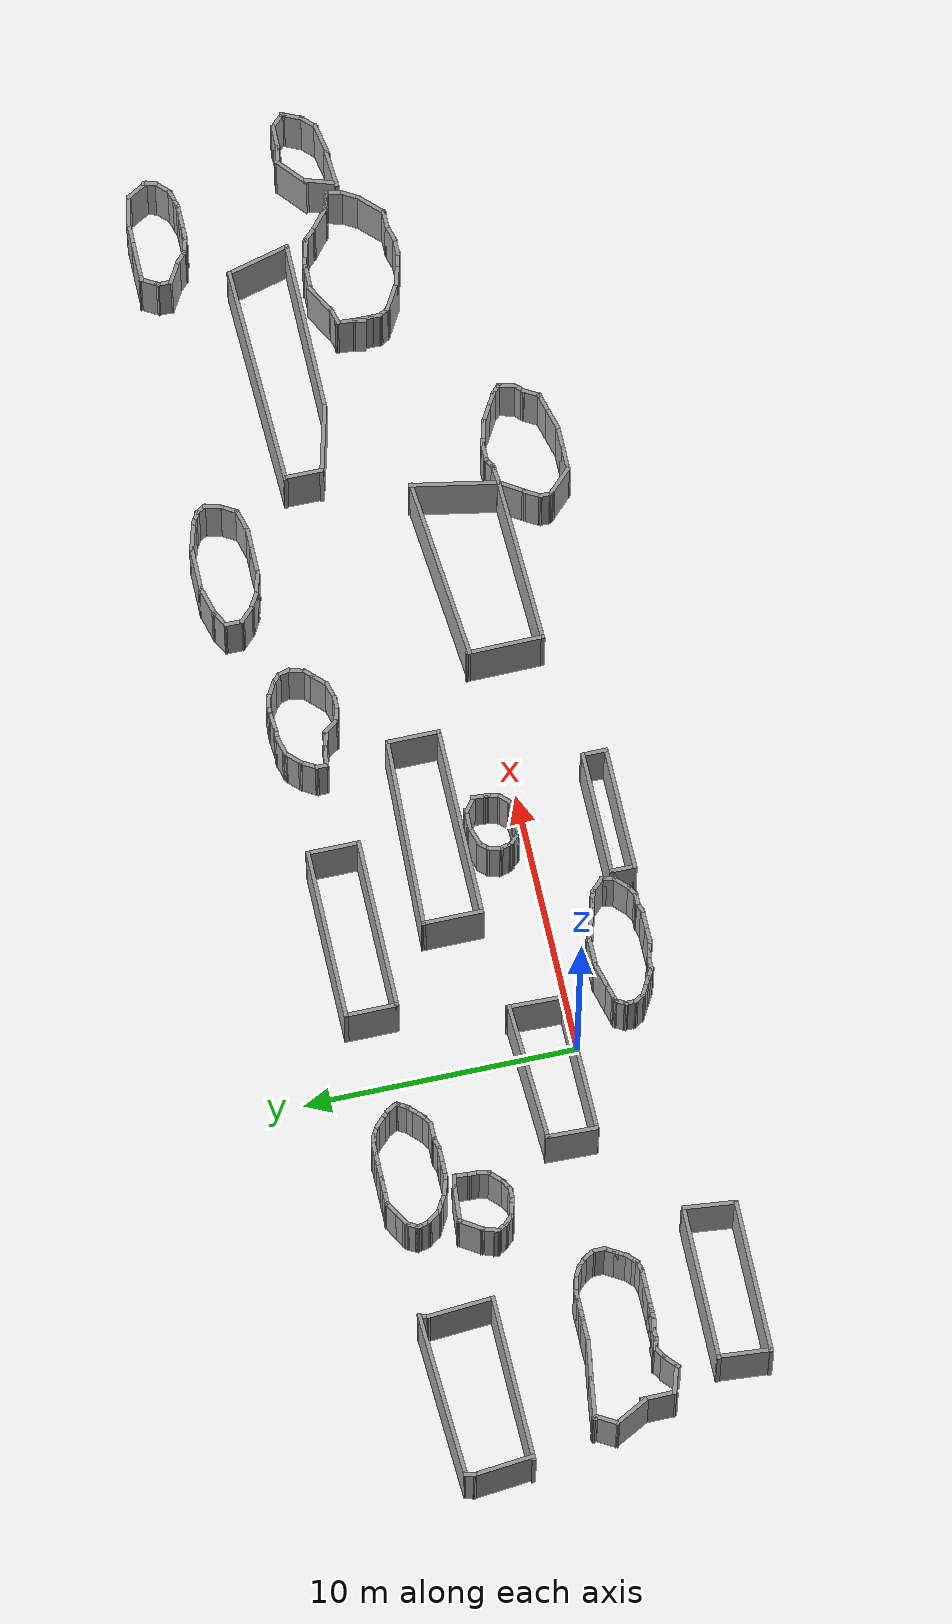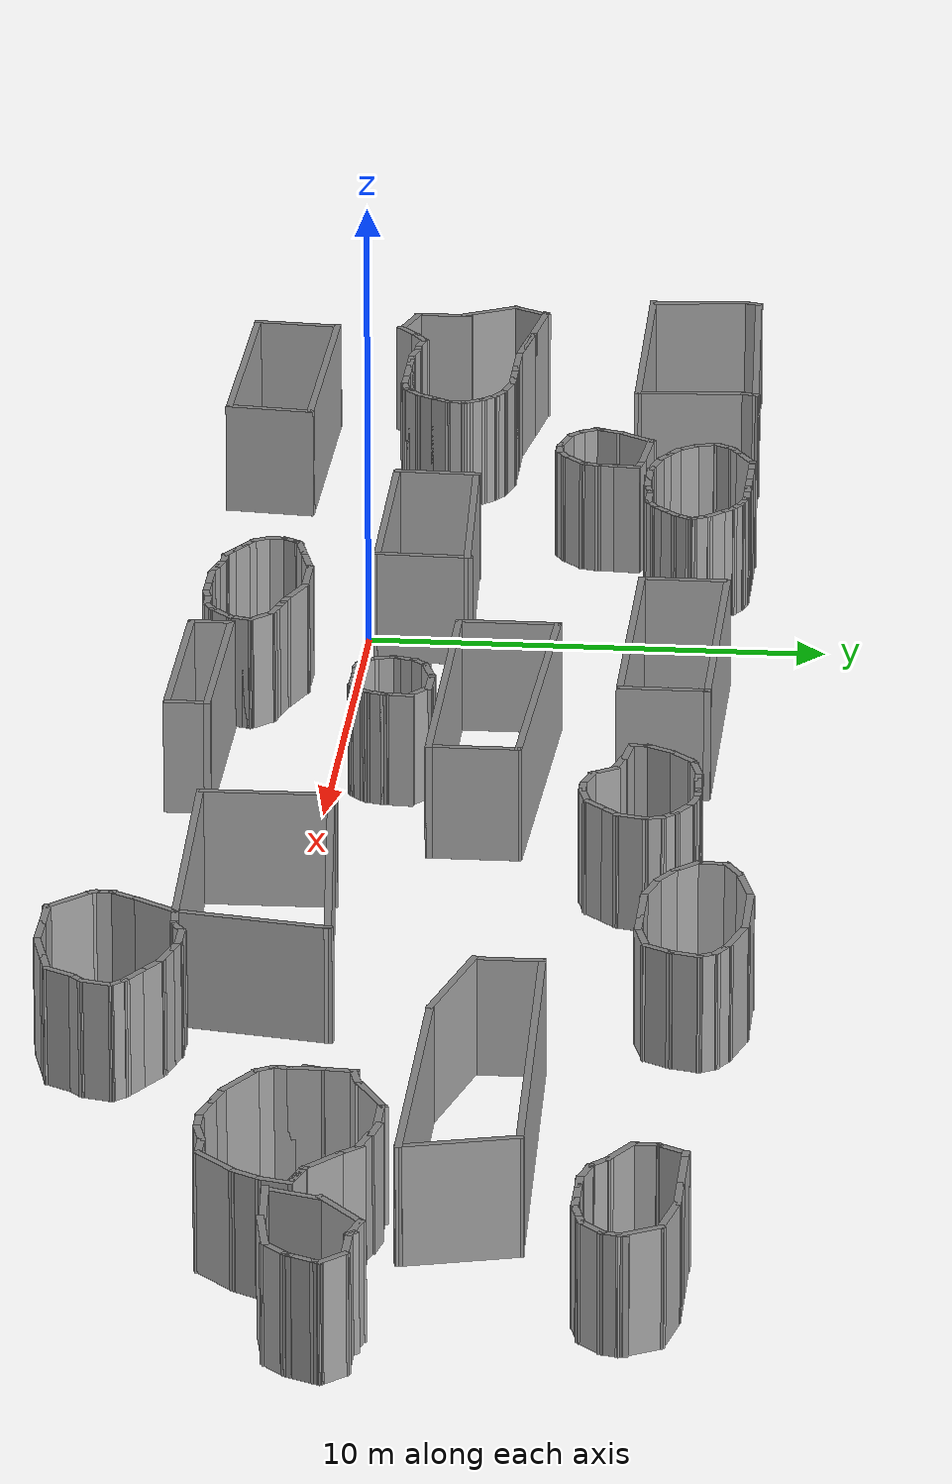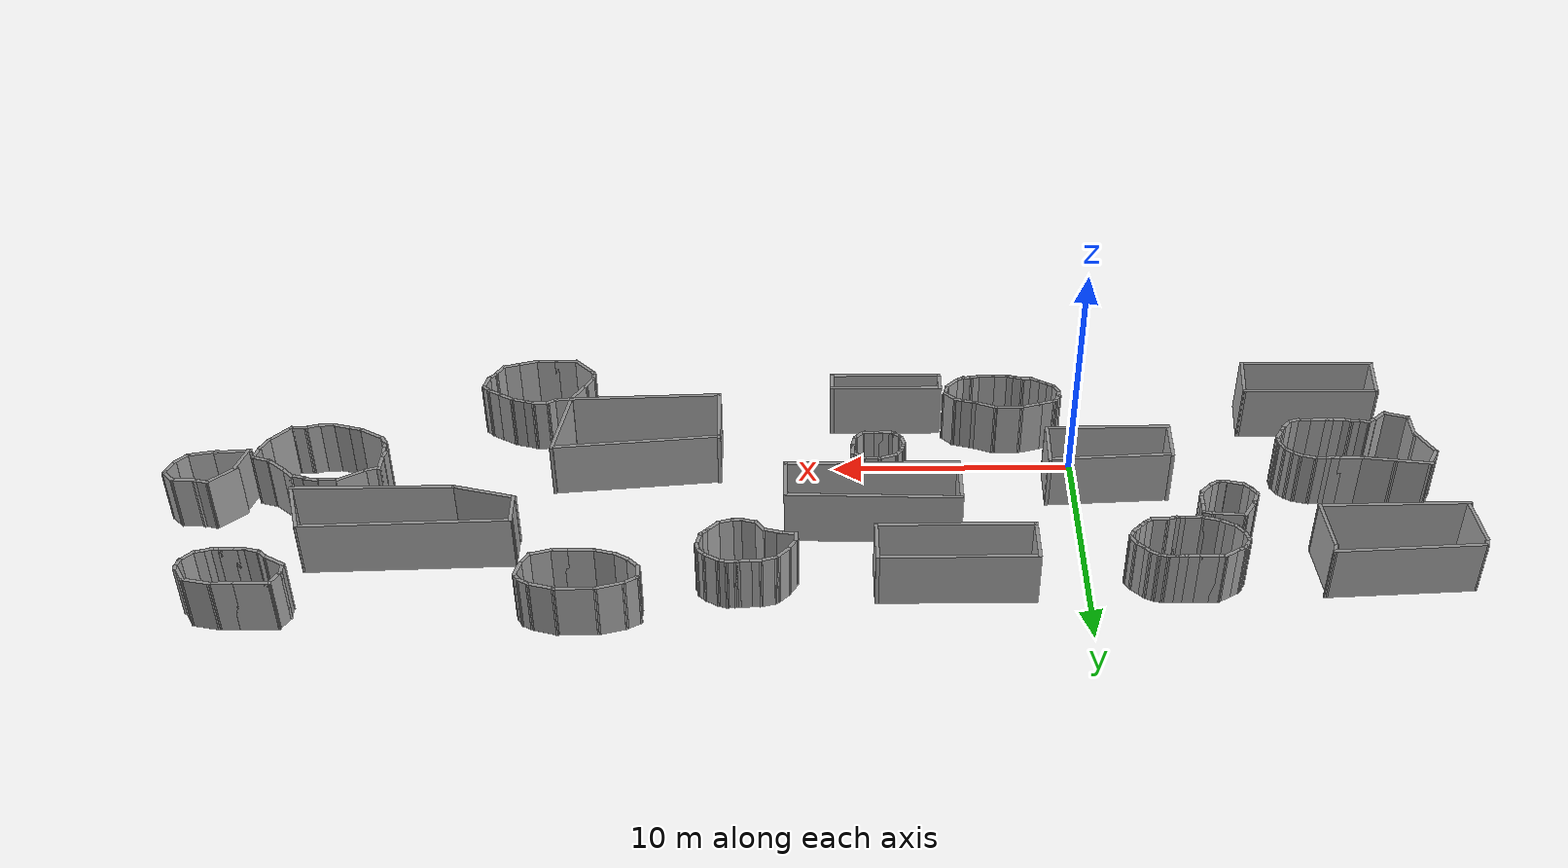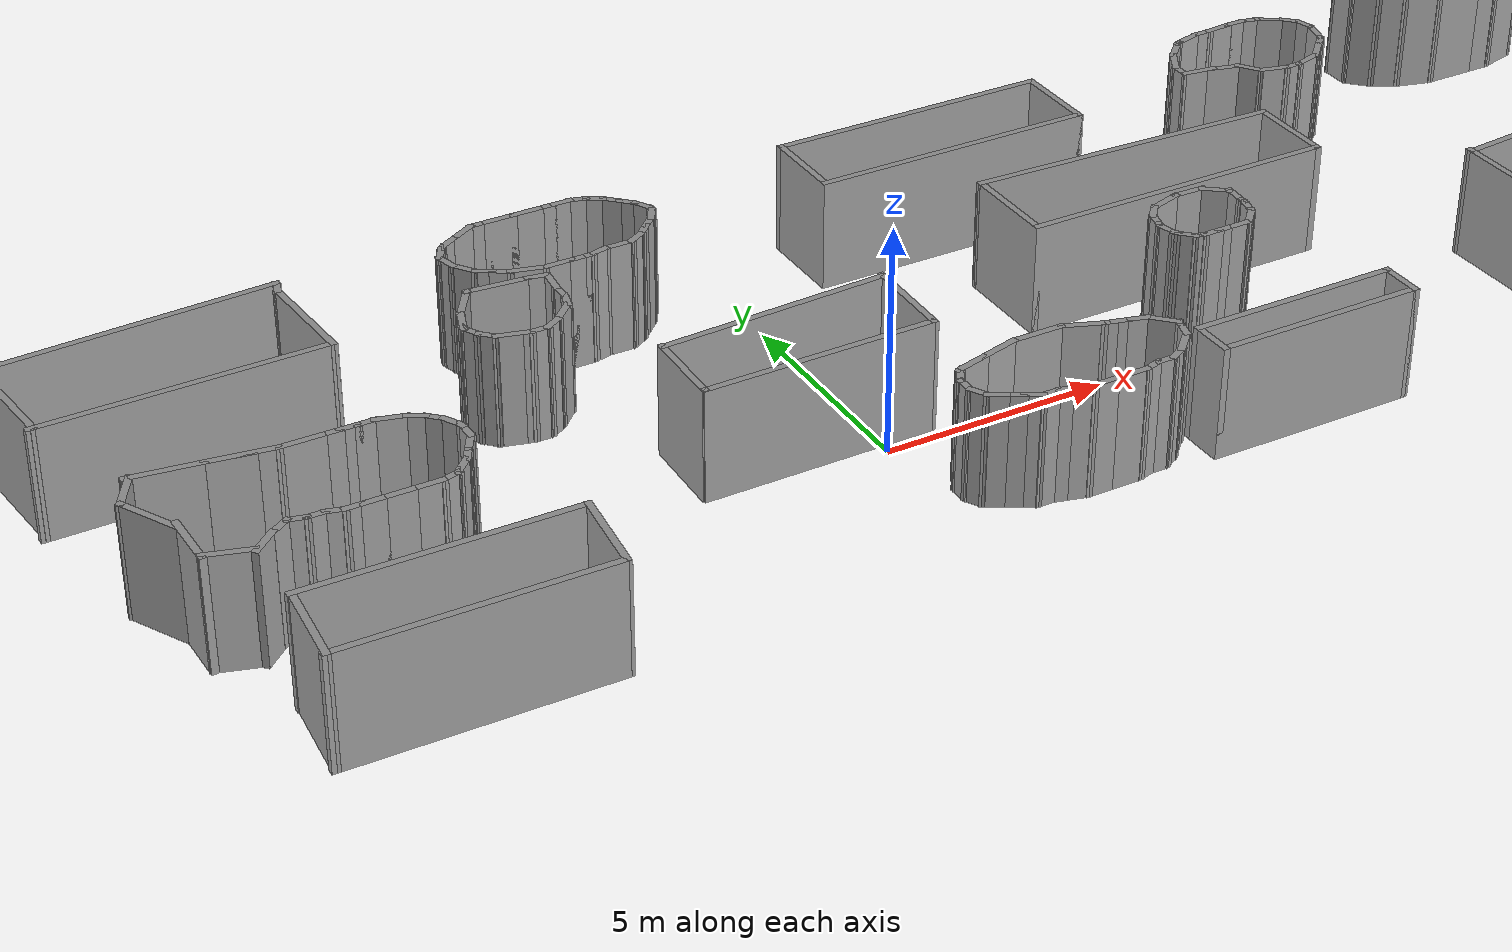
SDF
<?xml version='1.0'?>
<sdf version='1.7'>
  <model name='complex'>
    <pose>10.9367 2.58093 0 0 -0 0</pose>
    <link name='Wall_100'>
      <collision name='Wall_100_Collision'>
        <geometry>
          <box>
            <size>0.5 0.15 2.5</size>
          </box>
        </geometry>
        <pose>0 0 1.25 0 -0 0</pose>
      </collision>
      <visual name='Wall_100_Visual'>
        <pose>0 0 1.25 0 -0 0</pose>
        <geometry>
          <box>
            <size>0.5 0.15 2.5</size>
          </box>
        </geometry>
        <material>
          <script>
            <uri>file://media/materials/scripts/gazebo.material</uri>
            <name>Gazebo/Grey</name>
          </script>
          <ambient>1 1 1 1</ambient>
        </material>
        <meta>
          <layer>0</layer>
        </meta>
      </visual>
      <pose>-19.4502 -0.997037 0 0 -0 2.0944</pose>
    </link>
    <link name='Wall_101'>
      <collision name='Wall_101_Collision'>
        <geometry>
          <box>
            <size>0.5 0.15 2.5</size>
          </box>
        </geometry>
        <pose>0 0 1.25 0 -0 0</pose>
      </collision>
      <visual name='Wall_101_Visual'>
        <pose>0 0 1.25 0 -0 0</pose>
        <geometry>
          <box>
            <size>0.5 0.15 2.5</size>
          </box>
        </geometry>
        <material>
          <script>
            <uri>file://media/materials/scripts/gazebo.material</uri>
            <name>Gazebo/Grey</name>
          </script>
          <ambient>1 1 1 1</ambient>
        </material>
        <meta>
          <layer>0</layer>
        </meta>
      </visual>
      <pose>-19.6614 -0.721739 0 0 -0 2.35619</pose>
    </link>
    <link name='Wall_102'>
      <collision name='Wall_102_Collision'>
        <geometry>
          <box>
            <size>0.5 0.15 2.5</size>
          </box>
        </geometry>
        <pose>0 0 1.25 0 -0 0</pose>
      </collision>
      <visual name='Wall_102_Visual'>
        <pose>0 0 1.25 0 -0 0</pose>
        <geometry>
          <box>
            <size>0.5 0.15 2.5</size>
          </box>
        </geometry>
        <material>
          <script>
            <uri>file://media/materials/scripts/gazebo.material</uri>
            <name>Gazebo/Grey</name>
          </script>
          <ambient>1 1 1 1</ambient>
        </material>
        <meta>
          <layer>0</layer>
        </meta>
      </visual>
      <pose>-19.9367 -0.510496 0 0 -0 2.61799</pose>
    </link>
    <link name='Wall_103'>
      <collision name='Wall_103_Collision'>
        <geometry>
          <box>
            <size>0.75 0.15 2.5</size>
          </box>
        </geometry>
        <pose>0 0 1.25 0 -0 0</pose>
      </collision>
      <visual name='Wall_103_Visual'>
        <pose>0 0 1.25 0 -0 0</pose>
        <geometry>
          <box>
            <size>0.75 0.15 2.5</size>
          </box>
        </geometry>
        <material>
          <script>
            <uri>file://media/materials/scripts/gazebo.material</uri>
            <name>Gazebo/Grey</name>
          </script>
          <ambient>1 1 1 1</ambient>
        </material>
        <meta>
          <layer>0</layer>
        </meta>
      </visual>
      <pose>-20.3781 -0.34535 0 0 -0 2.87979</pose>
    </link>
    <link name='Wall_104'>
      <collision name='Wall_104_Collision'>
        <geometry>
          <box>
            <size>0.5 0.15 2.5</size>
          </box>
        </geometry>
        <pose>0 0 1.25 0 -0 0</pose>
      </collision>
      <visual name='Wall_104_Visual'>
        <pose>0 0 1.25 0 -0 0</pose>
        <geometry>
          <box>
            <size>0.5 0.15 2.5</size>
          </box>
        </geometry>
        <material>
          <script>
            <uri>file://media/materials/scripts/gazebo.material</uri>
            <name>Gazebo/Grey</name>
          </script>
          <ambient>1 1 1 1</ambient>
        </material>
        <meta>
          <layer>0</layer>
        </meta>
      </visual>
      <pose>-20.8428 -0.267704 0 0 -0 3.14159</pose>
    </link>
    <link name='Wall_105'>
      <collision name='Wall_105_Collision'>
        <geometry>
          <box>
            <size>0.5 0.15 2.5</size>
          </box>
        </geometry>
        <pose>0 0 1.25 0 -0 0</pose>
      </collision>
      <visual name='Wall_105_Visual'>
        <pose>0 0 1.25 0 -0 0</pose>
        <geometry>
          <box>
            <size>0.5 0.15 2.5</size>
          </box>
        </geometry>
        <material>
          <script>
            <uri>file://media/materials/scripts/gazebo.material</uri>
            <name>Gazebo/Grey</name>
          </script>
          <ambient>1 1 1 1</ambient>
        </material>
        <meta>
          <layer>0</layer>
        </meta>
      </visual>
      <pose>-21.1928 -0.267704 0 0 -0 3.14159</pose>
    </link>
    <link name='Wall_106'>
      <collision name='Wall_106_Collision'>
        <geometry>
          <box>
            <size>0.5 0.15 2.5</size>
          </box>
        </geometry>
        <pose>0 0 1.25 0 -0 0</pose>
      </collision>
      <visual name='Wall_106_Visual'>
        <pose>0 0 1.25 0 -0 0</pose>
        <geometry>
          <box>
            <size>0.5 0.15 2.5</size>
          </box>
        </geometry>
        <material>
          <script>
            <uri>file://media/materials/scripts/gazebo.material</uri>
            <name>Gazebo/Grey</name>
          </script>
          <ambient>1 1 1 1</ambient>
        </material>
        <meta>
          <layer>0</layer>
        </meta>
      </visual>
      <pose>-21.5428 -0.267704 0 0 -0 3.14159</pose>
    </link>
    <link name='Wall_107'>
      <collision name='Wall_107_Collision'>
        <geometry>
          <box>
            <size>1 0.15 2.5</size>
          </box>
        </geometry>
        <pose>0 0 1.25 0 -0 0</pose>
      </collision>
      <visual name='Wall_107_Visual'>
        <pose>0 0 1.25 0 -0 0</pose>
        <geometry>
          <box>
            <size>1 0.15 2.5</size>
          </box>
        </geometry>
        <material>
          <script>
            <uri>file://media/materials/scripts/gazebo.material</uri>
            <name>Gazebo/Grey</name>
          </script>
          <ambient>1 1 1 1</ambient>
        </material>
        <meta>
          <layer>0</layer>
        </meta>
      </visual>
      <pose>-22.1428 -0.267704 0 0 -0 3.14159</pose>
    </link>
    <link name='Wall_111'>
      <collision name='Wall_111_Collision'>
        <geometry>
          <box>
            <size>1.61529 0.15 2.5</size>
          </box>
        </geometry>
        <pose>0 0 1.25 0 -0 0</pose>
      </collision>
      <visual name='Wall_111_Visual'>
        <pose>0 0 1.25 0 -0 0</pose>
        <geometry>
          <box>
            <size>1.61529 0.15 2.5</size>
          </box>
        </geometry>
        <material>
          <script>
            <uri>file://media/materials/scripts/gazebo.material</uri>
            <name>Gazebo/Grey</name>
          </script>
          <ambient>1 1 1 1</ambient>
        </material>
        <meta>
          <layer>0</layer>
        </meta>
      </visual>
      <pose>-24.648 0.027926 0 0 -0 3.00766</pose>
    </link>
    <link name='Wall_112'>
      <collision name='Wall_112_Collision'>
        <geometry>
          <box>
            <size>0.15 0.15 2.5</size>
          </box>
        </geometry>
        <pose>0 0 1.25 0 -0 0</pose>
      </collision>
      <visual name='Wall_112_Visual'>
        <pose>0 0 1.25 0 -0 0</pose>
        <geometry>
          <box>
            <size>0.15 0.15 2.5</size>
          </box>
        </geometry>
        <material>
          <script>
            <uri>file://media/materials/scripts/gazebo.material</uri>
            <name>Gazebo/Grey</name>
          </script>
          <ambient>1 1 1 1</ambient>
        </material>
        <meta>
          <layer>0</layer>
        </meta>
      </visual>
      <pose>-25.3741 0.125759 0 0 -0 0</pose>
    </link>
    <link name='Wall_113'>
      <collision name='Wall_113_Collision'>
        <geometry>
          <box>
            <size>1 0.15 2.5</size>
          </box>
        </geometry>
        <pose>0 0 1.25 0 -0 0</pose>
      </collision>
      <visual name='Wall_113_Visual'>
        <pose>0 0 1.25 0 -0 0</pose>
        <geometry>
          <box>
            <size>1 0.15 2.5</size>
          </box>
        </geometry>
        <material>
          <script>
            <uri>file://media/materials/scripts/gazebo.material</uri>
            <name>Gazebo/Grey</name>
          </script>
          <ambient>1 1 1 1</ambient>
        </material>
        <meta>
          <layer>0</layer>
        </meta>
      </visual>
      <pose>-25.494 -0.242301 0 0 -0 -2.0944</pose>
    </link>
    <link name='Wall_114'>
      <collision name='Wall_114_Collision'>
        <geometry>
          <box>
            <size>1.44528 0.15 2.5</size>
          </box>
        </geometry>
        <pose>0 0 1.25 0 -0 0</pose>
      </collision>
      <visual name='Wall_114_Visual'>
        <pose>0 0 1.25 0 -0 0</pose>
        <geometry>
          <box>
            <size>1.44528 0.15 2.5</size>
          </box>
        </geometry>
        <material>
          <script>
            <uri>file://media/materials/scripts/gazebo.material</uri>
            <name>Gazebo/Grey</name>
          </script>
          <ambient>1 1 1 1</ambient>
        </material>
        <meta>
          <layer>0</layer>
        </meta>
      </visual>
      <pose>-25.3992 -1.18047 0 0 -0 -1.07646</pose>
    </link>
    <link name='Wall_117'>
      <collision name='Wall_117_Collision'>
        <geometry>
          <box>
            <size>1.34808 0.15 2.5</size>
          </box>
        </geometry>
        <pose>0 0 1.25 0 -0 0</pose>
      </collision>
      <visual name='Wall_117_Visual'>
        <pose>0 0 1.25 0 -0 0</pose>
        <geometry>
          <box>
            <size>1.34808 0.15 2.5</size>
          </box>
        </geometry>
        <material>
          <script>
            <uri>file://media/materials/scripts/gazebo.material</uri>
            <name>Gazebo/Grey</name>
          </script>
          <ambient>1 1 1 1</ambient>
        </material>
        <meta>
          <layer>0</layer>
        </meta>
      </visual>
      <pose>-25.0456 -2.23835 0 0 -0 -1.55537</pose>
    </link>
    <link name='Wall_118'>
      <collision name='Wall_118_Collision'>
        <geometry>
          <box>
            <size>1.09701 0.15 2.5</size>
          </box>
        </geometry>
        <pose>0 0 1.25 0 -0 0</pose>
      </collision>
      <visual name='Wall_118_Visual'>
        <pose>0 0 1.25 0 -0 0</pose>
        <geometry>
          <box>
            <size>1.09701 0.15 2.5</size>
          </box>
        </geometry>
        <material>
          <script>
            <uri>file://media/materials/scripts/gazebo.material</uri>
            <name>Gazebo/Grey</name>
          </script>
          <ambient>1 1 1 1</ambient>
        </material>
        <meta>
          <layer>0</layer>
        </meta>
      </visual>
      <pose>-24.5837 -2.93929 0 0 -0 -0.298026</pose>
    </link>
    <link name='Wall_120'>
      <collision name='Wall_120_Collision'>
        <geometry>
          <box>
            <size>1.91735 0.15 2.5</size>
          </box>
        </geometry>
        <pose>0 0 1.25 0 -0 0</pose>
      </collision>
      <visual name='Wall_120_Visual'>
        <pose>0 0 1.25 0 -0 0</pose>
        <geometry>
          <box>
            <size>1.91735 0.15 2.5</size>
          </box>
        </geometry>
        <material>
          <script>
            <uri>file://media/materials/scripts/gazebo.material</uri>
            <name>Gazebo/Grey</name>
          </script>
          <ambient>1 1 1 1</ambient>
        </material>
        <meta>
          <layer>0</layer>
        </meta>
      </visual>
      <pose>-14.8464 -1.43335 0 0 -0 -1.59854</pose>
    </link>
    <link name='Wall_121'>
      <collision name='Wall_121_Collision'>
        <geometry>
          <box>
            <size>5.20588 0.15 2.5</size>
          </box>
        </geometry>
        <pose>0 0 1.25 0 -0 0</pose>
      </collision>
      <visual name='Wall_121_Visual'>
        <pose>0 0 1.25 0 -0 0</pose>
        <geometry>
          <box>
            <size>5.20588 0.15 2.5</size>
          </box>
        </geometry>
        <material>
          <script>
            <uri>file://media/materials/scripts/gazebo.material</uri>
            <name>Gazebo/Grey</name>
          </script>
          <ambient>1 1 1 1</ambient>
        </material>
        <meta>
          <layer>0</layer>
        </meta>
      </visual>
      <pose>-12.3184 -2.31669 0 0 -0 0.009695</pose>
    </link>
    <link name='Wall_122'>
      <collision name='Wall_122_Collision'>
        <geometry>
          <box>
            <size>2.16727 0.15 2.5</size>
          </box>
        </geometry>
        <pose>0 0 1.25 0 -0 0</pose>
      </collision>
      <visual name='Wall_122_Visual'>
        <pose>0 0 1.25 0 -0 0</pose>
        <geometry>
          <box>
            <size>2.16727 0.15 2.5</size>
          </box>
        </geometry>
        <material>
          <script>
            <uri>file://media/materials/scripts/gazebo.material</uri>
            <name>Gazebo/Grey</name>
          </script>
          <ambient>1 1 1 1</ambient>
        </material>
        <meta>
          <layer>0</layer>
        </meta>
      </visual>
      <pose>-9.76599 -1.28384 0 0 -0 1.54649</pose>
    </link>
    <link name='Wall_123'>
      <collision name='Wall_123_Collision'>
        <geometry>
          <box>
            <size>5.21205 0.15 2.5</size>
          </box>
        </geometry>
        <pose>0 0 1.25 0 -0 0</pose>
      </collision>
      <visual name='Wall_123_Visual'>
        <pose>0 0 1.25 0 -0 0</pose>
        <geometry>
          <box>
            <size>5.21205 0.15 2.5</size>
          </box>
        </geometry>
        <material>
          <script>
            <uri>file://media/materials/scripts/gazebo.material</uri>
            <name>Gazebo/Grey</name>
          </script>
          <ambient>1 1 1 1</ambient>
        </material>
        <meta>
          <layer>0</layer>
        </meta>
      </visual>
      <pose>-12.2694 -0.449524 0 0 -0 -3.09219</pose>
    </link>
    <link name='Wall_129'>
      <collision name='Wall_129_Collision'>
        <geometry>
          <box>
            <size>0.25 0.15 2.5</size>
          </box>
        </geometry>
        <pose>0 0 1.25 0 -0 0</pose>
      </collision>
      <visual name='Wall_129_Visual'>
        <pose>0 0 1.25 0 -0 0</pose>
        <geometry>
          <box>
            <size>0.25 0.15 2.5</size>
          </box>
        </geometry>
        <material>
          <script>
            <uri>file://media/materials/scripts/gazebo.material</uri>
            <name>Gazebo/Grey</name>
          </script>
          <ambient>1 1 1 1</ambient>
        </material>
        <meta>
          <layer>0</layer>
        </meta>
      </visual>
      <pose>-17.868 1.93115 0 0 -0 -1.5708</pose>
    </link>
    <link name='Wall_130'>
      <collision name='Wall_130_Collision'>
        <geometry>
          <box>
            <size>0.5 0.15 2.5</size>
          </box>
        </geometry>
        <pose>0 0 1.25 0 -0 0</pose>
      </collision>
      <visual name='Wall_130_Visual'>
        <pose>0 0 1.25 0 -0 0</pose>
        <geometry>
          <box>
            <size>0.5 0.15 2.5</size>
          </box>
        </geometry>
        <material>
          <script>
            <uri>file://media/materials/scripts/gazebo.material</uri>
            <name>Gazebo/Grey</name>
          </script>
          <ambient>1 1 1 1</ambient>
        </material>
        <meta>
          <layer>0</layer>
        </meta>
      </visual>
      <pose>-17.7805 1.72959 0 0 -0 -1.0472</pose>
    </link>
    <link name='Wall_131'>
      <collision name='Wall_131_Collision'>
        <geometry>
          <box>
            <size>0.5 0.15 2.5</size>
          </box>
        </geometry>
        <pose>0 0 1.25 0 -0 0</pose>
      </collision>
      <visual name='Wall_131_Visual'>
        <pose>0 0 1.25 0 -0 0</pose>
        <geometry>
          <box>
            <size>0.5 0.15 2.5</size>
          </box>
        </geometry>
        <material>
          <script>
            <uri>file://media/materials/scripts/gazebo.material</uri>
            <name>Gazebo/Grey</name>
          </script>
          <ambient>1 1 1 1</ambient>
        </material>
        <meta>
          <layer>0</layer>
        </meta>
      </visual>
      <pose>-17.5693 1.45429 0 0 -0 -0.785398</pose>
    </link>
    <link name='Wall_132'>
      <collision name='Wall_132_Collision'>
        <geometry>
          <box>
            <size>0.75 0.15 2.5</size>
          </box>
        </geometry>
        <pose>0 0 1.25 0 -0 0</pose>
      </collision>
      <visual name='Wall_132_Visual'>
        <pose>0 0 1.25 0 -0 0</pose>
        <geometry>
          <box>
            <size>0.75 0.15 2.5</size>
          </box>
        </geometry>
        <material>
          <script>
            <uri>file://media/materials/scripts/gazebo.material</uri>
            <name>Gazebo/Grey</name>
          </script>
          <ambient>1 1 1 1</ambient>
        </material>
        <meta>
          <layer>0</layer>
        </meta>
      </visual>
      <pose>-17.1557 1.2529 0 0 -0 -0.261799</pose>
    </link>
    <link name='Wall_133'>
      <collision name='Wall_133_Collision'>
        <geometry>
          <box>
            <size>0.25 0.15 2.5</size>
          </box>
        </geometry>
        <pose>0 0 1.25 0 -0 0</pose>
      </collision>
      <visual name='Wall_133_Visual'>
        <pose>0 0 1.25 0 -0 0</pose>
        <geometry>
          <box>
            <size>0.25 0.15 2.5</size>
          </box>
        </geometry>
        <material>
          <script>
            <uri>file://media/materials/scripts/gazebo.material</uri>
            <name>Gazebo/Grey</name>
          </script>
          <ambient>1 1 1 1</ambient>
        </material>
        <meta>
          <layer>0</layer>
        </meta>
      </visual>
      <pose>-16.8177 1.16232 0 0 -0 -0.261799</pose>
    </link>
    <link name='Wall_134'>
      <collision name='Wall_134_Collision'>
        <geometry>
          <box>
            <size>0.5 0.15 2.5</size>
          </box>
        </geometry>
        <pose>0 0 1.25 0 -0 0</pose>
      </collision>
      <visual name='Wall_134_Visual'>
        <pose>0 0 1.25 0 -0 0</pose>
        <geometry>
          <box>
            <size>0.5 0.15 2.5</size>
          </box>
        </geometry>
        <material>
          <script>
            <uri>file://media/materials/scripts/gazebo.material</uri>
            <name>Gazebo/Grey</name>
          </script>
          <ambient>1 1 1 1</ambient>
        </material>
        <meta>
          <layer>0</layer>
        </meta>
      </visual>
      <pose>-16.5944 1.14938 0 0 -0 0</pose>
    </link>
    <link name='Wall_135'>
      <collision name='Wall_135_Collision'>
        <geometry>
          <box>
            <size>0.5 0.15 2.5</size>
          </box>
        </geometry>
        <pose>0 0 1.25 0 -0 0</pose>
      </collision>
      <visual name='Wall_135_Visual'>
        <pose>0 0 1.25 0 -0 0</pose>
        <geometry>
          <box>
            <size>0.5 0.15 2.5</size>
          </box>
        </geometry>
        <material>
          <script>
            <uri>file://media/materials/scripts/gazebo.material</uri>
            <name>Gazebo/Grey</name>
          </script>
          <ambient>1 1 1 1</ambient>
        </material>
        <meta>
          <layer>0</layer>
        </meta>
      </visual>
      <pose>-16.2678 1.23688 0 0 -0 0.523599</pose>
    </link>
    <link name='Wall_136'>
      <collision name='Wall_136_Collision'>
        <geometry>
          <box>
            <size>0.75 0.15 2.5</size>
          </box>
        </geometry>
        <pose>0 0 1.25 0 -0 0</pose>
      </collision>
      <visual name='Wall_136_Visual'>
        <pose>0 0 1.25 0 -0 0</pose>
        <geometry>
          <box>
            <size>0.75 0.15 2.5</size>
          </box>
        </geometry>
        <material>
          <script>
            <uri>file://media/materials/scripts/gazebo.material</uri>
            <name>Gazebo/Grey</name>
          </script>
          <ambient>1 1 1 1</ambient>
        </material>
        <meta>
          <layer>0</layer>
        </meta>
      </visual>
      <pose>-15.9041 1.53651 0 0 -0 0.785398</pose>
    </link>
    <link name='Wall_137'>
      <collision name='Wall_137_Collision'>
        <geometry>
          <box>
            <size>0.5 0.15 2.5</size>
          </box>
        </geometry>
        <pose>0 0 1.25 0 -0 0</pose>
      </collision>
      <visual name='Wall_137_Visual'>
        <pose>0 0 1.25 0 -0 0</pose>
        <geometry>
          <box>
            <size>0.5 0.15 2.5</size>
          </box>
        </geometry>
        <material>
          <script>
            <uri>file://media/materials/scripts/gazebo.material</uri>
            <name>Gazebo/Grey</name>
          </script>
          <ambient>1 1 1 1</ambient>
        </material>
        <meta>
          <layer>0</layer>
        </meta>
      </visual>
      <pose>-15.6467 1.91768 0 0 -0 1.309</pose>
    </link>
    <link name='Wall_138'>
      <collision name='Wall_138_Collision'>
        <geometry>
          <box>
            <size>0.5 0.15 2.5</size>
          </box>
        </geometry>
        <pose>0 0 1.25 0 -0 0</pose>
      </collision>
      <visual name='Wall_138_Visual'>
        <pose>0 0 1.25 0 -0 0</pose>
        <geometry>
          <box>
            <size>0.5 0.15 2.5</size>
          </box>
        </geometry>
        <material>
          <script>
            <uri>file://media/materials/scripts/gazebo.material</uri>
            <name>Gazebo/Grey</name>
          </script>
          <ambient>1 1 1 1</ambient>
        </material>
        <meta>
          <layer>0</layer>
        </meta>
      </visual>
      <pose>-15.6014 2.26172 0 0 -0 1.5708</pose>
    </link>
    <link name='Wall_139'>
      <collision name='Wall_139_Collision'>
        <geometry>
          <box>
            <size>0.661181 0.15 2.5</size>
          </box>
        </geometry>
        <pose>0 0 1.25 0 -0 0</pose>
      </collision>
      <visual name='Wall_139_Visual'>
        <pose>0 0 1.25 0 -0 0</pose>
        <geometry>
          <box>
            <size>0.661181 0.15 2.5</size>
          </box>
        </geometry>
        <material>
          <script>
            <uri>file://media/materials/scripts/gazebo.material</uri>
            <name>Gazebo/Grey</name>
          </script>
          <ambient>1 1 1 1</ambient>
        </material>
        <meta>
          <layer>0</layer>
        </meta>
      </visual>
      <pose>-15.5756 2.69101 0 0 -0 1.46988</pose>
    </link>
    <link name='Wall_140'>
      <collision name='Wall_140_Collision'>
        <geometry>
          <box>
            <size>0.521727 0.15 2.5</size>
          </box>
        </geometry>
        <pose>0 0 1.25 0 -0 0</pose>
      </collision>
      <visual name='Wall_140_Visual'>
        <pose>0 0 1.25 0 -0 0</pose>
        <geometry>
          <box>
            <size>0.521727 0.15 2.5</size>
          </box>
        </geometry>
        <material>
          <script>
            <uri>file://media/materials/scripts/gazebo.material</uri>
            <name>Gazebo/Grey</name>
          </script>
          <ambient>1 1 1 1</ambient>
        </material>
        <meta>
          <layer>0</layer>
        </meta>
      </visual>
      <pose>-15.7616 3.0048 0 0 -0 2.97356</pose>
    </link>
    <link name='Wall_144'>
      <collision name='Wall_144_Collision'>
        <geometry>
          <box>
            <size>0.15 0.15 2.5</size>
          </box>
        </geometry>
        <pose>0 0 1.25 0 -0 0</pose>
      </collision>
      <visual name='Wall_144_Visual'>
        <pose>0 0 1.25 0 -0 0</pose>
        <geometry>
          <box>
            <size>0.15 0.15 2.5</size>
          </box>
        </geometry>
        <material>
          <script>
            <uri>file://media/materials/scripts/gazebo.material</uri>
            <name>Gazebo/Grey</name>
          </script>
          <ambient>1 1 1 1</ambient>
        </material>
        <meta>
          <layer>0</layer>
        </meta>
      </visual>
      <pose>-17.223 3.14443 0 0 -0 0</pose>
    </link>
    <link name='Wall_148'>
      <collision name='Wall_148_Collision'>
        <geometry>
          <box>
            <size>2.29146 0.15 2.5</size>
          </box>
        </geometry>
        <pose>0 0 1.25 0 -0 0</pose>
      </collision>
      <visual name='Wall_148_Visual'>
        <pose>0 0 1.25 0 -0 0</pose>
        <geometry>
          <box>
            <size>2.29146 0.15 2.5</size>
          </box>
        </geometry>
        <material>
          <script>
            <uri>file://media/materials/scripts/gazebo.material</uri>
            <name>Gazebo/Grey</name>
          </script>
          <ambient>1 1 1 1</ambient>
        </material>
        <meta>
          <layer>0</layer>
        </meta>
      </visual>
      <pose>-26.3683 3.60126 0 0 -0 -1.46971</pose>
    </link>
    <link name='Wall_149'>
      <collision name='Wall_149_Collision'>
        <geometry>
          <box>
            <size>6.21671 0.15 2.5</size>
          </box>
        </geometry>
        <pose>0 0 1.25 0 -0 0</pose>
      </collision>
      <visual name='Wall_149_Visual'>
        <pose>0 0 1.25 0 -0 0</pose>
        <geometry>
          <box>
            <size>6.21671 0.15 2.5</size>
          </box>
        </geometry>
        <material>
          <script>
            <uri>file://media/materials/scripts/gazebo.material</uri>
            <name>Gazebo/Grey</name>
          </script>
          <ambient>1 1 1 1</ambient>
        </material>
        <meta>
          <layer>0</layer>
        </meta>
      </visual>
      <pose>-23.3136 2.57922 0 0 -0 0.014249</pose>
    </link>
    <link name='Wall_150'>
      <collision name='Wall_150_Collision'>
        <geometry>
          <box>
            <size>2.51228 0.15 2.5</size>
          </box>
        </geometry>
        <pose>0 0 1.25 0 -0 0</pose>
      </collision>
      <visual name='Wall_150_Visual'>
        <pose>0 0 1.25 0 -0 0</pose>
        <geometry>
          <box>
            <size>2.51228 0.15 2.5</size>
          </box>
        </geometry>
        <material>
          <script>
            <uri>file://media/materials/scripts/gazebo.material</uri>
            <name>Gazebo/Grey</name>
          </script>
          <ambient>1 1 1 1</ambient>
        </material>
        <meta>
          <layer>0</layer>
        </meta>
      </visual>
      <pose>-20.367 3.80041 0 0 -0 1.64404</pose>
    </link>
    <link name='Wall_151'>
      <collision name='Wall_151_Collision'>
        <geometry>
          <box>
            <size>6.18095 0.15 2.5</size>
          </box>
        </geometry>
        <pose>0 0 1.25 0 -0 0</pose>
      </collision>
      <visual name='Wall_151_Visual'>
        <pose>0 0 1.25 0 -0 0</pose>
        <geometry>
          <box>
            <size>6.18095 0.15 2.5</size>
          </box>
        </geometry>
        <material>
          <script>
            <uri>file://media/materials/scripts/gazebo.material</uri>
            <name>Gazebo/Grey</name>
          </script>
          <ambient>1 1 1 1</ambient>
        </material>
        <meta>
          <layer>0</layer>
        </meta>
      </visual>
      <pose>-23.3784 5.12499 0 0 -0 -3.08986</pose>
    </link>
    <link name='Wall_153'>
      <collision name='Wall_153_Collision'>
        <geometry>
          <box>
            <size>0.5 0.15 2.5</size>
          </box>
        </geometry>
        <pose>0 0 1.25 0 -0 0</pose>
      </collision>
      <visual name='Wall_153_Visual'>
        <pose>0 0 1.25 0 -0 0</pose>
        <geometry>
          <box>
            <size>0.5 0.15 2.5</size>
          </box>
        </geometry>
        <material>
          <script>
            <uri>file://media/materials/scripts/gazebo.material</uri>
            <name>Gazebo/Grey</name>
          </script>
          <ambient>1 1 1 1</ambient>
        </material>
        <meta>
          <layer>0</layer>
        </meta>
      </visual>
      <pose>-16.5787 3.70528 0 0 -0 -0.523599</pose>
    </link>
    <link name='Wall_154'>
      <collision name='Wall_154_Collision'>
        <geometry>
          <box>
            <size>0.5 0.15 2.5</size>
          </box>
        </geometry>
        <pose>0 0 1.25 0 -0 0</pose>
      </collision>
      <visual name='Wall_154_Visual'>
        <pose>0 0 1.25 0 -0 0</pose>
        <geometry>
          <box>
            <size>0.5 0.15 2.5</size>
          </box>
        </geometry>
        <material>
          <script>
            <uri>file://media/materials/scripts/gazebo.material</uri>
            <name>Gazebo/Grey</name>
          </script>
          <ambient>1 1 1 1</ambient>
        </material>
        <meta>
          <layer>0</layer>
        </meta>
      </visual>
      <pose>-16.2756 3.53028 0 0 -0 -0.523599</pose>
    </link>
    <link name='Wall_155'>
      <collision name='Wall_155_Collision'>
        <geometry>
          <box>
            <size>0.75 0.15 2.5</size>
          </box>
        </geometry>
        <pose>0 0 1.25 0 -0 0</pose>
      </collision>
      <visual name='Wall_155_Visual'>
        <pose>0 0 1.25 0 -0 0</pose>
        <geometry>
          <box>
            <size>0.75 0.15 2.5</size>
          </box>
        </geometry>
        <material>
          <script>
            <uri>file://media/materials/scripts/gazebo.material</uri>
            <name>Gazebo/Grey</name>
          </script>
          <ambient>1 1 1 1</ambient>
        </material>
        <meta>
          <layer>0</layer>
        </meta>
      </visual>
      <pose>-15.8343 3.36513 0 0 -0 -0.261799</pose>
    </link>
    <link name='Wall_156'>
      <collision name='Wall_156_Collision'>
        <geometry>
          <box>
            <size>0.25 0.15 2.5</size>
          </box>
        </geometry>
        <pose>0 0 1.25 0 -0 0</pose>
      </collision>
      <visual name='Wall_156_Visual'>
        <pose>0 0 1.25 0 -0 0</pose>
        <geometry>
          <box>
            <size>0.25 0.15 2.5</size>
          </box>
        </geometry>
        <material>
          <script>
            <uri>file://media/materials/scripts/gazebo.material</uri>
            <name>Gazebo/Grey</name>
          </script>
          <ambient>1 1 1 1</ambient>
        </material>
        <meta>
          <layer>0</layer>
        </meta>
      </visual>
      <pose>-15.4962 3.27454 0 0 -0 -0.261799</pose>
    </link>
    <link name='Wall_157'>
      <collision name='Wall_157_Collision'>
        <geometry>
          <box>
            <size>0.75 0.15 2.5</size>
          </box>
        </geometry>
        <pose>0 0 1.25 0 -0 0</pose>
      </collision>
      <visual name='Wall_157_Visual'>
        <pose>0 0 1.25 0 -0 0</pose>
        <geometry>
          <box>
            <size>0.75 0.15 2.5</size>
          </box>
        </geometry>
        <material>
          <script>
            <uri>file://media/materials/scripts/gazebo.material</uri>
            <name>Gazebo/Grey</name>
          </script>
          <ambient>1 1 1 1</ambient>
        </material>
        <meta>
          <layer>0</layer>
        </meta>
      </visual>
      <pose>-15.1479 3.2616 0 0 -0 0</pose>
    </link>
    <link name='Wall_158'>
      <collision name='Wall_158_Collision'>
        <geometry>
          <box>
            <size>0.5 0.15 2.5</size>
          </box>
        </geometry>
        <pose>0 0 1.25 0 -0 0</pose>
      </collision>
      <visual name='Wall_158_Visual'>
        <pose>0 0 1.25 0 -0 0</pose>
        <geometry>
          <box>
            <size>0.5 0.15 2.5</size>
          </box>
        </geometry>
        <material>
          <script>
            <uri>file://media/materials/scripts/gazebo.material</uri>
            <name>Gazebo/Grey</name>
          </script>
          <ambient>1 1 1 1</ambient>
        </material>
        <meta>
          <layer>0</layer>
        </meta>
      </visual>
      <pose>-14.6729 3.2616 0 0 -0 0</pose>
    </link>
    <link name='Wall_159'>
      <collision name='Wall_159_Collision'>
        <geometry>
          <box>
            <size>0.25 0.15 2.5</size>
          </box>
        </geometry>
        <pose>0 0 1.25 0 -0 0</pose>
      </collision>
      <visual name='Wall_159_Visual'>
        <pose>0 0 1.25 0 -0 0</pose>
        <geometry>
          <box>
            <size>0.25 0.15 2.5</size>
          </box>
        </geometry>
        <material>
          <script>
            <uri>file://media/materials/scripts/gazebo.material</uri>
            <name>Gazebo/Grey</name>
          </script>
          <ambient>1 1 1 1</ambient>
        </material>
        <meta>
          <layer>0</layer>
        </meta>
      </visual>
      <pose>-14.4479 3.2616 0 0 -0 0</pose>
    </link>
    <link name='Wall_160'>
      <collision name='Wall_160_Collision'>
        <geometry>
          <box>
            <size>0.5 0.15 2.5</size>
          </box>
        </geometry>
        <pose>0 0 1.25 0 -0 0</pose>
      </collision>
      <visual name='Wall_160_Visual'>
        <pose>0 0 1.25 0 -0 0</pose>
        <geometry>
          <box>
            <size>0.5 0.15 2.5</size>
          </box>
        </geometry>
        <material>
          <script>
            <uri>file://media/materials/scripts/gazebo.material</uri>
            <name>Gazebo/Grey</name>
          </script>
          <ambient>1 1 1 1</ambient>
        </material>
        <meta>
          <layer>0</layer>
        </meta>
      </visual>
      <pose>-14.2289 3.3069 0 0 -0 0.261799</pose>
    </link>
    <link name='Wall_161'>
      <collision name='Wall_161_Collision'>
        <geometry>
          <box>
            <size>0.15 0.15 2.5</size>
          </box>
        </geometry>
        <pose>0 0 1.25 0 -0 0</pose>
      </collision>
      <visual name='Wall_161_Visual'>
        <pose>0 0 1.25 0 -0 0</pose>
        <geometry>
          <box>
            <size>0.15 0.15 2.5</size>
          </box>
        </geometry>
        <material>
          <script>
            <uri>file://media/materials/scripts/gazebo.material</uri>
            <name>Gazebo/Grey</name>
          </script>
          <ambient>1 1 1 1</ambient>
        </material>
        <meta>
          <layer>0</layer>
        </meta>
      </visual>
      <pose>-14.0599 3.35219 0 0 -0 0</pose>
    </link>
    <link name='Wall_162'>
      <collision name='Wall_162_Collision'>
        <geometry>
          <box>
            <size>0.75 0.15 2.5</size>
          </box>
        </geometry>
        <pose>0 0 1.25 0 -0 0</pose>
      </collision>
      <visual name='Wall_162_Visual'>
        <pose>0 0 1.25 0 -0 0</pose>
        <geometry>
          <box>
            <size>0.75 0.15 2.5</size>
          </box>
        </geometry>
        <material>
          <script>
            <uri>file://media/materials/scripts/gazebo.material</uri>
            <name>Gazebo/Grey</name>
          </script>
          <ambient>1 1 1 1</ambient>
        </material>
        <meta>
          <layer>0</layer>
        </meta>
      </visual>
      <pose>-13.7599 3.35219 0 0 -0 0</pose>
    </link>
    <link name='Wall_163'>
      <collision name='Wall_163_Collision'>
        <geometry>
          <box>
            <size>0.5 0.15 2.5</size>
          </box>
        </geometry>
        <pose>0 0 1.25 0 -0 0</pose>
      </collision>
      <visual name='Wall_163_Visual'>
        <pose>0 0 1.25 0 -0 0</pose>
        <geometry>
          <box>
            <size>0.5 0.15 2.5</size>
          </box>
        </geometry>
        <material>
          <script>
            <uri>file://media/materials/scripts/gazebo.material</uri>
            <name>Gazebo/Grey</name>
          </script>
          <ambient>1 1 1 1</ambient>
        </material>
        <meta>
          <layer>0</layer>
        </meta>
      </visual>
      <pose>-13.3083 3.43969 0 0 -0 0.523599</pose>
    </link>
    <link name='Wall_164'>
      <collision name='Wall_164_Collision'>
        <geometry>
          <box>
            <size>0.5 0.15 2.5</size>
          </box>
        </geometry>
        <pose>0 0 1.25 0 -0 0</pose>
      </collision>
      <visual name='Wall_164_Visual'>
        <pose>0 0 1.25 0 -0 0</pose>
        <geometry>
          <box>
            <size>0.5 0.15 2.5</size>
          </box>
        </geometry>
        <material>
          <script>
            <uri>file://media/materials/scripts/gazebo.material</uri>
            <name>Gazebo/Grey</name>
          </script>
          <ambient>1 1 1 1</ambient>
        </material>
        <meta>
          <layer>0</layer>
        </meta>
      </visual>
      <pose>-13.033 3.65093 0 0 -0 0.785398</pose>
    </link>
    <link name='Wall_165'>
      <collision name='Wall_165_Collision'>
        <geometry>
          <box>
            <size>0.5 0.15 2.5</size>
          </box>
        </geometry>
        <pose>0 0 1.25 0 -0 0</pose>
      </collision>
      <visual name='Wall_165_Visual'>
        <pose>0 0 1.25 0 -0 0</pose>
        <geometry>
          <box>
            <size>0.5 0.15 2.5</size>
          </box>
        </geometry>
        <material>
          <script>
            <uri>file://media/materials/scripts/gazebo.material</uri>
            <name>Gazebo/Grey</name>
          </script>
          <ambient>1 1 1 1</ambient>
        </material>
        <meta>
          <layer>0</layer>
        </meta>
      </visual>
      <pose>-12.7855 3.89842 0 0 -0 0.785398</pose>
    </link>
    <link name='Wall_166'>
      <collision name='Wall_166_Collision'>
        <geometry>
          <box>
            <size>0.5 0.15 2.5</size>
          </box>
        </geometry>
        <pose>0 0 1.25 0 -0 0</pose>
      </collision>
      <visual name='Wall_166_Visual'>
        <pose>0 0 1.25 0 -0 0</pose>
        <geometry>
          <box>
            <size>0.5 0.15 2.5</size>
          </box>
        </geometry>
        <material>
          <script>
            <uri>file://media/materials/scripts/gazebo.material</uri>
            <name>Gazebo/Grey</name>
          </script>
          <ambient>1 1 1 1</ambient>
        </material>
        <meta>
          <layer>0</layer>
        </meta>
      </visual>
      <pose>-12.5743 4.17372 0 0 -0 1.0472</pose>
    </link>
    <link name='Wall_167'>
      <collision name='Wall_167_Collision'>
        <geometry>
          <box>
            <size>0.25 0.15 2.5</size>
          </box>
        </geometry>
        <pose>0 0 1.25 0 -0 0</pose>
      </collision>
      <visual name='Wall_167_Visual'>
        <pose>0 0 1.25 0 -0 0</pose>
        <geometry>
          <box>
            <size>0.25 0.15 2.5</size>
          </box>
        </geometry>
        <material>
          <script>
            <uri>file://media/materials/scripts/gazebo.material</uri>
            <name>Gazebo/Grey</name>
          </script>
          <ambient>1 1 1 1</ambient>
        </material>
        <meta>
          <layer>0</layer>
        </meta>
      </visual>
      <pose>-12.4868 4.37527 0 0 -0 1.5708</pose>
    </link>
    <link name='Wall_168'>
      <collision name='Wall_168_Collision'>
        <geometry>
          <box>
            <size>0.5 0.15 2.5</size>
          </box>
        </geometry>
        <pose>0 0 1.25 0 -0 0</pose>
      </collision>
      <visual name='Wall_168_Visual'>
        <pose>0 0 1.25 0 -0 0</pose>
        <geometry>
          <box>
            <size>0.5 0.15 2.5</size>
          </box>
        </geometry>
        <material>
          <script>
            <uri>file://media/materials/scripts/gazebo.material</uri>
            <name>Gazebo/Grey</name>
          </script>
          <ambient>1 1 1 1</ambient>
        </material>
        <meta>
          <layer>0</layer>
        </meta>
      </visual>
      <pose>-12.5743 4.57683 0 0 -0 2.0944</pose>
    </link>
    <link name='Wall_169'>
      <collision name='Wall_169_Collision'>
        <geometry>
          <box>
            <size>0.5 0.15 2.5</size>
          </box>
        </geometry>
        <pose>0 0 1.25 0 -0 0</pose>
      </collision>
      <visual name='Wall_169_Visual'>
        <pose>0 0 1.25 0 -0 0</pose>
        <geometry>
          <box>
            <size>0.5 0.15 2.5</size>
          </box>
        </geometry>
        <material>
          <script>
            <uri>file://media/materials/scripts/gazebo.material</uri>
            <name>Gazebo/Grey</name>
          </script>
          <ambient>1 1 1 1</ambient>
        </material>
        <meta>
          <layer>0</layer>
        </meta>
      </visual>
      <pose>-12.7855 4.85213 0 0 -0 2.35619</pose>
    </link>
    <link name='Wall_170'>
      <collision name='Wall_170_Collision'>
        <geometry>
          <box>
            <size>0.5 0.15 2.5</size>
          </box>
        </geometry>
        <pose>0 0 1.25 0 -0 0</pose>
      </collision>
      <visual name='Wall_170_Visual'>
        <pose>0 0 1.25 0 -0 0</pose>
        <geometry>
          <box>
            <size>0.5 0.15 2.5</size>
          </box>
        </geometry>
        <material>
          <script>
            <uri>file://media/materials/scripts/gazebo.material</uri>
            <name>Gazebo/Grey</name>
          </script>
          <ambient>1 1 1 1</ambient>
        </material>
        <meta>
          <layer>0</layer>
        </meta>
      </visual>
      <pose>-13.033 5.09961 0 0 -0 2.35619</pose>
    </link>
    <link name='Wall_171'>
      <collision name='Wall_171_Collision'>
        <geometry>
          <box>
            <size>0.5 0.15 2.5</size>
          </box>
        </geometry>
        <pose>0 0 1.25 0 -0 0</pose>
      </collision>
      <visual name='Wall_171_Visual'>
        <pose>0 0 1.25 0 -0 0</pose>
        <geometry>
          <box>
            <size>0.5 0.15 2.5</size>
          </box>
        </geometry>
        <material>
          <script>
            <uri>file://media/materials/scripts/gazebo.material</uri>
            <name>Gazebo/Grey</name>
          </script>
          <ambient>1 1 1 1</ambient>
        </material>
        <meta>
          <layer>0</layer>
        </meta>
      </visual>
      <pose>-13.3083 5.31086 0 0 -0 2.61799</pose>
    </link>
    <link name='Wall_172'>
      <collision name='Wall_172_Collision'>
        <geometry>
          <box>
            <size>0.5 0.15 2.5</size>
          </box>
        </geometry>
        <pose>0 0 1.25 0 -0 0</pose>
      </collision>
      <visual name='Wall_172_Visual'>
        <pose>0 0 1.25 0 -0 0</pose>
        <geometry>
          <box>
            <size>0.5 0.15 2.5</size>
          </box>
        </geometry>
        <material>
          <script>
            <uri>file://media/materials/scripts/gazebo.material</uri>
            <name>Gazebo/Grey</name>
          </script>
          <ambient>1 1 1 1</ambient>
        </material>
        <meta>
          <layer>0</layer>
        </meta>
      </visual>
      <pose>-13.6289 5.44365 0 0 -0 2.87979</pose>
    </link>
    <link name='Wall_173'>
      <collision name='Wall_173_Collision'>
        <geometry>
          <box>
            <size>0.5 0.15 2.5</size>
          </box>
        </geometry>
        <pose>0 0 1.25 0 -0 0</pose>
      </collision>
      <visual name='Wall_173_Visual'>
        <pose>0 0 1.25 0 -0 0</pose>
        <geometry>
          <box>
            <size>0.5 0.15 2.5</size>
          </box>
        </geometry>
        <material>
          <script>
            <uri>file://media/materials/scripts/gazebo.material</uri>
            <name>Gazebo/Grey</name>
          </script>
          <ambient>1 1 1 1</ambient>
        </material>
        <meta>
          <layer>0</layer>
        </meta>
      </visual>
      <pose>-13.9729 5.48894 0 0 -0 3.14159</pose>
    </link>
    <link name='Wall_174'>
      <collision name='Wall_174_Collision'>
        <geometry>
          <box>
            <size>0.5 0.15 2.5</size>
          </box>
        </geometry>
        <pose>0 0 1.25 0 -0 0</pose>
      </collision>
      <visual name='Wall_174_Visual'>
        <pose>0 0 1.25 0 -0 0</pose>
        <geometry>
          <box>
            <size>0.5 0.15 2.5</size>
          </box>
        </geometry>
        <material>
          <script>
            <uri>file://media/materials/scripts/gazebo.material</uri>
            <name>Gazebo/Grey</name>
          </script>
          <ambient>1 1 1 1</ambient>
        </material>
        <meta>
          <layer>0</layer>
        </meta>
      </visual>
      <pose>-14.3229 5.48894 0 0 -0 3.14159</pose>
    </link>
    <link name='Wall_175'>
      <collision name='Wall_175_Collision'>
        <geometry>
          <box>
            <size>0.75 0.15 2.5</size>
          </box>
        </geometry>
        <pose>0 0 1.25 0 -0 0</pose>
      </collision>
      <visual name='Wall_175_Visual'>
        <pose>0 0 1.25 0 -0 0</pose>
        <geometry>
          <box>
            <size>0.75 0.15 2.5</size>
          </box>
        </geometry>
        <material>
          <script>
            <uri>file://media/materials/scripts/gazebo.material</uri>
            <name>Gazebo/Grey</name>
          </script>
          <ambient>1 1 1 1</ambient>
        </material>
        <meta>
          <layer>0</layer>
        </meta>
      </visual>
      <pose>-14.7979 5.48894 0 0 -0 3.14159</pose>
    </link>
    <link name='Wall_176'>
      <collision name='Wall_176_Collision'>
        <geometry>
          <box>
            <size>0.75 0.15 2.5</size>
          </box>
        </geometry>
        <pose>0 0 1.25 0 -0 0</pose>
      </collision>
      <visual name='Wall_176_Visual'>
        <pose>0 0 1.25 0 -0 0</pose>
        <geometry>
          <box>
            <size>0.75 0.15 2.5</size>
          </box>
        </geometry>
        <material>
          <script>
            <uri>file://media/materials/scripts/gazebo.material</uri>
            <name>Gazebo/Grey</name>
          </script>
          <ambient>1 1 1 1</ambient>
        </material>
        <meta>
          <layer>0</layer>
        </meta>
      </visual>
      <pose>-15.3979 5.48894 0 0 -0 3.14159</pose>
    </link>
    <link name='Wall_177'>
      <collision name='Wall_177_Collision'>
        <geometry>
          <box>
            <size>0.5 0.15 2.5</size>
          </box>
        </geometry>
        <pose>0 0 1.25 0 -0 0</pose>
      </collision>
      <visual name='Wall_177_Visual'>
        <pose>0 0 1.25 0 -0 0</pose>
        <geometry>
          <box>
            <size>0.5 0.15 2.5</size>
          </box>
        </geometry>
        <material>
          <script>
            <uri>file://media/materials/scripts/gazebo.material</uri>
            <name>Gazebo/Grey</name>
          </script>
          <ambient>1 1 1 1</ambient>
        </material>
        <meta>
          <layer>0</layer>
        </meta>
      </visual>
      <pose>-15.8729 5.48894 0 0 -0 3.14159</pose>
    </link>
    <link name='Wall_178'>
      <collision name='Wall_178_Collision'>
        <geometry>
          <box>
            <size>0.75 0.15 2.5</size>
          </box>
        </geometry>
        <pose>0 0 1.25 0 -0 0</pose>
      </collision>
      <visual name='Wall_178_Visual'>
        <pose>0 0 1.25 0 -0 0</pose>
        <geometry>
          <box>
            <size>0.75 0.15 2.5</size>
          </box>
        </geometry>
        <material>
          <script>
            <uri>file://media/materials/scripts/gazebo.material</uri>
            <name>Gazebo/Grey</name>
          </script>
          <ambient>1 1 1 1</ambient>
        </material>
        <meta>
          <layer>0</layer>
        </meta>
      </visual>
      <pose>-16.3077 5.33894 0 0 -0 -2.61799</pose>
    </link>
    <link name='Wall_179'>
      <collision name='Wall_179_Collision'>
        <geometry>
          <box>
            <size>0.5 0.15 2.5</size>
          </box>
        </geometry>
        <pose>0 0 1.25 0 -0 0</pose>
      </collision>
      <visual name='Wall_179_Visual'>
        <pose>0 0 1.25 0 -0 0</pose>
        <geometry>
          <box>
            <size>0.5 0.15 2.5</size>
          </box>
        </geometry>
        <material>
          <script>
            <uri>file://media/materials/scripts/gazebo.material</uri>
            <name>Gazebo/Grey</name>
          </script>
          <ambient>1 1 1 1</ambient>
        </material>
        <meta>
          <layer>0</layer>
        </meta>
      </visual>
      <pose>-16.7191 5.10144 0 0 -0 -2.61799</pose>
    </link>
    <link name='Wall_180'>
      <collision name='Wall_180_Collision'>
        <geometry>
          <box>
            <size>0.25 0.15 2.5</size>
          </box>
        </geometry>
        <pose>0 0 1.25 0 -0 0</pose>
      </collision>
      <visual name='Wall_180_Visual'>
        <pose>0 0 1.25 0 -0 0</pose>
        <geometry>
          <box>
            <size>0.25 0.15 2.5</size>
          </box>
        </geometry>
        <material>
          <script>
            <uri>file://media/materials/scripts/gazebo.material</uri>
            <name>Gazebo/Grey</name>
          </script>
          <ambient>1 1 1 1</ambient>
        </material>
        <meta>
          <layer>0</layer>
        </meta>
      </visual>
      <pose>-16.906 4.97859 0 0 -0 -2.35619</pose>
    </link>
    <link name='Wall_181'>
      <collision name='Wall_181_Collision'>
        <geometry>
          <box>
            <size>0.5 0.15 2.5</size>
          </box>
        </geometry>
        <pose>0 0 1.25 0 -0 0</pose>
      </collision>
      <visual name='Wall_181_Visual'>
        <pose>0 0 1.25 0 -0 0</pose>
        <geometry>
          <box>
            <size>0.5 0.15 2.5</size>
          </box>
        </geometry>
        <material>
          <script>
            <uri>file://media/materials/scripts/gazebo.material</uri>
            <name>Gazebo/Grey</name>
          </script>
          <ambient>1 1 1 1</ambient>
        </material>
        <meta>
          <layer>0</layer>
        </meta>
      </visual>
      <pose>-17.0289 4.79168 0 0 -0 -2.0944</pose>
    </link>
    <link name='Wall_182'>
      <collision name='Wall_182_Collision'>
        <geometry>
          <box>
            <size>0.15 0.15 2.5</size>
          </box>
        </geometry>
        <pose>0 0 1.25 0 -0 0</pose>
      </collision>
      <visual name='Wall_182_Visual'>
        <pose>0 0 1.25 0 -0 0</pose>
        <geometry>
          <box>
            <size>0.15 0.15 2.5</size>
          </box>
        </geometry>
        <material>
          <script>
            <uri>file://media/materials/scripts/gazebo.material</uri>
            <name>Gazebo/Grey</name>
          </script>
          <ambient>1 1 1 1</ambient>
        </material>
        <meta>
          <layer>0</layer>
        </meta>
      </visual>
      <pose>-17.1164 4.64012 0 0 -0 0</pose>
    </link>
    <link name='Wall_183'>
      <collision name='Wall_183_Collision'>
        <geometry>
          <box>
            <size>0.25 0.15 2.5</size>
          </box>
        </geometry>
        <pose>0 0 1.25 0 -0 0</pose>
      </collision>
      <visual name='Wall_183_Visual'>
        <pose>0 0 1.25 0 -0 0</pose>
        <geometry>
          <box>
            <size>0.25 0.15 2.5</size>
          </box>
        </geometry>
        <material>
          <script>
            <uri>file://media/materials/scripts/gazebo.material</uri>
            <name>Gazebo/Grey</name>
          </script>
          <ambient>1 1 1 1</ambient>
        </material>
        <meta>
          <layer>0</layer>
        </meta>
      </visual>
      <pose>-17.1164 4.59012 0 0 -0 -1.5708</pose>
    </link>
    <link name='Wall_184'>
      <collision name='Wall_184_Collision'>
        <geometry>
          <box>
            <size>0.5 0.15 2.5</size>
          </box>
        </geometry>
        <pose>0 0 1.25 0 -0 0</pose>
      </collision>
      <visual name='Wall_184_Visual'>
        <pose>0 0 1.25 0 -0 0</pose>
        <geometry>
          <box>
            <size>0.5 0.15 2.5</size>
          </box>
        </geometry>
        <material>
          <script>
            <uri>file://media/materials/scripts/gazebo.material</uri>
            <name>Gazebo/Grey</name>
          </script>
          <ambient>1 1 1 1</ambient>
        </material>
        <meta>
          <layer>0</layer>
        </meta>
      </visual>
      <pose>-17.0711 4.37109 0 0 -0 -1.309</pose>
    </link>
    <link name='Wall_185'>
      <collision name='Wall_185_Collision'>
        <geometry>
          <box>
            <size>0.654792 0.15 2.5</size>
          </box>
        </geometry>
        <pose>0 0 1.25 0 -0 0</pose>
      </collision>
      <visual name='Wall_185_Visual'>
        <pose>0 0 1.25 0 -0 0</pose>
        <geometry>
          <box>
            <size>0.654792 0.15 2.5</size>
          </box>
        </geometry>
        <material>
          <script>
            <uri>file://media/materials/scripts/gazebo.material</uri>
            <name>Gazebo/Grey</name>
          </script>
          <ambient>1 1 1 1</ambient>
        </material>
        <meta>
          <layer>0</layer>
        </meta>
      </visual>
      <pose>-16.878 3.99741 0 0 -0 -0.945479</pose>
    </link>
    <link name='Wall_187'>
      <collision name='Wall_187_Collision'>
        <geometry>
          <box>
            <size>2 0.15 2.5</size>
          </box>
        </geometry>
        <pose>0 0 1.25 0 -0 0</pose>
      </collision>
      <visual name='Wall_187_Visual'>
        <pose>0 0 1.25 0 -0 0</pose>
        <geometry>
          <box>
            <size>2 0.15 2.5</size>
          </box>
        </geometry>
        <material>
          <script>
            <uri>file://media/materials/scripts/gazebo.material</uri>
            <name>Gazebo/Grey</name>
          </script>
          <ambient>1 1 1 1</ambient>
        </material>
        <meta>
          <layer>0</layer>
        </meta>
      </visual>
      <pose>-8.80459 4.47638 0 0 -0 -1.5708</pose>
    </link>
    <link name='Wall_188'>
      <collision name='Wall_188_Collision'>
        <geometry>
          <box>
            <size>6.5 0.15 2.5</size>
          </box>
        </geometry>
        <pose>0 0 1.25 0 -0 0</pose>
      </collision>
      <visual name='Wall_188_Visual'>
        <pose>0 0 1.25 0 -0 0</pose>
        <geometry>
          <box>
            <size>6.5 0.15 2.5</size>
          </box>
        </geometry>
        <material>
          <script>
            <uri>file://media/materials/scripts/gazebo.material</uri>
            <name>Gazebo/Grey</name>
          </script>
          <ambient>1 1 1 1</ambient>
        </material>
        <meta>
          <layer>0</layer>
        </meta>
      </visual>
      <pose>-5.62959 3.55138 0 0 -0 0</pose>
    </link>
    <link name='Wall_189'>
      <collision name='Wall_189_Collision'>
        <geometry>
          <box>
            <size>2 0.15 2.5</size>
          </box>
        </geometry>
        <pose>0 0 1.25 0 -0 0</pose>
      </collision>
      <visual name='Wall_189_Visual'>
        <pose>0 0 1.25 0 -0 0</pose>
        <geometry>
          <box>
            <size>2 0.15 2.5</size>
          </box>
        </geometry>
        <material>
          <script>
            <uri>file://media/materials/scripts/gazebo.material</uri>
            <name>Gazebo/Grey</name>
          </script>
          <ambient>1 1 1 1</ambient>
        </material>
        <meta>
          <layer>0</layer>
        </meta>
      </visual>
      <pose>-2.45459 4.47638 0 0 -0 1.5708</pose>
    </link>
    <link name='Wall_190'>
      <collision name='Wall_190_Collision'>
        <geometry>
          <box>
            <size>6.5 0.15 2.5</size>
          </box>
        </geometry>
        <pose>0 0 1.25 0 -0 0</pose>
      </collision>
      <visual name='Wall_190_Visual'>
        <pose>0 0 1.25 0 -0 0</pose>
        <geometry>
          <box>
            <size>6.5 0.15 2.5</size>
          </box>
        </geometry>
        <material>
          <script>
            <uri>file://media/materials/scripts/gazebo.material</uri>
            <name>Gazebo/Grey</name>
          </script>
          <ambient>1 1 1 1</ambient>
        </material>
        <meta>
          <layer>0</layer>
        </meta>
      </visual>
      <pose>-5.62959 5.40138 0 0 -0 3.14159</pose>
    </link>
    <link name='Wall_192'>
      <collision name='Wall_192_Collision'>
        <geometry>
          <box>
            <size>2.25149 0.15 2.5</size>
          </box>
        </geometry>
        <pose>0 0 1.25 0 -0 0</pose>
      </collision>
      <visual name='Wall_192_Visual'>
        <pose>0 0 1.25 0 -0 0</pose>
        <geometry>
          <box>
            <size>2.25149 0.15 2.5</size>
          </box>
        </geometry>
        <material>
          <script>
            <uri>file://media/materials/scripts/gazebo.material</uri>
            <name>Gazebo/Grey</name>
          </script>
          <ambient>1 1 1 1</ambient>
        </material>
        <meta>
          <layer>0</layer>
        </meta>
      </visual>
      <pose>-5.97278 0.884918 0 0 -0 -1.5708</pose>
    </link>
    <link name='Wall_193'>
      <collision name='Wall_193_Collision'>
        <geometry>
          <box>
            <size>7.25 0.15 2.5</size>
          </box>
        </geometry>
        <pose>0 0 1.25 0 -0 0</pose>
      </collision>
      <visual name='Wall_193_Visual'>
        <pose>0 0 1.25 0 -0 0</pose>
        <geometry>
          <box>
            <size>7.25 0.15 2.5</size>
          </box>
        </geometry>
        <material>
          <script>
            <uri>file://media/materials/scripts/gazebo.material</uri>
            <name>Gazebo/Grey</name>
          </script>
          <ambient>1 1 1 1</ambient>
        </material>
        <meta>
          <layer>0</layer>
        </meta>
      </visual>
      <pose>-2.42278 -0.165825 0 0 -0 0</pose>
    </link>
    <link name='Wall_194'>
      <collision name='Wall_194_Collision'>
        <geometry>
          <box>
            <size>2.00149 0.15 2.5</size>
          </box>
        </geometry>
        <pose>0 0 1.25 0 -0 0</pose>
      </collision>
      <visual name='Wall_194_Visual'>
        <pose>0 0 1.25 0 -0 0</pose>
        <geometry>
          <box>
            <size>2.00149 0.15 2.5</size>
          </box>
        </geometry>
        <material>
          <script>
            <uri>file://media/materials/scripts/gazebo.material</uri>
            <name>Gazebo/Grey</name>
          </script>
          <ambient>1 1 1 1</ambient>
        </material>
        <meta>
          <layer>0</layer>
        </meta>
      </visual>
      <pose>1.12722 0.759918 0 0 -0 1.5708</pose>
    </link>
    <link name='Wall_195'>
      <collision name='Wall_195_Collision'>
        <geometry>
          <box>
            <size>7.2544 0.15 2.5</size>
          </box>
        </geometry>
        <pose>0 0 1.25 0 -0 0</pose>
      </collision>
      <visual name='Wall_195_Visual'>
        <pose>0 0 1.25 0 -0 0</pose>
        <geometry>
          <box>
            <size>7.2544 0.15 2.5</size>
          </box>
        </geometry>
        <material>
          <script>
            <uri>file://media/materials/scripts/gazebo.material</uri>
            <name>Gazebo/Grey</name>
          </script>
          <ambient>1 1 1 1</ambient>
        </material>
        <meta>
          <layer>0</layer>
        </meta>
      </visual>
      <pose>-2.42278 1.83551 0 0 -0 3.1064</pose>
    </link>
    <link name='Wall_197'>
      <collision name='Wall_197_Collision'>
        <geometry>
          <box>
            <size>0.835395 0.15 2.5</size>
          </box>
        </geometry>
        <pose>0 0 1.25 0 -0 0</pose>
      </collision>
      <visual name='Wall_197_Visual'>
        <pose>0 0 1.25 0 -0 0</pose>
        <geometry>
          <box>
            <size>0.835395 0.15 2.5</size>
          </box>
        </geometry>
        <material>
          <script>
            <uri>file://media/materials/scripts/gazebo.material</uri>
            <name>Gazebo/Grey</name>
          </script>
          <ambient>1 1 1 1</ambient>
        </material>
        <meta>
          <layer>0</layer>
        </meta>
      </visual>
      <pose>-3.07446 -0.551457 0 0 -0 -2.8381</pose>
    </link>
    <link name='Wall_198'>
      <collision name='Wall_198_Collision'>
        <geometry>
          <box>
            <size>0.524368 0.15 2.5</size>
          </box>
        </geometry>
        <pose>0 0 1.25 0 -0 0</pose>
      </collision>
      <visual name='Wall_198_Visual'>
        <pose>0 0 1.25 0 -0 0</pose>
        <geometry>
          <box>
            <size>0.524368 0.15 2.5</size>
          </box>
        </geometry>
        <material>
          <script>
            <uri>file://media/materials/scripts/gazebo.material</uri>
            <name>Gazebo/Grey</name>
          </script>
          <ambient>1 1 1 1</ambient>
        </material>
        <meta>
          <layer>0</layer>
        </meta>
      </visual>
      <pose>-3.53433 -0.784558 0 0 -0 -2.27135</pose>
    </link>
    <link name='Wall_199'>
      <collision name='Wall_199_Collision'>
        <geometry>
          <box>
            <size>0.5 0.15 2.5</size>
          </box>
        </geometry>
        <pose>0 0 1.25 0 -0 0</pose>
      </collision>
      <visual name='Wall_199_Visual'>
        <pose>0 0 1.25 0 -0 0</pose>
        <geometry>
          <box>
            <size>0.5 0.15 2.5</size>
          </box>
        </geometry>
        <material>
          <script>
            <uri>file://media/materials/scripts/gazebo.material</uri>
            <name>Gazebo/Grey</name>
          </script>
          <ambient>1 1 1 1</ambient>
        </material>
        <meta>
          <layer>0</layer>
        </meta>
      </visual>
      <pose>-3.70029 -1.09669 0 0 -0 -1.8326</pose>
    </link>
    <link name='Wall_200'>
      <collision name='Wall_200_Collision'>
        <geometry>
          <box>
            <size>0.25 0.15 2.5</size>
          </box>
        </geometry>
        <pose>0 0 1.25 0 -0 0</pose>
      </collision>
      <visual name='Wall_200_Visual'>
        <pose>0 0 1.25 0 -0 0</pose>
        <geometry>
          <box>
            <size>0.25 0.15 2.5</size>
          </box>
        </geometry>
        <material>
          <script>
            <uri>file://media/materials/scripts/gazebo.material</uri>
            <name>Gazebo/Grey</name>
          </script>
          <ambient>1 1 1 1</ambient>
        </material>
        <meta>
          <layer>0</layer>
        </meta>
      </visual>
      <pose>-3.75852 -1.31403 0 0 -0 -1.8326</pose>
    </link>
    <link name='Wall_201'>
      <collision name='Wall_201_Collision'>
        <geometry>
          <box>
            <size>0.5 0.15 2.5</size>
          </box>
        </geometry>
        <pose>0 0 1.25 0 -0 0</pose>
      </collision>
      <visual name='Wall_201_Visual'>
        <pose>0 0 1.25 0 -0 0</pose>
        <geometry>
          <box>
            <size>0.5 0.15 2.5</size>
          </box>
        </geometry>
        <material>
          <script>
            <uri>file://media/materials/scripts/gazebo.material</uri>
            <name>Gazebo/Grey</name>
          </script>
          <ambient>1 1 1 1</ambient>
        </material>
        <meta>
          <layer>0</layer>
        </meta>
      </visual>
      <pose>-3.72617 -1.53136 0 0 -0 -1.309</pose>
    </link>
    <link name='Wall_202'>
      <collision name='Wall_202_Collision'>
        <geometry>
          <box>
            <size>0.25 0.15 2.5</size>
          </box>
        </geometry>
        <pose>0 0 1.25 0 -0 0</pose>
      </collision>
      <visual name='Wall_202_Visual'>
        <pose>0 0 1.25 0 -0 0</pose>
        <geometry>
          <box>
            <size>0.25 0.15 2.5</size>
          </box>
        </geometry>
        <material>
          <script>
            <uri>file://media/materials/scripts/gazebo.material</uri>
            <name>Gazebo/Grey</name>
          </script>
          <ambient>1 1 1 1</ambient>
        </material>
        <meta>
          <layer>0</layer>
        </meta>
      </visual>
      <pose>-3.65588 -1.7437 0 0 -0 -1.0472</pose>
    </link>
    <link name='Wall_203'>
      <collision name='Wall_203_Collision'>
        <geometry>
          <box>
            <size>0.5 0.15 2.5</size>
          </box>
        </geometry>
        <pose>0 0 1.25 0 -0 0</pose>
      </collision>
      <visual name='Wall_203_Visual'>
        <pose>0 0 1.25 0 -0 0</pose>
        <geometry>
          <box>
            <size>0.5 0.15 2.5</size>
          </box>
        </geometry>
        <material>
          <script>
            <uri>file://media/materials/scripts/gazebo.material</uri>
            <name>Gazebo/Grey</name>
          </script>
          <ambient>1 1 1 1</ambient>
        </material>
        <meta>
          <layer>0</layer>
        </meta>
      </visual>
      <pose>-3.50713 -1.91074 0 0 -0 -0.785398</pose>
    </link>
    <link name='Wall_204'>
      <collision name='Wall_204_Collision'>
        <geometry>
          <box>
            <size>0.25 0.15 2.5</size>
          </box>
        </geometry>
        <pose>0 0 1.25 0 -0 0</pose>
      </collision>
      <visual name='Wall_204_Visual'>
        <pose>0 0 1.25 0 -0 0</pose>
        <geometry>
          <box>
            <size>0.25 0.15 2.5</size>
          </box>
        </geometry>
        <material>
          <script>
            <uri>file://media/materials/scripts/gazebo.material</uri>
            <name>Gazebo/Grey</name>
          </script>
          <ambient>1 1 1 1</ambient>
        </material>
        <meta>
          <layer>0</layer>
        </meta>
      </visual>
      <pose>-3.33509 -2.04743 0 0 -0 -0.261799</pose>
    </link>
    <link name='Wall_205'>
      <collision name='Wall_205_Collision'>
        <geometry>
          <box>
            <size>0.25 0.15 2.5</size>
          </box>
        </geometry>
        <pose>0 0 1.25 0 -0 0</pose>
      </collision>
      <visual name='Wall_205_Visual'>
        <pose>0 0 1.25 0 -0 0</pose>
        <geometry>
          <box>
            <size>0.25 0.15 2.5</size>
          </box>
        </geometry>
        <material>
          <script>
            <uri>file://media/materials/scripts/gazebo.material</uri>
            <name>Gazebo/Grey</name>
          </script>
          <ambient>1 1 1 1</ambient>
        </material>
        <meta>
          <layer>0</layer>
        </meta>
      </visual>
      <pose>-3.2385 -2.07331 0 0 -0 -0.261799</pose>
    </link>
    <link name='Wall_206'>
      <collision name='Wall_206_Collision'>
        <geometry>
          <box>
            <size>0.5 0.15 2.5</size>
          </box>
        </geometry>
        <pose>0 0 1.25 0 -0 0</pose>
      </collision>
      <visual name='Wall_206_Visual'>
        <pose>0 0 1.25 0 -0 0</pose>
        <geometry>
          <box>
            <size>0.5 0.15 2.5</size>
          </box>
        </geometry>
        <material>
          <script>
            <uri>file://media/materials/scripts/gazebo.material</uri>
            <name>Gazebo/Grey</name>
          </script>
          <ambient>1 1 1 1</ambient>
        </material>
        <meta>
          <layer>0</layer>
        </meta>
      </visual>
      <pose>-3.0152 -2.08625 0 0 -0 0</pose>
    </link>
    <link name='Wall_207'>
      <collision name='Wall_207_Collision'>
        <geometry>
          <box>
            <size>0.5 0.15 2.5</size>
          </box>
        </geometry>
        <pose>0 0 1.25 0 -0 0</pose>
      </collision>
      <visual name='Wall_207_Visual'>
        <pose>0 0 1.25 0 -0 0</pose>
        <geometry>
          <box>
            <size>0.5 0.15 2.5</size>
          </box>
        </geometry>
        <material>
          <script>
            <uri>file://media/materials/scripts/gazebo.material</uri>
            <name>Gazebo/Grey</name>
          </script>
          <ambient>1 1 1 1</ambient>
        </material>
        <meta>
          <layer>0</layer>
        </meta>
      </visual>
      <pose>-2.6652 -2.08625 0 0 -0 0</pose>
    </link>
    <link name='Wall_208'>
      <collision name='Wall_208_Collision'>
        <geometry>
          <box>
            <size>0.5 0.15 2.5</size>
          </box>
        </geometry>
        <pose>0 0 1.25 0 -0 0</pose>
      </collision>
      <visual name='Wall_208_Visual'>
        <pose>0 0 1.25 0 -0 0</pose>
        <geometry>
          <box>
            <size>0.5 0.15 2.5</size>
          </box>
        </geometry>
        <material>
          <script>
            <uri>file://media/materials/scripts/gazebo.material</uri>
            <name>Gazebo/Grey</name>
          </script>
          <ambient>1 1 1 1</ambient>
        </material>
        <meta>
          <layer>0</layer>
        </meta>
      </visual>
      <pose>-2.3152 -2.08625 0 0 -0 0</pose>
    </link>
    <link name='Wall_209'>
      <collision name='Wall_209_Collision'>
        <geometry>
          <box>
            <size>0.25 0.15 2.5</size>
          </box>
        </geometry>
        <pose>0 0 1.25 0 -0 0</pose>
      </collision>
      <visual name='Wall_209_Visual'>
        <pose>0 0 1.25 0 -0 0</pose>
        <geometry>
          <box>
            <size>0.25 0.15 2.5</size>
          </box>
        </geometry>
        <material>
          <script>
            <uri>file://media/materials/scripts/gazebo.material</uri>
            <name>Gazebo/Grey</name>
          </script>
          <ambient>1 1 1 1</ambient>
        </material>
        <meta>
          <layer>0</layer>
        </meta>
      </visual>
      <pose>-2.0969 -2.06125 0 0 -0 0.523599</pose>
    </link>
    <link name='Wall_210'>
      <collision name='Wall_210_Collision'>
        <geometry>
          <box>
            <size>0.5 0.15 2.5</size>
          </box>
        </geometry>
        <pose>0 0 1.25 0 -0 0</pose>
      </collision>
      <visual name='Wall_210_Visual'>
        <pose>0 0 1.25 0 -0 0</pose>
        <geometry>
          <box>
            <size>0.5 0.15 2.5</size>
          </box>
        </geometry>
        <material>
          <script>
            <uri>file://media/materials/scripts/gazebo.material</uri>
            <name>Gazebo/Grey</name>
          </script>
          <ambient>1 1 1 1</ambient>
        </material>
        <meta>
          <layer>0</layer>
        </meta>
      </visual>
      <pose>-1.92986 -1.91251 0 0 -0 0.785398</pose>
    </link>
    <link name='Wall_211'>
      <collision name='Wall_211_Collision'>
        <geometry>
          <box>
            <size>0.25 0.15 2.5</size>
          </box>
        </geometry>
        <pose>0 0 1.25 0 -0 0</pose>
      </collision>
      <visual name='Wall_211_Visual'>
        <pose>0 0 1.25 0 -0 0</pose>
        <geometry>
          <box>
            <size>0.25 0.15 2.5</size>
          </box>
        </geometry>
        <material>
          <script>
            <uri>file://media/materials/scripts/gazebo.material</uri>
            <name>Gazebo/Grey</name>
          </script>
          <ambient>1 1 1 1</ambient>
        </material>
        <meta>
          <layer>0</layer>
        </meta>
      </visual>
      <pose>-1.78111 -1.74546 0 0 -0 1.0472</pose>
    </link>
    <link name='Wall_212'>
      <collision name='Wall_212_Collision'>
        <geometry>
          <box>
            <size>0.5 0.15 2.5</size>
          </box>
        </geometry>
        <pose>0 0 1.25 0 -0 0</pose>
      </collision>
      <visual name='Wall_212_Visual'>
        <pose>0 0 1.25 0 -0 0</pose>
        <geometry>
          <box>
            <size>0.5 0.15 2.5</size>
          </box>
        </geometry>
        <material>
          <script>
            <uri>file://media/materials/scripts/gazebo.material</uri>
            <name>Gazebo/Grey</name>
          </script>
          <ambient>1 1 1 1</ambient>
        </material>
        <meta>
          <layer>0</layer>
        </meta>
      </visual>
      <pose>-1.71082 -1.53313 0 0 -0 1.309</pose>
    </link>
    <link name='Wall_213'>
      <collision name='Wall_213_Collision'>
        <geometry>
          <box>
            <size>0.15 0.15 2.5</size>
          </box>
        </geometry>
        <pose>0 0 1.25 0 -0 0</pose>
      </collision>
      <visual name='Wall_213_Visual'>
        <pose>0 0 1.25 0 -0 0</pose>
        <geometry>
          <box>
            <size>0.15 0.15 2.5</size>
          </box>
        </geometry>
        <material>
          <script>
            <uri>file://media/materials/scripts/gazebo.material</uri>
            <name>Gazebo/Grey</name>
          </script>
          <ambient>1 1 1 1</ambient>
        </material>
        <meta>
          <layer>0</layer>
        </meta>
      </visual>
      <pose>-1.66553 -1.36409 0 0 -0 0</pose>
    </link>
    <link name='Wall_214'>
      <collision name='Wall_214_Collision'>
        <geometry>
          <box>
            <size>0.25 0.15 2.5</size>
          </box>
        </geometry>
        <pose>0 0 1.25 0 -0 0</pose>
      </collision>
      <visual name='Wall_214_Visual'>
        <pose>0 0 1.25 0 -0 0</pose>
        <geometry>
          <box>
            <size>0.25 0.15 2.5</size>
          </box>
        </geometry>
        <material>
          <script>
            <uri>file://media/materials/scripts/gazebo.material</uri>
            <name>Gazebo/Grey</name>
          </script>
          <ambient>1 1 1 1</ambient>
        </material>
        <meta>
          <layer>0</layer>
        </meta>
      </visual>
      <pose>-1.66553 -1.31409 0 0 -0 1.5708</pose>
    </link>
    <link name='Wall_215'>
      <collision name='Wall_215_Collision'>
        <geometry>
          <box>
            <size>0.612805 0.15 2.5</size>
          </box>
        </geometry>
        <pose>0 0 1.25 0 -0 0</pose>
      </collision>
      <visual name='Wall_215_Visual'>
        <pose>0 0 1.25 0 -0 0</pose>
        <geometry>
          <box>
            <size>0.612805 0.15 2.5</size>
          </box>
        </geometry>
        <material>
          <script>
            <uri>file://media/materials/scripts/gazebo.material</uri>
            <name>Gazebo/Grey</name>
          </script>
          <ambient>1 1 1 1</ambient>
        </material>
        <meta>
          <layer>0</layer>
        </meta>
      </visual>
      <pose>-1.64904 -1.03327 0 0 -0 1.4995</pose>
    </link>
    <link name='Wall_216'>
      <collision name='Wall_216_Collision'>
        <geometry>
          <box>
            <size>0.698828 0.15 2.5</size>
          </box>
        </geometry>
        <pose>0 0 1.25 0 -0 0</pose>
      </collision>
      <visual name='Wall_216_Visual'>
        <pose>0 0 1.25 0 -0 0</pose>
        <geometry>
          <box>
            <size>0.698828 0.15 2.5</size>
          </box>
        </geometry>
        <material>
          <script>
            <uri>file://media/materials/scripts/gazebo.material</uri>
            <name>Gazebo/Grey</name>
          </script>
          <ambient>1 1 1 1</ambient>
        </material>
        <meta>
          <layer>0</layer>
        </meta>
      </visual>
      <pose>-1.88619 -0.646281 0 0 -0 2.48028</pose>
    </link>
    <link name='Wall_217'>
      <collision name='Wall_217_Collision'>
        <geometry>
          <box>
            <size>0.84448 0.15 2.5</size>
          </box>
        </geometry>
        <pose>0 0 1.25 0 -0 0</pose>
      </collision>
      <visual name='Wall_217_Visual'>
        <pose>0 0 1.25 0 -0 0</pose>
        <geometry>
          <box>
            <size>0.84448 0.15 2.5</size>
          </box>
        </geometry>
        <material>
          <script>
            <uri>file://media/materials/scripts/gazebo.material</uri>
            <name>Gazebo/Grey</name>
          </script>
          <ambient>1 1 1 1</ambient>
        </material>
        <meta>
          <layer>0</layer>
        </meta>
      </visual>
      <pose>-2.41283 -0.457246 0 0 -0 3.11813</pose>
    </link>
    <link name='Wall_218'>
      <collision name='Wall_218_Collision'>
        <geometry>
          <box>
            <size>0.15 0.15 2.5</size>
          </box>
        </geometry>
        <pose>0 0 1.25 0 -0 0</pose>
      </collision>
      <visual name='Wall_218_Visual'>
        <pose>0 0 1.25 0 -0 0</pose>
        <geometry>
          <box>
            <size>0.15 0.15 2.5</size>
          </box>
        </geometry>
        <material>
          <script>
            <uri>file://media/materials/scripts/gazebo.material</uri>
            <name>Gazebo/Grey</name>
          </script>
          <ambient>1 1 1 1</ambient>
        </material>
        <meta>
          <layer>0</layer>
        </meta>
      </visual>
      <pose>-2.74762 -0.4491 0 0 -0 0</pose>
    </link>
    <link name='Wall_220'>
      <collision name='Wall_220_Collision'>
        <geometry>
          <box>
            <size>1.25 0.15 2.5</size>
          </box>
        </geometry>
        <pose>0 0 1.25 0 -0 0</pose>
      </collision>
      <visual name='Wall_220_Visual'>
        <pose>0 0 1.25 0 -0 0</pose>
        <geometry>
          <box>
            <size>1.25 0.15 2.5</size>
          </box>
        </geometry>
        <material>
          <script>
            <uri>file://media/materials/scripts/gazebo.material</uri>
            <name>Gazebo/Grey</name>
          </script>
          <ambient>1 1 1 1</ambient>
        </material>
        <meta>
          <layer>0</layer>
        </meta>
      </visual>
      <pose>-8.29894 -3.66376 0 0 -0 3.14159</pose>
    </link>
    <link name='Wall_221'>
      <collision name='Wall_221_Collision'>
        <geometry>
          <box>
            <size>1 0.15 2.5</size>
          </box>
        </geometry>
        <pose>0 0 1.25 0 -0 0</pose>
      </collision>
      <visual name='Wall_221_Visual'>
        <pose>0 0 1.25 0 -0 0</pose>
        <geometry>
          <box>
            <size>1 0.15 2.5</size>
          </box>
        </geometry>
        <material>
          <script>
            <uri>file://media/materials/scripts/gazebo.material</uri>
            <name>Gazebo/Grey</name>
          </script>
          <ambient>1 1 1 1</ambient>
        </material>
        <meta>
          <layer>0</layer>
        </meta>
      </visual>
      <pose>-9.25946 -3.77376 0 0 -0 -2.87979</pose>
    </link>
    <link name='Wall_222'>
      <collision name='Wall_222_Collision'>
        <geometry>
          <box>
            <size>0.75 0.15 2.5</size>
          </box>
        </geometry>
        <pose>0 0 1.25 0 -0 0</pose>
      </collision>
      <visual name='Wall_222_Visual'>
        <pose>0 0 1.25 0 -0 0</pose>
        <geometry>
          <box>
            <size>0.75 0.15 2.5</size>
          </box>
        </geometry>
        <material>
          <script>
            <uri>file://media/materials/scripts/gazebo.material</uri>
            <name>Gazebo/Grey</name>
          </script>
          <ambient>1 1 1 1</ambient>
        </material>
        <meta>
          <layer>0</layer>
        </meta>
      </visual>
      <pose>-9.95976 -3.96141 0 0 -0 -2.87979</pose>
    </link>
    <link name='Wall_223'>
      <collision name='Wall_223_Collision'>
        <geometry>
          <box>
            <size>0.25 0.15 2.5</size>
          </box>
        </geometry>
        <pose>0 0 1.25 0 -0 0</pose>
      </collision>
      <visual name='Wall_223_Visual'>
        <pose>0 0 1.25 0 -0 0</pose>
        <geometry>
          <box>
            <size>0.25 0.15 2.5</size>
          </box>
        </geometry>
        <material>
          <script>
            <uri>file://media/materials/scripts/gazebo.material</uri>
            <name>Gazebo/Grey</name>
          </script>
          <ambient>1 1 1 1</ambient>
        </material>
        <meta>
          <layer>0</layer>
        </meta>
      </visual>
      <pose>-10.2928 -4.06405 0 0 -0 -2.61799</pose>
    </link>
    <link name='Wall_224'>
      <collision name='Wall_224_Collision'>
        <geometry>
          <box>
            <size>0.5 0.15 2.5</size>
          </box>
        </geometry>
        <pose>0 0 1.25 0 -0 0</pose>
      </collision>
      <visual name='Wall_224_Visual'>
        <pose>0 0 1.25 0 -0 0</pose>
        <geometry>
          <box>
            <size>0.5 0.15 2.5</size>
          </box>
        </geometry>
        <material>
          <script>
            <uri>file://media/materials/scripts/gazebo.material</uri>
            <name>Gazebo/Grey</name>
          </script>
          <ambient>1 1 1 1</ambient>
        </material>
        <meta>
          <layer>0</layer>
        </meta>
      </visual>
      <pose>-10.4236 -4.24061 0 0 -0 -2.0944</pose>
    </link>
    <link name='Wall_225'>
      <collision name='Wall_225_Collision'>
        <geometry>
          <box>
            <size>0.15 0.15 2.5</size>
          </box>
        </geometry>
        <pose>0 0 1.25 0 -0 0</pose>
      </collision>
      <visual name='Wall_225_Visual'>
        <pose>0 0 1.25 0 -0 0</pose>
        <geometry>
          <box>
            <size>0.15 0.15 2.5</size>
          </box>
        </geometry>
        <material>
          <script>
            <uri>file://media/materials/scripts/gazebo.material</uri>
            <name>Gazebo/Grey</name>
          </script>
          <ambient>1 1 1 1</ambient>
        </material>
        <meta>
          <layer>0</layer>
        </meta>
      </visual>
      <pose>-10.5111 -4.39216 0 0 -0 0</pose>
    </link>
    <link name='Wall_226'>
      <collision name='Wall_226_Collision'>
        <geometry>
          <box>
            <size>0.5 0.15 2.5</size>
          </box>
        </geometry>
        <pose>0 0 1.25 0 -0 0</pose>
      </collision>
      <visual name='Wall_226_Visual'>
        <pose>0 0 1.25 0 -0 0</pose>
        <geometry>
          <box>
            <size>0.5 0.15 2.5</size>
          </box>
        </geometry>
        <material>
          <script>
            <uri>file://media/materials/scripts/gazebo.material</uri>
            <name>Gazebo/Grey</name>
          </script>
          <ambient>1 1 1 1</ambient>
        </material>
        <meta>
          <layer>0</layer>
        </meta>
      </visual>
      <pose>-10.5111 -4.56716 0 0 -0 -1.5708</pose>
    </link>
    <link name='Wall_227'>
      <collision name='Wall_227_Collision'>
        <geometry>
          <box>
            <size>0.5 0.15 2.5</size>
          </box>
        </geometry>
        <pose>0 0 1.25 0 -0 0</pose>
      </collision>
      <visual name='Wall_227_Visual'>
        <pose>0 0 1.25 0 -0 0</pose>
        <geometry>
          <box>
            <size>0.5 0.15 2.5</size>
          </box>
        </geometry>
        <material>
          <script>
            <uri>file://media/materials/scripts/gazebo.material</uri>
            <name>Gazebo/Grey</name>
          </script>
          <ambient>1 1 1 1</ambient>
        </material>
        <meta>
          <layer>0</layer>
        </meta>
      </visual>
      <pose>-10.4236 -4.89371 0 0 -0 -1.0472</pose>
    </link>
    <link name='Wall_228'>
      <collision name='Wall_228_Collision'>
        <geometry>
          <box>
            <size>0.5 0.15 2.5</size>
          </box>
        </geometry>
        <pose>0 0 1.25 0 -0 0</pose>
      </collision>
      <visual name='Wall_228_Visual'>
        <pose>0 0 1.25 0 -0 0</pose>
        <geometry>
          <box>
            <size>0.5 0.15 2.5</size>
          </box>
        </geometry>
        <material>
          <script>
            <uri>file://media/materials/scripts/gazebo.material</uri>
            <name>Gazebo/Grey</name>
          </script>
          <ambient>1 1 1 1</ambient>
        </material>
        <meta>
          <layer>0</layer>
        </meta>
      </visual>
      <pose>-10.1846 -5.13277 0 0 -0 -0.523599</pose>
    </link>
    <link name='Wall_229'>
      <collision name='Wall_229_Collision'>
        <geometry>
          <box>
            <size>0.5 0.15 2.5</size>
          </box>
        </geometry>
        <pose>0 0 1.25 0 -0 0</pose>
      </collision>
      <visual name='Wall_229_Visual'>
        <pose>0 0 1.25 0 -0 0</pose>
        <geometry>
          <box>
            <size>0.5 0.15 2.5</size>
          </box>
        </geometry>
        <material>
          <script>
            <uri>file://media/materials/scripts/gazebo.material</uri>
            <name>Gazebo/Grey</name>
          </script>
          <ambient>1 1 1 1</ambient>
        </material>
        <meta>
          <layer>0</layer>
        </meta>
      </visual>
      <pose>-9.88147 -5.30777 0 0 -0 -0.523599</pose>
    </link>
    <link name='Wall_230'>
      <collision name='Wall_230_Collision'>
        <geometry>
          <box>
            <size>0.5 0.15 2.5</size>
          </box>
        </geometry>
        <pose>0 0 1.25 0 -0 0</pose>
      </collision>
      <visual name='Wall_230_Visual'>
        <pose>0 0 1.25 0 -0 0</pose>
        <geometry>
          <box>
            <size>0.5 0.15 2.5</size>
          </box>
        </geometry>
        <material>
          <script>
            <uri>file://media/materials/scripts/gazebo.material</uri>
            <name>Gazebo/Grey</name>
          </script>
          <ambient>1 1 1 1</ambient>
        </material>
        <meta>
          <layer>0</layer>
        </meta>
      </visual>
      <pose>-9.57836 -5.48277 0 0 -0 -0.523599</pose>
    </link>
    <link name='Wall_231'>
      <collision name='Wall_231_Collision'>
        <geometry>
          <box>
            <size>0.5 0.15 2.5</size>
          </box>
        </geometry>
        <pose>0 0 1.25 0 -0 0</pose>
      </collision>
      <visual name='Wall_231_Visual'>
        <pose>0 0 1.25 0 -0 0</pose>
        <geometry>
          <box>
            <size>0.5 0.15 2.5</size>
          </box>
        </geometry>
        <material>
          <script>
            <uri>file://media/materials/scripts/gazebo.material</uri>
            <name>Gazebo/Grey</name>
          </script>
          <ambient>1 1 1 1</ambient>
        </material>
        <meta>
          <layer>0</layer>
        </meta>
      </visual>
      <pose>-9.25181 -5.57027 0 0 -0 0</pose>
    </link>
    <link name='Wall_232'>
      <collision name='Wall_232_Collision'>
        <geometry>
          <box>
            <size>0.5 0.15 2.5</size>
          </box>
        </geometry>
        <pose>0 0 1.25 0 -0 0</pose>
      </collision>
      <visual name='Wall_232_Visual'>
        <pose>0 0 1.25 0 -0 0</pose>
        <geometry>
          <box>
            <size>0.5 0.15 2.5</size>
          </box>
        </geometry>
        <material>
          <script>
            <uri>file://media/materials/scripts/gazebo.material</uri>
            <name>Gazebo/Grey</name>
          </script>
          <ambient>1 1 1 1</ambient>
        </material>
        <meta>
          <layer>0</layer>
        </meta>
      </visual>
      <pose>-8.90777 -5.61556 0 0 -0 -0.261799</pose>
    </link>
    <link name='Wall_233'>
      <collision name='Wall_233_Collision'>
        <geometry>
          <box>
            <size>0.5 0.15 2.5</size>
          </box>
        </geometry>
        <pose>0 0 1.25 0 -0 0</pose>
      </collision>
      <visual name='Wall_233_Visual'>
        <pose>0 0 1.25 0 -0 0</pose>
        <geometry>
          <box>
            <size>0.5 0.15 2.5</size>
          </box>
        </geometry>
        <material>
          <script>
            <uri>file://media/materials/scripts/gazebo.material</uri>
            <name>Gazebo/Grey</name>
          </script>
          <ambient>1 1 1 1</ambient>
        </material>
        <meta>
          <layer>0</layer>
        </meta>
      </visual>
      <pose>-8.5697 -5.70615 0 0 -0 -0.261799</pose>
    </link>
    <link name='Wall_234'>
      <collision name='Wall_234_Collision'>
        <geometry>
          <box>
            <size>0.75 0.15 2.5</size>
          </box>
        </geometry>
        <pose>0 0 1.25 0 -0 0</pose>
      </collision>
      <visual name='Wall_234_Visual'>
        <pose>0 0 1.25 0 -0 0</pose>
        <geometry>
          <box>
            <size>0.75 0.15 2.5</size>
          </box>
        </geometry>
        <material>
          <script>
            <uri>file://media/materials/scripts/gazebo.material</uri>
            <name>Gazebo/Grey</name>
          </script>
          <ambient>1 1 1 1</ambient>
        </material>
        <meta>
          <layer>0</layer>
        </meta>
      </visual>
      <pose>-8.10066 -5.75144 0 0 -0 0</pose>
    </link>
    <link name='Wall_235'>
      <collision name='Wall_235_Collision'>
        <geometry>
          <box>
            <size>0.75 0.15 2.5</size>
          </box>
        </geometry>
        <pose>0 0 1.25 0 -0 0</pose>
      </collision>
      <visual name='Wall_235_Visual'>
        <pose>0 0 1.25 0 -0 0</pose>
        <geometry>
          <box>
            <size>0.75 0.15 2.5</size>
          </box>
        </geometry>
        <material>
          <script>
            <uri>file://media/materials/scripts/gazebo.material</uri>
            <name>Gazebo/Grey</name>
          </script>
          <ambient>1 1 1 1</ambient>
        </material>
        <meta>
          <layer>0</layer>
        </meta>
      </visual>
      <pose>-7.50066 -5.75144 0 0 -0 0</pose>
    </link>
    <link name='Wall_236'>
      <collision name='Wall_236_Collision'>
        <geometry>
          <box>
            <size>0.5 0.15 2.5</size>
          </box>
        </geometry>
        <pose>0 0 1.25 0 -0 0</pose>
      </collision>
      <visual name='Wall_236_Visual'>
        <pose>0 0 1.25 0 -0 0</pose>
        <geometry>
          <box>
            <size>0.5 0.15 2.5</size>
          </box>
        </geometry>
        <material>
          <script>
            <uri>file://media/materials/scripts/gazebo.material</uri>
            <name>Gazebo/Grey</name>
          </script>
          <ambient>1 1 1 1</ambient>
        </material>
        <meta>
          <layer>0</layer>
        </meta>
      </visual>
      <pose>-7.03163 -5.70615 0 0 -0 0.261799</pose>
    </link>
    <link name='Wall_237'>
      <collision name='Wall_237_Collision'>
        <geometry>
          <box>
            <size>0.5 0.15 2.5</size>
          </box>
        </geometry>
        <pose>0 0 1.25 0 -0 0</pose>
      </collision>
      <visual name='Wall_237_Visual'>
        <pose>0 0 1.25 0 -0 0</pose>
        <geometry>
          <box>
            <size>0.5 0.15 2.5</size>
          </box>
        </geometry>
        <material>
          <script>
            <uri>file://media/materials/scripts/gazebo.material</uri>
            <name>Gazebo/Grey</name>
          </script>
          <ambient>1 1 1 1</ambient>
        </material>
        <meta>
          <layer>0</layer>
        </meta>
      </visual>
      <pose>-6.68759 -5.66086 0 0 -0 0</pose>
    </link>
    <link name='Wall_238'>
      <collision name='Wall_238_Collision'>
        <geometry>
          <box>
            <size>0.5 0.15 2.5</size>
          </box>
        </geometry>
        <pose>0 0 1.25 0 -0 0</pose>
      </collision>
      <visual name='Wall_238_Visual'>
        <pose>0 0 1.25 0 -0 0</pose>
        <geometry>
          <box>
            <size>0.5 0.15 2.5</size>
          </box>
        </geometry>
        <material>
          <script>
            <uri>file://media/materials/scripts/gazebo.material</uri>
            <name>Gazebo/Grey</name>
          </script>
          <ambient>1 1 1 1</ambient>
        </material>
        <meta>
          <layer>0</layer>
        </meta>
      </visual>
      <pose>-6.36103 -5.57336 0 0 -0 0.523599</pose>
    </link>
    <link name='Wall_239'>
      <collision name='Wall_239_Collision'>
        <geometry>
          <box>
            <size>0.75 0.15 2.5</size>
          </box>
        </geometry>
        <pose>0 0 1.25 0 -0 0</pose>
      </collision>
      <visual name='Wall_239_Visual'>
        <pose>0 0 1.25 0 -0 0</pose>
        <geometry>
          <box>
            <size>0.75 0.15 2.5</size>
          </box>
        </geometry>
        <material>
          <script>
            <uri>file://media/materials/scripts/gazebo.material</uri>
            <name>Gazebo/Grey</name>
          </script>
          <ambient>1 1 1 1</ambient>
        </material>
        <meta>
          <layer>0</layer>
        </meta>
      </visual>
      <pose>-5.99735 -5.27372 0 0 -0 0.785398</pose>
    </link>
    <link name='Wall_240'>
      <collision name='Wall_240_Collision'>
        <geometry>
          <box>
            <size>0.5 0.15 2.5</size>
          </box>
        </geometry>
        <pose>0 0 1.25 0 -0 0</pose>
      </collision>
      <visual name='Wall_240_Visual'>
        <pose>0 0 1.25 0 -0 0</pose>
        <geometry>
          <box>
            <size>0.5 0.15 2.5</size>
          </box>
        </geometry>
        <material>
          <script>
            <uri>file://media/materials/scripts/gazebo.material</uri>
            <name>Gazebo/Grey</name>
          </script>
          <ambient>1 1 1 1</ambient>
        </material>
        <meta>
          <layer>0</layer>
        </meta>
      </visual>
      <pose>-5.73992 -4.89255 0 0 -0 1.309</pose>
    </link>
    <link name='Wall_241'>
      <collision name='Wall_241_Collision'>
        <geometry>
          <box>
            <size>0.25 0.15 2.5</size>
          </box>
        </geometry>
        <pose>0 0 1.25 0 -0 0</pose>
      </collision>
      <visual name='Wall_241_Visual'>
        <pose>0 0 1.25 0 -0 0</pose>
        <geometry>
          <box>
            <size>0.25 0.15 2.5</size>
          </box>
        </geometry>
        <material>
          <script>
            <uri>file://media/materials/scripts/gazebo.material</uri>
            <name>Gazebo/Grey</name>
          </script>
          <ambient>1 1 1 1</ambient>
        </material>
        <meta>
          <layer>0</layer>
        </meta>
      </visual>
      <pose>-5.68169 -4.67522 0 0 -0 1.309</pose>
    </link>
    <link name='Wall_242'>
      <collision name='Wall_242_Collision'>
        <geometry>
          <box>
            <size>0.75 0.15 2.5</size>
          </box>
        </geometry>
        <pose>0 0 1.25 0 -0 0</pose>
      </collision>
      <visual name='Wall_242_Visual'>
        <pose>0 0 1.25 0 -0 0</pose>
        <geometry>
          <box>
            <size>0.75 0.15 2.5</size>
          </box>
        </geometry>
        <material>
          <script>
            <uri>file://media/materials/scripts/gazebo.material</uri>
            <name>Gazebo/Grey</name>
          </script>
          <ambient>1 1 1 1</ambient>
        </material>
        <meta>
          <layer>0</layer>
        </meta>
      </visual>
      <pose>-5.88088 -4.41479 0 0 -0 2.35619</pose>
    </link>
    <link name='Wall_243'>
      <collision name='Wall_243_Collision'>
        <geometry>
          <box>
            <size>0.5 0.15 2.5</size>
          </box>
        </geometry>
        <pose>0 0 1.25 0 -0 0</pose>
      </collision>
      <visual name='Wall_243_Visual'>
        <pose>0 0 1.25 0 -0 0</pose>
        <geometry>
          <box>
            <size>0.5 0.15 2.5</size>
          </box>
        </geometry>
        <material>
          <script>
            <uri>file://media/materials/scripts/gazebo.material</uri>
            <name>Gazebo/Grey</name>
          </script>
          <ambient>1 1 1 1</ambient>
        </material>
        <meta>
          <layer>0</layer>
        </meta>
      </visual>
      <pose>-6.26205 -4.15737 0 0 -0 2.87979</pose>
    </link>
    <link name='Wall_244'>
      <collision name='Wall_244_Collision'>
        <geometry>
          <box>
            <size>0.5 0.15 2.5</size>
          </box>
        </geometry>
        <pose>0 0 1.25 0 -0 0</pose>
      </collision>
      <visual name='Wall_244_Visual'>
        <pose>0 0 1.25 0 -0 0</pose>
        <geometry>
          <box>
            <size>0.5 0.15 2.5</size>
          </box>
        </geometry>
        <material>
          <script>
            <uri>file://media/materials/scripts/gazebo.material</uri>
            <name>Gazebo/Grey</name>
          </script>
          <ambient>1 1 1 1</ambient>
        </material>
        <meta>
          <layer>0</layer>
        </meta>
      </visual>
      <pose>-6.60012 -4.06678 0 0 -0 2.87979</pose>
    </link>
    <link name='Wall_245'>
      <collision name='Wall_245_Collision'>
        <geometry>
          <box>
            <size>0.25 0.15 2.5</size>
          </box>
        </geometry>
        <pose>0 0 1.25 0 -0 0</pose>
      </collision>
      <visual name='Wall_245_Visual'>
        <pose>0 0 1.25 0 -0 0</pose>
        <geometry>
          <box>
            <size>0.25 0.15 2.5</size>
          </box>
        </geometry>
        <material>
          <script>
            <uri>file://media/materials/scripts/gazebo.material</uri>
            <name>Gazebo/Grey</name>
          </script>
          <ambient>1 1 1 1</ambient>
        </material>
        <meta>
          <layer>0</layer>
        </meta>
      </visual>
      <pose>-6.81745 -4.00855 0 0 -0 2.87979</pose>
    </link>
    <link name='Wall_246'>
      <collision name='Wall_246_Collision'>
        <geometry>
          <box>
            <size>0.25 0.15 2.5</size>
          </box>
        </geometry>
        <pose>0 0 1.25 0 -0 0</pose>
      </collision>
      <visual name='Wall_246_Visual'>
        <pose>0 0 1.25 0 -0 0</pose>
        <geometry>
          <box>
            <size>0.25 0.15 2.5</size>
          </box>
        </geometry>
        <material>
          <script>
            <uri>file://media/materials/scripts/gazebo.material</uri>
            <name>Gazebo/Grey</name>
          </script>
          <ambient>1 1 1 1</ambient>
        </material>
        <meta>
          <layer>0</layer>
        </meta>
      </visual>
      <pose>-6.91405 -3.98266 0 0 -0 2.87979</pose>
    </link>
    <link name='Wall_247'>
      <collision name='Wall_247_Collision'>
        <geometry>
          <box>
            <size>0.994007 0.15 2.5</size>
          </box>
        </geometry>
        <pose>0 0 1.25 0 -0 0</pose>
      </collision>
      <visual name='Wall_247_Visual'>
        <pose>0 0 1.25 0 -0 0</pose>
        <geometry>
          <box>
            <size>0.994007 0.15 2.5</size>
          </box>
        </geometry>
        <material>
          <script>
            <uri>file://media/materials/scripts/gazebo.material</uri>
            <name>Gazebo/Grey</name>
          </script>
          <ambient>1 1 1 1</ambient>
        </material>
        <meta>
          <layer>0</layer>
        </meta>
      </visual>
      <pose>-7.35564 -3.81674 0 0 -0 2.77063</pose>
    </link>
    <link name='Wall_248'>
      <collision name='Wall_248_Collision'>
        <geometry>
          <box>
            <size>0.15 0.15 2.5</size>
          </box>
        </geometry>
        <pose>0 0 1.25 0 -0 0</pose>
      </collision>
      <visual name='Wall_248_Visual'>
        <pose>0 0 1.25 0 -0 0</pose>
        <geometry>
          <box>
            <size>0.15 0.15 2.5</size>
          </box>
        </geometry>
        <material>
          <script>
            <uri>file://media/materials/scripts/gazebo.material</uri>
            <name>Gazebo/Grey</name>
          </script>
          <ambient>1 1 1 1</ambient>
        </material>
        <meta>
          <layer>0</layer>
        </meta>
      </visual>
      <pose>-7.74894 -3.66376 0 0 -0 0</pose>
    </link>
    <link name='Wall_251'>
      <collision name='Wall_251_Collision'>
        <geometry>
          <box>
            <size>1 0.15 2.5</size>
          </box>
        </geometry>
        <pose>0 0 1.25 0 -0 0</pose>
      </collision>
      <visual name='Wall_251_Visual'>
        <pose>0 0 1.25 0 -0 0</pose>
        <geometry>
          <box>
            <size>1 0.15 2.5</size>
          </box>
        </geometry>
        <material>
          <script>
            <uri>file://media/materials/scripts/gazebo.material</uri>
            <name>Gazebo/Grey</name>
          </script>
          <ambient>1 1 1 1</ambient>
        </material>
        <meta>
          <layer>0</layer>
        </meta>
      </visual>
      <pose>-5.47009 -5.44602 0 0 -0 -1.5708</pose>
    </link>
    <link name='Wall_252'>
      <collision name='Wall_252_Collision'>
        <geometry>
          <box>
            <size>4.75 0.15 2.5</size>
          </box>
        </geometry>
        <pose>0 0 1.25 0 -0 0</pose>
      </collision>
      <visual name='Wall_252_Visual'>
        <pose>0 0 1.25 0 -0 0</pose>
        <geometry>
          <box>
            <size>4.75 0.15 2.5</size>
          </box>
        </geometry>
        <material>
          <script>
            <uri>file://media/materials/scripts/gazebo.material</uri>
            <name>Gazebo/Grey</name>
          </script>
          <ambient>1 1 1 1</ambient>
        </material>
        <meta>
          <layer>0</layer>
        </meta>
      </visual>
      <pose>-3.17009 -5.87102 0 0 -0 0</pose>
    </link>
    <link name='Wall_253'>
      <collision name='Wall_253_Collision'>
        <geometry>
          <box>
            <size>1 0.15 2.5</size>
          </box>
        </geometry>
        <pose>0 0 1.25 0 -0 0</pose>
      </collision>
      <visual name='Wall_253_Visual'>
        <pose>0 0 1.25 0 -0 0</pose>
        <geometry>
          <box>
            <size>1 0.15 2.5</size>
          </box>
        </geometry>
        <material>
          <script>
            <uri>file://media/materials/scripts/gazebo.material</uri>
            <name>Gazebo/Grey</name>
          </script>
          <ambient>1 1 1 1</ambient>
        </material>
        <meta>
          <layer>0</layer>
        </meta>
      </visual>
      <pose>-0.87009 -5.44602 0 0 -0 1.5708</pose>
    </link>
    <link name='Wall_254'>
      <collision name='Wall_254_Collision'>
        <geometry>
          <box>
            <size>4.75 0.15 2.5</size>
          </box>
        </geometry>
        <pose>0 0 1.25 0 -0 0</pose>
      </collision>
      <visual name='Wall_254_Visual'>
        <pose>0 0 1.25 0 -0 0</pose>
        <geometry>
          <box>
            <size>4.75 0.15 2.5</size>
          </box>
        </geometry>
        <material>
          <script>
            <uri>file://media/materials/scripts/gazebo.material</uri>
            <name>Gazebo/Grey</name>
          </script>
          <ambient>1 1 1 1</ambient>
        </material>
        <meta>
          <layer>0</layer>
        </meta>
      </visual>
      <pose>-3.17009 -5.02102 0 0 -0 3.14159</pose>
    </link>
    <link name='Wall_256'>
      <collision name='Wall_256_Collision'>
        <geometry>
          <box>
            <size>2.85471 0.15 2.5</size>
          </box>
        </geometry>
        <pose>0 0 1.25 0 -0 0</pose>
      </collision>
      <visual name='Wall_256_Visual'>
        <pose>0 0 1.25 0 -0 0</pose>
        <geometry>
          <box>
            <size>2.85471 0.15 2.5</size>
          </box>
        </geometry>
        <material>
          <script>
            <uri>file://media/materials/scripts/gazebo.material</uri>
            <name>Gazebo/Grey</name>
          </script>
          <ambient>1 1 1 1</ambient>
        </material>
        <meta>
          <layer>0</layer>
        </meta>
      </visual>
      <pose>3.92275 -3.21571 0 0 -0 -1.55865</pose>
    </link>
    <link name='Wall_257'>
      <collision name='Wall_257_Collision'>
        <geometry>
          <box>
            <size>6.44796 0.15 2.5</size>
          </box>
        </geometry>
        <pose>0 0 1.25 0 -0 0</pose>
      </collision>
      <visual name='Wall_257_Visual'>
        <pose>0 0 1.25 0 -0 0</pose>
        <geometry>
          <box>
            <size>6.44796 0.15 2.5</size>
          </box>
        </geometry>
        <material>
          <script>
            <uri>file://media/materials/scripts/gazebo.material</uri>
            <name>Gazebo/Grey</name>
          </script>
          <ambient>1 1 1 1</ambient>
        </material>
        <meta>
          <layer>0</layer>
        </meta>
      </visual>
      <pose>7.086 -4.52178 0 0 -0 0.032582</pose>
    </link>
    <link name='Wall_258'>
      <collision name='Wall_258_Collision'>
        <geometry>
          <box>
            <size>3.32697 0.15 2.5</size>
          </box>
        </geometry>
        <pose>0 0 1.25 0 -0 0</pose>
      </collision>
      <visual name='Wall_258_Visual'>
        <pose>0 0 1.25 0 -0 0</pose>
        <geometry>
          <box>
            <size>3.32697 0.15 2.5</size>
          </box>
        </geometry>
        <material>
          <script>
            <uri>file://media/materials/scripts/gazebo.material</uri>
            <name>Gazebo/Grey</name>
          </script>
          <ambient>1 1 1 1</ambient>
        </material>
        <meta>
          <layer>0</layer>
        </meta>
      </visual>
      <pose>10.5205 -2.82841 0 0 -0 1.38869</pose>
    </link>
    <link name='Wall_259'>
      <collision name='Wall_259_Collision'>
        <geometry>
          <box>
            <size>7.0801 0.15 2.5</size>
          </box>
        </geometry>
        <pose>0 0 1.25 0 -0 0</pose>
      </collision>
      <visual name='Wall_259_Visual'>
        <pose>0 0 1.25 0 -0 0</pose>
        <geometry>
          <box>
            <size>7.0801 0.15 2.5</size>
          </box>
        </geometry>
        <material>
          <script>
            <uri>file://media/materials/scripts/gazebo.material</uri>
            <name>Gazebo/Grey</name>
          </script>
          <ambient>1 1 1 1</ambient>
        </material>
        <meta>
          <layer>0</layer>
        </meta>
      </visual>
      <pose>7.35724 -1.6073 0 0 -0 -3.05127</pose>
    </link>
    <link name='Wall_261'>
      <collision name='Wall_261_Collision'>
        <geometry>
          <box>
            <size>1.15263 0.15 2.5</size>
          </box>
        </geometry>
        <pose>0 0 1.25 0 -0 0</pose>
      </collision>
      <visual name='Wall_261_Visual'>
        <pose>0 0 1.25 0 -0 0</pose>
        <geometry>
          <box>
            <size>1.15263 0.15 2.5</size>
          </box>
        </geometry>
        <material>
          <script>
            <uri>file://media/materials/scripts/gazebo.material</uri>
            <name>Gazebo/Grey</name>
          </script>
          <ambient>1 1 1 1</ambient>
        </material>
        <meta>
          <layer>0</layer>
        </meta>
      </visual>
      <pose>9.95781 -4.83837 0 0 -0 -2.15143</pose>
    </link>
    <link name='Wall_262'>
      <collision name='Wall_262_Collision'>
        <geometry>
          <box>
            <size>0.75 0.15 2.5</size>
          </box>
        </geometry>
        <pose>0 0 1.25 0 -0 0</pose>
      </collision>
      <visual name='Wall_262_Visual'>
        <pose>0 0 1.25 0 -0 0</pose>
        <geometry>
          <box>
            <size>0.75 0.15 2.5</size>
          </box>
        </geometry>
        <material>
          <script>
            <uri>file://media/materials/scripts/gazebo.material</uri>
            <name>Gazebo/Grey</name>
          </script>
          <ambient>1 1 1 1</ambient>
        </material>
        <meta>
          <layer>0</layer>
        </meta>
      </visual>
      <pose>9.53281 -5.51733 0 0 -0 -2.0944</pose>
    </link>
    <link name='Wall_263'>
      <collision name='Wall_263_Collision'>
        <geometry>
          <box>
            <size>0.5 0.15 2.5</size>
          </box>
        </geometry>
        <pose>0 0 1.25 0 -0 0</pose>
      </collision>
      <visual name='Wall_263_Visual'>
        <pose>0 0 1.25 0 -0 0</pose>
        <geometry>
          <box>
            <size>0.5 0.15 2.5</size>
          </box>
        </geometry>
        <material>
          <script>
            <uri>file://media/materials/scripts/gazebo.material</uri>
            <name>Gazebo/Grey</name>
          </script>
          <ambient>1 1 1 1</ambient>
        </material>
        <meta>
          <layer>0</layer>
        </meta>
      </visual>
      <pose>9.38281 -5.95214 0 0 -0 -1.5708</pose>
    </link>
    <link name='Wall_264'>
      <collision name='Wall_264_Collision'>
        <geometry>
          <box>
            <size>0.25 0.15 2.5</size>
          </box>
        </geometry>
        <pose>0 0 1.25 0 -0 0</pose>
      </collision>
      <visual name='Wall_264_Visual'>
        <pose>0 0 1.25 0 -0 0</pose>
        <geometry>
          <box>
            <size>0.25 0.15 2.5</size>
          </box>
        </geometry>
        <material>
          <script>
            <uri>file://media/materials/scripts/gazebo.material</uri>
            <name>Gazebo/Grey</name>
          </script>
          <ambient>1 1 1 1</ambient>
        </material>
        <meta>
          <layer>0</layer>
        </meta>
      </visual>
      <pose>9.40781 -6.17044 0 0 -0 -1.0472</pose>
    </link>
    <link name='Wall_265'>
      <collision name='Wall_265_Collision'>
        <geometry>
          <box>
            <size>1.25 0.15 2.5</size>
          </box>
        </geometry>
        <pose>0 0 1.25 0 -0 0</pose>
      </collision>
      <visual name='Wall_265_Visual'>
        <pose>0 0 1.25 0 -0 0</pose>
        <geometry>
          <box>
            <size>1.25 0.15 2.5</size>
          </box>
        </geometry>
        <material>
          <script>
            <uri>file://media/materials/scripts/gazebo.material</uri>
            <name>Gazebo/Grey</name>
          </script>
          <ambient>1 1 1 1</ambient>
        </material>
        <meta>
          <layer>0</layer>
        </meta>
      </visual>
      <pose>9.82172 -6.60265 0 0 -0 -0.785398</pose>
    </link>
    <link name='Wall_266'>
      <collision name='Wall_266_Collision'>
        <geometry>
          <box>
            <size>1 0.15 2.5</size>
          </box>
        </geometry>
        <pose>0 0 1.25 0 -0 0</pose>
      </collision>
      <visual name='Wall_266_Visual'>
        <pose>0 0 1.25 0 -0 0</pose>
        <geometry>
          <box>
            <size>1 0.15 2.5</size>
          </box>
        </geometry>
        <material>
          <script>
            <uri>file://media/materials/scripts/gazebo.material</uri>
            <name>Gazebo/Grey</name>
          </script>
          <ambient>1 1 1 1</ambient>
        </material>
        <meta>
          <layer>0</layer>
        </meta>
      </visual>
      <pose>10.6356 -6.99156 0 0 -0 0</pose>
    </link>
    <link name='Wall_267'>
      <collision name='Wall_267_Collision'>
        <geometry>
          <box>
            <size>1 0.15 2.5</size>
          </box>
        </geometry>
        <pose>0 0 1.25 0 -0 0</pose>
      </collision>
      <visual name='Wall_267_Visual'>
        <pose>0 0 1.25 0 -0 0</pose>
        <geometry>
          <box>
            <size>1 0.15 2.5</size>
          </box>
        </geometry>
        <material>
          <script>
            <uri>file://media/materials/scripts/gazebo.material</uri>
            <name>Gazebo/Grey</name>
          </script>
          <ambient>1 1 1 1</ambient>
        </material>
        <meta>
          <layer>0</layer>
        </meta>
      </visual>
      <pose>11.4856 -6.99156 0 0 -0 0</pose>
    </link>
    <link name='Wall_268'>
      <collision name='Wall_268_Collision'>
        <geometry>
          <box>
            <size>1 0.15 2.5</size>
          </box>
        </geometry>
        <pose>0 0 1.25 0 -0 0</pose>
      </collision>
      <visual name='Wall_268_Visual'>
        <pose>0 0 1.25 0 -0 0</pose>
        <geometry>
          <box>
            <size>1 0.15 2.5</size>
          </box>
        </geometry>
        <material>
          <script>
            <uri>file://media/materials/scripts/gazebo.material</uri>
            <name>Gazebo/Grey</name>
          </script>
          <ambient>1 1 1 1</ambient>
        </material>
        <meta>
          <layer>0</layer>
        </meta>
      </visual>
      <pose>12.3211 -6.88156 0 0 -0 0.261799</pose>
    </link>
    <link name='Wall_269'>
      <collision name='Wall_269_Collision'>
        <geometry>
          <box>
            <size>0.75 0.15 2.5</size>
          </box>
        </geometry>
        <pose>0 0 1.25 0 -0 0</pose>
      </collision>
      <visual name='Wall_269_Visual'>
        <pose>0 0 1.25 0 -0 0</pose>
        <geometry>
          <box>
            <size>0.75 0.15 2.5</size>
          </box>
        </geometry>
        <material>
          <script>
            <uri>file://media/materials/scripts/gazebo.material</uri>
            <name>Gazebo/Grey</name>
          </script>
          <ambient>1 1 1 1</ambient>
        </material>
        <meta>
          <layer>0</layer>
        </meta>
      </visual>
      <pose>13.0214 -6.69391 0 0 -0 0.261799</pose>
    </link>
    <link name='Wall_270'>
      <collision name='Wall_270_Collision'>
        <geometry>
          <box>
            <size>0.75 0.15 2.5</size>
          </box>
        </geometry>
        <pose>0 0 1.25 0 -0 0</pose>
      </collision>
      <visual name='Wall_270_Visual'>
        <pose>0 0 1.25 0 -0 0</pose>
        <geometry>
          <box>
            <size>0.75 0.15 2.5</size>
          </box>
        </geometry>
        <material>
          <script>
            <uri>file://media/materials/scripts/gazebo.material</uri>
            <name>Gazebo/Grey</name>
          </script>
          <ambient>1 1 1 1</ambient>
        </material>
        <meta>
          <layer>0</layer>
        </meta>
      </visual>
      <pose>13.4612 -6.35646 0 0 -0 1.0472</pose>
    </link>
    <link name='Wall_271'>
      <collision name='Wall_271_Collision'>
        <geometry>
          <box>
            <size>0.5 0.15 2.5</size>
          </box>
        </geometry>
        <pose>0 0 1.25 0 -0 0</pose>
      </collision>
      <visual name='Wall_271_Visual'>
        <pose>0 0 1.25 0 -0 0</pose>
        <geometry>
          <box>
            <size>0.5 0.15 2.5</size>
          </box>
        </geometry>
        <material>
          <script>
            <uri>file://media/materials/scripts/gazebo.material</uri>
            <name>Gazebo/Grey</name>
          </script>
          <ambient>1 1 1 1</ambient>
        </material>
        <meta>
          <layer>0</layer>
        </meta>
      </visual>
      <pose>13.735 -5.97291 0 0 -0 0.785398</pose>
    </link>
    <link name='Wall_272'>
      <collision name='Wall_272_Collision'>
        <geometry>
          <box>
            <size>0.75 0.15 2.5</size>
          </box>
        </geometry>
        <pose>0 0 1.25 0 -0 0</pose>
      </collision>
      <visual name='Wall_272_Visual'>
        <pose>0 0 1.25 0 -0 0</pose>
        <geometry>
          <box>
            <size>0.75 0.15 2.5</size>
          </box>
        </geometry>
        <material>
          <script>
            <uri>file://media/materials/scripts/gazebo.material</uri>
            <name>Gazebo/Grey</name>
          </script>
          <ambient>1 1 1 1</ambient>
        </material>
        <meta>
          <layer>0</layer>
        </meta>
      </visual>
      <pose>13.9364 -5.55939 0 0 -0 1.309</pose>
    </link>
    <link name='Wall_273'>
      <collision name='Wall_273_Collision'>
        <geometry>
          <box>
            <size>0.5 0.15 2.5</size>
          </box>
        </geometry>
        <pose>0 0 1.25 0 -0 0</pose>
      </collision>
      <visual name='Wall_273_Visual'>
        <pose>0 0 1.25 0 -0 0</pose>
        <geometry>
          <box>
            <size>0.5 0.15 2.5</size>
          </box>
        </geometry>
        <material>
          <script>
            <uri>file://media/materials/scripts/gazebo.material</uri>
            <name>Gazebo/Grey</name>
          </script>
          <ambient>1 1 1 1</ambient>
        </material>
        <meta>
          <layer>0</layer>
        </meta>
      </visual>
      <pose>13.8903 -5.14587 0 0 -0 2.35619</pose>
    </link>
    <link name='Wall_274'>
      <collision name='Wall_274_Collision'>
        <geometry>
          <box>
            <size>0.75 0.15 2.5</size>
          </box>
        </geometry>
        <pose>0 0 1.25 0 -0 0</pose>
      </collision>
      <visual name='Wall_274_Visual'>
        <pose>0 0 1.25 0 -0 0</pose>
        <geometry>
          <box>
            <size>0.75 0.15 2.5</size>
          </box>
        </geometry>
        <material>
          <script>
            <uri>file://media/materials/scripts/gazebo.material</uri>
            <name>Gazebo/Grey</name>
          </script>
          <ambient>1 1 1 1</ambient>
        </material>
        <meta>
          <layer>0</layer>
        </meta>
      </visual>
      <pose>13.5067 -4.87212 0 0 -0 2.61799</pose>
    </link>
    <link name='Wall_275'>
      <collision name='Wall_275_Collision'>
        <geometry>
          <box>
            <size>0.75 0.15 2.5</size>
          </box>
        </geometry>
        <pose>0 0 1.25 0 -0 0</pose>
      </collision>
      <visual name='Wall_275_Visual'>
        <pose>0 0 1.25 0 -0 0</pose>
        <geometry>
          <box>
            <size>0.75 0.15 2.5</size>
          </box>
        </geometry>
        <material>
          <script>
            <uri>file://media/materials/scripts/gazebo.material</uri>
            <name>Gazebo/Grey</name>
          </script>
          <ambient>1 1 1 1</ambient>
        </material>
        <meta>
          <layer>0</layer>
        </meta>
      </visual>
      <pose>12.9871 -4.57212 0 0 -0 2.61799</pose>
    </link>
    <link name='Wall_276'>
      <collision name='Wall_276_Collision'>
        <geometry>
          <box>
            <size>0.75 0.15 2.5</size>
          </box>
        </geometry>
        <pose>0 0 1.25 0 -0 0</pose>
      </collision>
      <visual name='Wall_276_Visual'>
        <pose>0 0 1.25 0 -0 0</pose>
        <geometry>
          <box>
            <size>0.75 0.15 2.5</size>
          </box>
        </geometry>
        <material>
          <script>
            <uri>file://media/materials/scripts/gazebo.material</uri>
            <name>Gazebo/Grey</name>
          </script>
          <ambient>1 1 1 1</ambient>
        </material>
        <meta>
          <layer>0</layer>
        </meta>
      </visual>
      <pose>12.4375 -4.34448 0 0 -0 2.87979</pose>
    </link>
    <link name='Wall_277'>
      <collision name='Wall_277_Collision'>
        <geometry>
          <box>
            <size>0.5 0.15 2.5</size>
          </box>
        </geometry>
        <pose>0 0 1.25 0 -0 0</pose>
      </collision>
      <visual name='Wall_277_Visual'>
        <pose>0 0 1.25 0 -0 0</pose>
        <geometry>
          <box>
            <size>0.5 0.15 2.5</size>
          </box>
        </geometry>
        <material>
          <script>
            <uri>file://media/materials/scripts/gazebo.material</uri>
            <name>Gazebo/Grey</name>
          </script>
          <ambient>1 1 1 1</ambient>
        </material>
        <meta>
          <layer>0</layer>
        </meta>
      </visual>
      <pose>11.9787 -4.22154 0 0 -0 2.87979</pose>
    </link>
    <link name='Wall_278'>
      <collision name='Wall_278_Collision'>
        <geometry>
          <box>
            <size>0.75 0.15 2.5</size>
          </box>
        </geometry>
        <pose>0 0 1.25 0 -0 0</pose>
      </collision>
      <visual name='Wall_278_Visual'>
        <pose>0 0 1.25 0 -0 0</pose>
        <geometry>
          <box>
            <size>0.75 0.15 2.5</size>
          </box>
        </geometry>
        <material>
          <script>
            <uri>file://media/materials/scripts/gazebo.material</uri>
            <name>Gazebo/Grey</name>
          </script>
          <ambient>1 1 1 1</ambient>
        </material>
        <meta>
          <layer>0</layer>
        </meta>
      </visual>
      <pose>11.5097 -4.17625 0 0 -0 3.14159</pose>
    </link>
    <link name='Wall_279'>
      <collision name='Wall_279_Collision'>
        <geometry>
          <box>
            <size>0.5 0.15 2.5</size>
          </box>
        </geometry>
        <pose>0 0 1.25 0 -0 0</pose>
      </collision>
      <visual name='Wall_279_Visual'>
        <pose>0 0 1.25 0 -0 0</pose>
        <geometry>
          <box>
            <size>0.5 0.15 2.5</size>
          </box>
        </geometry>
        <material>
          <script>
            <uri>file://media/materials/scripts/gazebo.material</uri>
            <name>Gazebo/Grey</name>
          </script>
          <ambient>1 1 1 1</ambient>
        </material>
        <meta>
          <layer>0</layer>
        </meta>
      </visual>
      <pose>11.0581 -4.26375 0 0 -0 -2.61799</pose>
    </link>
    <link name='Wall_280'>
      <collision name='Wall_280_Collision'>
        <geometry>
          <box>
            <size>0.25 0.15 2.5</size>
          </box>
        </geometry>
        <pose>0 0 1.25 0 -0 0</pose>
      </collision>
      <visual name='Wall_280_Visual'>
        <pose>0 0 1.25 0 -0 0</pose>
        <geometry>
          <box>
            <size>0.25 0.15 2.5</size>
          </box>
        </geometry>
        <material>
          <script>
            <uri>file://media/materials/scripts/gazebo.material</uri>
            <name>Gazebo/Grey</name>
          </script>
          <ambient>1 1 1 1</ambient>
        </material>
        <meta>
          <layer>0</layer>
        </meta>
      </visual>
      <pose>10.8582 -4.36419 0 0 -0 -2.87979</pose>
    </link>
    <link name='Wall_282'>
      <collision name='Wall_282_Collision'>
        <geometry>
          <box>
            <size>0.827152 0.15 2.5</size>
          </box>
        </geometry>
        <pose>0 0 1.25 0 -0 0</pose>
      </collision>
      <visual name='Wall_282_Visual'>
        <pose>0 0 1.25 0 -0 0</pose>
        <geometry>
          <box>
            <size>0.827152 0.15 2.5</size>
          </box>
        </geometry>
        <material>
          <script>
            <uri>file://media/materials/scripts/gazebo.material</uri>
            <name>Gazebo/Grey</name>
          </script>
          <ambient>1 1 1 1</ambient>
        </material>
        <meta>
          <layer>0</layer>
        </meta>
      </visual>
      <pose>10.5697 -4.38523 0 0 -0 -3.04106</pose>
    </link>
    <link name='Wall_283'>
      <collision name='Wall_283_Collision'>
        <geometry>
          <box>
            <size>0.15 0.15 2.5</size>
          </box>
        </geometry>
        <pose>0 0 1.25 0 -0 0</pose>
      </collision>
      <visual name='Wall_283_Visual'>
        <pose>0 0 1.25 0 -0 0</pose>
        <geometry>
          <box>
            <size>0.15 0.15 2.5</size>
          </box>
        </geometry>
        <material>
          <script>
            <uri>file://media/materials/scripts/gazebo.material</uri>
            <name>Gazebo/Grey</name>
          </script>
          <ambient>1 1 1 1</ambient>
        </material>
        <meta>
          <layer>0</layer>
        </meta>
      </visual>
      <pose>10.2328 -4.41921 0 0 -0 0</pose>
    </link>
    <link name='Wall_286'>
      <collision name='Wall_286_Collision'>
        <geometry>
          <box>
            <size>0.5 0.15 2.5</size>
          </box>
        </geometry>
        <pose>0 0 1.25 0 -0 0</pose>
      </collision>
      <visual name='Wall_286_Visual'>
        <pose>0 0 1.25 0 -0 0</pose>
        <geometry>
          <box>
            <size>0.5 0.15 2.5</size>
          </box>
        </geometry>
        <material>
          <script>
            <uri>file://media/materials/scripts/gazebo.material</uri>
            <name>Gazebo/Grey</name>
          </script>
          <ambient>1 1 1 1</ambient>
        </material>
        <meta>
          <layer>0</layer>
        </meta>
      </visual>
      <pose>2.28812 5.53515 0 0 -0 3.14159</pose>
    </link>
    <link name='Wall_287'>
      <collision name='Wall_287_Collision'>
        <geometry>
          <box>
            <size>0.75 0.15 2.5</size>
          </box>
        </geometry>
        <pose>0 0 1.25 0 -0 0</pose>
      </collision>
      <visual name='Wall_287_Visual'>
        <pose>0 0 1.25 0 -0 0</pose>
        <geometry>
          <box>
            <size>0.75 0.15 2.5</size>
          </box>
        </geometry>
        <material>
          <script>
            <uri>file://media/materials/scripts/gazebo.material</uri>
            <name>Gazebo/Grey</name>
          </script>
          <ambient>1 1 1 1</ambient>
        </material>
        <meta>
          <layer>0</layer>
        </meta>
      </visual>
      <pose>1.82334 5.45751 0 0 -0 -2.87979</pose>
    </link>
    <link name='Wall_288'>
      <collision name='Wall_288_Collision'>
        <geometry>
          <box>
            <size>0.25 0.15 2.5</size>
          </box>
        </geometry>
        <pose>0 0 1.25 0 -0 0</pose>
      </collision>
      <visual name='Wall_288_Visual'>
        <pose>0 0 1.25 0 -0 0</pose>
        <geometry>
          <box>
            <size>0.25 0.15 2.5</size>
          </box>
        </geometry>
        <material>
          <script>
            <uri>file://media/materials/scripts/gazebo.material</uri>
            <name>Gazebo/Grey</name>
          </script>
          <ambient>1 1 1 1</ambient>
        </material>
        <meta>
          <layer>0</layer>
        </meta>
      </visual>
      <pose>1.49026 5.35486 0 0 -0 -2.61799</pose>
    </link>
    <link name='Wall_289'>
      <collision name='Wall_289_Collision'>
        <geometry>
          <box>
            <size>0.75 0.15 2.5</size>
          </box>
        </geometry>
        <pose>0 0 1.25 0 -0 0</pose>
      </collision>
      <visual name='Wall_289_Visual'>
        <pose>0 0 1.25 0 -0 0</pose>
        <geometry>
          <box>
            <size>0.75 0.15 2.5</size>
          </box>
        </geometry>
        <material>
          <script>
            <uri>file://media/materials/scripts/gazebo.material</uri>
            <name>Gazebo/Grey</name>
          </script>
          <ambient>1 1 1 1</ambient>
        </material>
        <meta>
          <layer>0</layer>
        </meta>
      </visual>
      <pose>1.23483 5.11773 0 0 -0 -2.35619</pose>
    </link>
    <link name='Wall_290'>
      <collision name='Wall_290_Collision'>
        <geometry>
          <box>
            <size>0.75 0.15 2.5</size>
          </box>
        </geometry>
        <pose>0 0 1.25 0 -0 0</pose>
      </collision>
      <visual name='Wall_290_Visual'>
        <pose>0 0 1.25 0 -0 0</pose>
        <geometry>
          <box>
            <size>0.75 0.15 2.5</size>
          </box>
        </geometry>
        <material>
          <script>
            <uri>file://media/materials/scripts/gazebo.material</uri>
            <name>Gazebo/Grey</name>
          </script>
          <ambient>1 1 1 1</ambient>
        </material>
        <meta>
          <layer>0</layer>
        </meta>
      </visual>
      <pose>0.872694 4.64579 0 0 -0 -2.0944</pose>
    </link>
    <link name='Wall_291'>
      <collision name='Wall_291_Collision'>
        <geometry>
          <box>
            <size>0.5 0.15 2.5</size>
          </box>
        </geometry>
        <pose>0 0 1.25 0 -0 0</pose>
      </collision>
      <visual name='Wall_291_Visual'>
        <pose>0 0 1.25 0 -0 0</pose>
        <geometry>
          <box>
            <size>0.5 0.15 2.5</size>
          </box>
        </geometry>
        <material>
          <script>
            <uri>file://media/materials/scripts/gazebo.material</uri>
            <name>Gazebo/Grey</name>
          </script>
          <ambient>1 1 1 1</ambient>
        </material>
        <meta>
          <layer>0</layer>
        </meta>
      </visual>
      <pose>0.722694 4.21098 0 0 -0 -1.5708</pose>
    </link>
    <link name='Wall_292'>
      <collision name='Wall_292_Collision'>
        <geometry>
          <box>
            <size>0.849073 0.15 2.5</size>
          </box>
        </geometry>
        <pose>0 0 1.25 0 -0 0</pose>
      </collision>
      <visual name='Wall_292_Visual'>
        <pose>0 0 1.25 0 -0 0</pose>
        <geometry>
          <box>
            <size>0.849073 0.15 2.5</size>
          </box>
        </geometry>
        <material>
          <script>
            <uri>file://media/materials/scripts/gazebo.material</uri>
            <name>Gazebo/Grey</name>
          </script>
          <ambient>1 1 1 1</ambient>
        </material>
        <meta>
          <layer>0</layer>
        </meta>
      </visual>
      <pose>1.06951 3.99248 0 0 -0 -0.124789</pose>
    </link>
    <link name='Wall_293'>
      <collision name='Wall_293_Collision'>
        <geometry>
          <box>
            <size>0.75 0.15 2.5</size>
          </box>
        </geometry>
        <pose>0 0 1.25 0 -0 0</pose>
      </collision>
      <visual name='Wall_293_Visual'>
        <pose>0 0 1.25 0 -0 0</pose>
        <geometry>
          <box>
            <size>0.75 0.15 2.5</size>
          </box>
        </geometry>
        <material>
          <script>
            <uri>file://media/materials/scripts/gazebo.material</uri>
            <name>Gazebo/Grey</name>
          </script>
          <ambient>1 1 1 1</ambient>
        </material>
        <meta>
          <layer>0</layer>
        </meta>
      </visual>
      <pose>1.61967 3.87133 0 0 -0 -0.261799</pose>
    </link>
    <link name='Wall_294'>
      <collision name='Wall_294_Collision'>
        <geometry>
          <box>
            <size>0.680683 0.15 2.5</size>
          </box>
        </geometry>
        <pose>0 0 1.25 0 -0 0</pose>
      </collision>
      <visual name='Wall_294_Visual'>
        <pose>0 0 1.25 0 -0 0</pose>
        <geometry>
          <box>
            <size>0.680683 0.15 2.5</size>
          </box>
        </geometry>
        <material>
          <script>
            <uri>file://media/materials/scripts/gazebo.material</uri>
            <name>Gazebo/Grey</name>
          </script>
          <ambient>1 1 1 1</ambient>
        </material>
        <meta>
          <layer>0</layer>
        </meta>
      </visual>
      <pose>2.14709 3.57563 0 0 -0 -0.964496</pose>
    </link>
    <link name='Wall_295'>
      <collision name='Wall_295_Collision'>
        <geometry>
          <box>
            <size>0.75 0.15 2.5</size>
          </box>
        </geometry>
        <pose>0 0 1.25 0 -0 0</pose>
      </collision>
      <visual name='Wall_295_Visual'>
        <pose>0 0 1.25 0 -0 0</pose>
        <geometry>
          <box>
            <size>0.75 0.15 2.5</size>
          </box>
        </geometry>
        <material>
          <script>
            <uri>file://media/materials/scripts/gazebo.material</uri>
            <name>Gazebo/Grey</name>
          </script>
          <ambient>1 1 1 1</ambient>
        </material>
        <meta>
          <layer>0</layer>
        </meta>
      </visual>
      <pose>2.58806 3.27994 0 0 -0 -0.261799</pose>
    </link>
    <link name='Wall_296'>
      <collision name='Wall_296_Collision'>
        <geometry>
          <box>
            <size>0.5 0.15 2.5</size>
          </box>
        </geometry>
        <pose>0 0 1.25 0 -0 0</pose>
      </collision>
      <visual name='Wall_296_Visual'>
        <pose>0 0 1.25 0 -0 0</pose>
        <geometry>
          <box>
            <size>0.5 0.15 2.5</size>
          </box>
        </geometry>
        <material>
          <script>
            <uri>file://media/materials/scripts/gazebo.material</uri>
            <name>Gazebo/Grey</name>
          </script>
          <ambient>1 1 1 1</ambient>
        </material>
        <meta>
          <layer>0</layer>
        </meta>
      </visual>
      <pose>3.05284 3.20229 0 0 -0 0</pose>
    </link>
    <link name='Wall_297'>
      <collision name='Wall_297_Collision'>
        <geometry>
          <box>
            <size>0.75 0.15 2.5</size>
          </box>
        </geometry>
        <pose>0 0 1.25 0 -0 0</pose>
      </collision>
      <visual name='Wall_297_Visual'>
        <pose>0 0 1.25 0 -0 0</pose>
        <geometry>
          <box>
            <size>0.75 0.15 2.5</size>
          </box>
        </geometry>
        <material>
          <script>
            <uri>file://media/materials/scripts/gazebo.material</uri>
            <name>Gazebo/Grey</name>
          </script>
          <ambient>1 1 1 1</ambient>
        </material>
        <meta>
          <layer>0</layer>
        </meta>
      </visual>
      <pose>3.51762 3.27994 0 0 -0 0.261799</pose>
    </link>
    <link name='Wall_298'>
      <collision name='Wall_298_Collision'>
        <geometry>
          <box>
            <size>0.75 0.15 2.5</size>
          </box>
        </geometry>
        <pose>0 0 1.25 0 -0 0</pose>
      </collision>
      <visual name='Wall_298_Visual'>
        <pose>0 0 1.25 0 -0 0</pose>
        <geometry>
          <box>
            <size>0.75 0.15 2.5</size>
          </box>
        </geometry>
        <material>
          <script>
            <uri>file://media/materials/scripts/gazebo.material</uri>
            <name>Gazebo/Grey</name>
          </script>
          <ambient>1 1 1 1</ambient>
        </material>
        <meta>
          <layer>0</layer>
        </meta>
      </visual>
      <pose>4.01953 3.56972 0 0 -0 0.785398</pose>
    </link>
    <link name='Wall_299'>
      <collision name='Wall_299_Collision'>
        <geometry>
          <box>
            <size>0.5 0.15 2.5</size>
          </box>
        </geometry>
        <pose>0 0 1.25 0 -0 0</pose>
      </collision>
      <visual name='Wall_299_Visual'>
        <pose>0 0 1.25 0 -0 0</pose>
        <geometry>
          <box>
            <size>0.5 0.15 2.5</size>
          </box>
        </geometry>
        <material>
          <script>
            <uri>file://media/materials/scripts/gazebo.material</uri>
            <name>Gazebo/Grey</name>
          </script>
          <ambient>1 1 1 1</ambient>
        </material>
        <meta>
          <layer>0</layer>
        </meta>
      </visual>
      <pose>4.35541 3.90559 0 0 -0 0.785398</pose>
    </link>
    <link name='Wall_300'>
      <collision name='Wall_300_Collision'>
        <geometry>
          <box>
            <size>0.75 0.15 2.5</size>
          </box>
        </geometry>
        <pose>0 0 1.25 0 -0 0</pose>
      </collision>
      <visual name='Wall_300_Visual'>
        <pose>0 0 1.25 0 -0 0</pose>
        <geometry>
          <box>
            <size>0.75 0.15 2.5</size>
          </box>
        </geometry>
        <material>
          <script>
            <uri>file://media/materials/scripts/gazebo.material</uri>
            <name>Gazebo/Grey</name>
          </script>
          <ambient>1 1 1 1</ambient>
        </material>
        <meta>
          <layer>0</layer>
        </meta>
      </visual>
      <pose>4.5568 4.31912 0 0 -0 1.309</pose>
    </link>
    <link name='Wall_301'>
      <collision name='Wall_301_Collision'>
        <geometry>
          <box>
            <size>0.5 0.15 2.5</size>
          </box>
        </geometry>
        <pose>0 0 1.25 0 -0 0</pose>
      </collision>
      <visual name='Wall_301_Visual'>
        <pose>0 0 1.25 0 -0 0</pose>
        <geometry>
          <box>
            <size>0.5 0.15 2.5</size>
          </box>
        </geometry>
        <material>
          <script>
            <uri>file://media/materials/scripts/gazebo.material</uri>
            <name>Gazebo/Grey</name>
          </script>
          <ambient>1 1 1 1</ambient>
        </material>
        <meta>
          <layer>0</layer>
        </meta>
      </visual>
      <pose>4.58915 4.77793 0 0 -0 1.8326</pose>
    </link>
    <link name='Wall_302'>
      <collision name='Wall_302_Collision'>
        <geometry>
          <box>
            <size>0.5 0.15 2.5</size>
          </box>
        </geometry>
        <pose>0 0 1.25 0 -0 0</pose>
      </collision>
      <visual name='Wall_302_Visual'>
        <pose>0 0 1.25 0 -0 0</pose>
        <geometry>
          <box>
            <size>0.5 0.15 2.5</size>
          </box>
        </geometry>
        <material>
          <script>
            <uri>file://media/materials/scripts/gazebo.material</uri>
            <name>Gazebo/Grey</name>
          </script>
          <ambient>1 1 1 1</ambient>
        </material>
        <meta>
          <layer>0</layer>
        </meta>
      </visual>
      <pose>4.42011 5.07071 0 0 -0 2.35619</pose>
    </link>
    <link name='Wall_303'>
      <collision name='Wall_303_Collision'>
        <geometry>
          <box>
            <size>0.75 0.15 2.5</size>
          </box>
        </geometry>
        <pose>0 0 1.25 0 -0 0</pose>
      </collision>
      <visual name='Wall_303_Visual'>
        <pose>0 0 1.25 0 -0 0</pose>
        <geometry>
          <box>
            <size>0.75 0.15 2.5</size>
          </box>
        </geometry>
        <material>
          <script>
            <uri>file://media/materials/scripts/gazebo.material</uri>
            <name>Gazebo/Grey</name>
          </script>
          <ambient>1 1 1 1</ambient>
        </material>
        <meta>
          <layer>0</layer>
        </meta>
      </visual>
      <pose>4.03656 5.34445 0 0 -0 2.61799</pose>
    </link>
    <link name='Wall_304'>
      <collision name='Wall_304_Collision'>
        <geometry>
          <box>
            <size>0.5 0.15 2.5</size>
          </box>
        </geometry>
        <pose>0 0 1.25 0 -0 0</pose>
      </collision>
      <visual name='Wall_304_Visual'>
        <pose>0 0 1.25 0 -0 0</pose>
        <geometry>
          <box>
            <size>0.5 0.15 2.5</size>
          </box>
        </geometry>
        <material>
          <script>
            <uri>file://media/materials/scripts/gazebo.material</uri>
            <name>Gazebo/Grey</name>
          </script>
          <ambient>1 1 1 1</ambient>
        </material>
        <meta>
          <layer>0</layer>
        </meta>
      </visual>
      <pose>3.60771 5.53975 0 0 -0 2.87979</pose>
    </link>
    <link name='Wall_305'>
      <collision name='Wall_305_Collision'>
        <geometry>
          <box>
            <size>0.5 0.15 2.5</size>
          </box>
        </geometry>
        <pose>0 0 1.25 0 -0 0</pose>
      </collision>
      <visual name='Wall_305_Visual'>
        <pose>0 0 1.25 0 -0 0</pose>
        <geometry>
          <box>
            <size>0.5 0.15 2.5</size>
          </box>
        </geometry>
        <material>
          <script>
            <uri>file://media/materials/scripts/gazebo.material</uri>
            <name>Gazebo/Grey</name>
          </script>
          <ambient>1 1 1 1</ambient>
        </material>
        <meta>
          <layer>0</layer>
        </meta>
      </visual>
      <pose>3.26368 5.58504 0 0 -0 3.14159</pose>
    </link>
    <link name='Wall_306'>
      <collision name='Wall_306_Collision'>
        <geometry>
          <box>
            <size>0.25 0.15 2.5</size>
          </box>
        </geometry>
        <pose>0 0 1.25 0 -0 0</pose>
      </collision>
      <visual name='Wall_306_Visual'>
        <pose>0 0 1.25 0 -0 0</pose>
        <geometry>
          <box>
            <size>0.25 0.15 2.5</size>
          </box>
        </geometry>
        <material>
          <script>
            <uri>file://media/materials/scripts/gazebo.material</uri>
            <name>Gazebo/Grey</name>
          </script>
          <ambient>1 1 1 1</ambient>
        </material>
        <meta>
          <layer>0</layer>
        </meta>
      </visual>
      <pose>3.03868 5.58504 0 0 -0 3.14159</pose>
    </link>
    <link name='Wall_308'>
      <collision name='Wall_308_Collision'>
        <geometry>
          <box>
            <size>0.777547 0.15 2.5</size>
          </box>
        </geometry>
        <pose>0 0 1.25 0 -0 0</pose>
      </collision>
      <visual name='Wall_308_Visual'>
        <pose>0 0 1.25 0 -0 0</pose>
        <geometry>
          <box>
            <size>0.777547 0.15 2.5</size>
          </box>
        </geometry>
        <material>
          <script>
            <uri>file://media/materials/scripts/gazebo.material</uri>
            <name>Gazebo/Grey</name>
          </script>
          <ambient>1 1 1 1</ambient>
        </material>
        <meta>
          <layer>0</layer>
        </meta>
      </visual>
      <pose>2.7759 5.5601 0 0 -0 -3.06201</pose>
    </link>
    <link name='Wall_310'>
      <collision name='Wall_310_Collision'>
        <geometry>
          <box>
            <size>1.75 0.15 2.5</size>
          </box>
        </geometry>
        <pose>0 0 1.25 0 -0 0</pose>
      </collision>
      <visual name='Wall_310_Visual'>
        <pose>0 0 1.25 0 -0 0</pose>
        <geometry>
          <box>
            <size>1.75 0.15 2.5</size>
          </box>
        </geometry>
        <material>
          <script>
            <uri>file://media/materials/scripts/gazebo.material</uri>
            <name>Gazebo/Grey</name>
          </script>
          <ambient>1 1 1 1</ambient>
        </material>
        <meta>
          <layer>0</layer>
        </meta>
      </visual>
      <pose>9.25094 7.00502 0 0 -0 3.14159</pose>
    </link>
    <link name='Wall_311'>
      <collision name='Wall_311_Collision'>
        <geometry>
          <box>
            <size>1.25 0.15 2.5</size>
          </box>
        </geometry>
        <pose>0 0 1.25 0 -0 0</pose>
      </collision>
      <visual name='Wall_311_Visual'>
        <pose>0 0 1.25 0 -0 0</pose>
        <geometry>
          <box>
            <size>1.25 0.15 2.5</size>
          </box>
        </geometry>
        <material>
          <script>
            <uri>file://media/materials/scripts/gazebo.material</uri>
            <name>Gazebo/Grey</name>
          </script>
          <ambient>1 1 1 1</ambient>
        </material>
        <meta>
          <layer>0</layer>
        </meta>
      </visual>
      <pose>7.91968 6.86267 0 0 -0 -2.87979</pose>
    </link>
    <link name='Wall_312'>
      <collision name='Wall_312_Collision'>
        <geometry>
          <box>
            <size>0.75 0.15 2.5</size>
          </box>
        </geometry>
        <pose>0 0 1.25 0 -0 0</pose>
      </collision>
      <visual name='Wall_312_Visual'>
        <pose>0 0 1.25 0 -0 0</pose>
        <geometry>
          <box>
            <size>0.75 0.15 2.5</size>
          </box>
        </geometry>
        <material>
          <script>
            <uri>file://media/materials/scripts/gazebo.material</uri>
            <name>Gazebo/Grey</name>
          </script>
          <ambient>1 1 1 1</ambient>
        </material>
        <meta>
          <layer>0</layer>
        </meta>
      </visual>
      <pose>7.12862 6.57032 0 0 -0 -2.61799</pose>
    </link>
    <link name='Wall_313'>
      <collision name='Wall_313_Collision'>
        <geometry>
          <box>
            <size>0.75 0.15 2.5</size>
          </box>
        </geometry>
        <pose>0 0 1.25 0 -0 0</pose>
      </collision>
      <visual name='Wall_313_Visual'>
        <pose>0 0 1.25 0 -0 0</pose>
        <geometry>
          <box>
            <size>0.75 0.15 2.5</size>
          </box>
        </geometry>
        <material>
          <script>
            <uri>file://media/materials/scripts/gazebo.material</uri>
            <name>Gazebo/Grey</name>
          </script>
          <ambient>1 1 1 1</ambient>
        </material>
        <meta>
          <layer>0</layer>
        </meta>
      </visual>
      <pose>6.86881 6.12032 0 0 -0 -1.5708</pose>
    </link>
    <link name='Wall_314'>
      <collision name='Wall_314_Collision'>
        <geometry>
          <box>
            <size>0.75 0.15 2.5</size>
          </box>
        </geometry>
        <pose>0 0 1.25 0 -0 0</pose>
      </collision>
      <visual name='Wall_314_Visual'>
        <pose>0 0 1.25 0 -0 0</pose>
        <geometry>
          <box>
            <size>0.75 0.15 2.5</size>
          </box>
        </geometry>
        <material>
          <script>
            <uri>file://media/materials/scripts/gazebo.material</uri>
            <name>Gazebo/Grey</name>
          </script>
          <ambient>1 1 1 1</ambient>
        </material>
        <meta>
          <layer>0</layer>
        </meta>
      </visual>
      <pose>7.08094 5.60819 0 0 -0 -0.785398</pose>
    </link>
    <link name='Wall_315'>
      <collision name='Wall_315_Collision'>
        <geometry>
          <box>
            <size>0.75 0.15 2.5</size>
          </box>
        </geometry>
        <pose>0 0 1.25 0 -0 0</pose>
      </collision>
      <visual name='Wall_315_Visual'>
        <pose>0 0 1.25 0 -0 0</pose>
        <geometry>
          <box>
            <size>0.75 0.15 2.5</size>
          </box>
        </geometry>
        <material>
          <script>
            <uri>file://media/materials/scripts/gazebo.material</uri>
            <name>Gazebo/Grey</name>
          </script>
          <ambient>1 1 1 1</ambient>
        </material>
        <meta>
          <layer>0</layer>
        </meta>
      </visual>
      <pose>7.55288 5.24606 0 0 -0 -0.523599</pose>
    </link>
    <link name='Wall_316'>
      <collision name='Wall_316_Collision'>
        <geometry>
          <box>
            <size>1 0.15 2.5</size>
          </box>
        </geometry>
        <pose>0 0 1.25 0 -0 0</pose>
      </collision>
      <visual name='Wall_316_Visual'>
        <pose>0 0 1.25 0 -0 0</pose>
        <geometry>
          <box>
            <size>1 0.15 2.5</size>
          </box>
        </geometry>
        <material>
          <script>
            <uri>file://media/materials/scripts/gazebo.material</uri>
            <name>Gazebo/Grey</name>
          </script>
          <ambient>1 1 1 1</ambient>
        </material>
        <meta>
          <layer>0</layer>
        </meta>
      </visual>
      <pose>8.22321 4.98606 0 0 -0 -0.261799</pose>
    </link>
    <link name='Wall_317'>
      <collision name='Wall_317_Collision'>
        <geometry>
          <box>
            <size>1.25 0.15 2.5</size>
          </box>
        </geometry>
        <pose>0 0 1.25 0 -0 0</pose>
      </collision>
      <visual name='Wall_317_Visual'>
        <pose>0 0 1.25 0 -0 0</pose>
        <geometry>
          <box>
            <size>1.25 0.15 2.5</size>
          </box>
        </geometry>
        <material>
          <script>
            <uri>file://media/materials/scripts/gazebo.material</uri>
            <name>Gazebo/Grey</name>
          </script>
          <ambient>1 1 1 1</ambient>
        </material>
        <meta>
          <layer>0</layer>
        </meta>
      </visual>
      <pose>9.18373 4.87606 0 0 -0 0</pose>
    </link>
    <link name='Wall_318'>
      <collision name='Wall_318_Collision'>
        <geometry>
          <box>
            <size>0.75 0.15 2.5</size>
          </box>
        </geometry>
        <pose>0 0 1.25 0 -0 0</pose>
      </collision>
      <visual name='Wall_318_Visual'>
        <pose>0 0 1.25 0 -0 0</pose>
        <geometry>
          <box>
            <size>0.75 0.15 2.5</size>
          </box>
        </geometry>
        <material>
          <script>
            <uri>file://media/materials/scripts/gazebo.material</uri>
            <name>Gazebo/Grey</name>
          </script>
          <ambient>1 1 1 1</ambient>
        </material>
        <meta>
          <layer>0</layer>
        </meta>
      </visual>
      <pose>10.0337 4.87606 0 0 -0 0</pose>
    </link>
    <link name='Wall_319'>
      <collision name='Wall_319_Collision'>
        <geometry>
          <box>
            <size>1 0.15 2.5</size>
          </box>
        </geometry>
        <pose>0 0 1.25 0 -0 0</pose>
      </collision>
      <visual name='Wall_319_Visual'>
        <pose>0 0 1.25 0 -0 0</pose>
        <geometry>
          <box>
            <size>1 0.15 2.5</size>
          </box>
        </geometry>
        <material>
          <script>
            <uri>file://media/materials/scripts/gazebo.material</uri>
            <name>Gazebo/Grey</name>
          </script>
          <ambient>1 1 1 1</ambient>
        </material>
        <meta>
          <layer>0</layer>
        </meta>
      </visual>
      <pose>10.7442 4.98606 0 0 -0 0.261799</pose>
    </link>
    <link name='Wall_320'>
      <collision name='Wall_320_Collision'>
        <geometry>
          <box>
            <size>0.75 0.15 2.5</size>
          </box>
        </geometry>
        <pose>0 0 1.25 0 -0 0</pose>
      </collision>
      <visual name='Wall_320_Visual'>
        <pose>0 0 1.25 0 -0 0</pose>
        <geometry>
          <box>
            <size>0.75 0.15 2.5</size>
          </box>
        </geometry>
        <material>
          <script>
            <uri>file://media/materials/scripts/gazebo.material</uri>
            <name>Gazebo/Grey</name>
          </script>
          <ambient>1 1 1 1</ambient>
        </material>
        <meta>
          <layer>0</layer>
        </meta>
      </visual>
      <pose>11.3048 5.35586 0 0 -0 1.0472</pose>
    </link>
    <link name='Wall_321'>
      <collision name='Wall_321_Collision'>
        <geometry>
          <box>
            <size>0.75 0.15 2.5</size>
          </box>
        </geometry>
        <pose>0 0 1.25 0 -0 0</pose>
      </collision>
      <visual name='Wall_321_Visual'>
        <pose>0 0 1.25 0 -0 0</pose>
        <geometry>
          <box>
            <size>0.75 0.15 2.5</size>
          </box>
        </geometry>
        <material>
          <script>
            <uri>file://media/materials/scripts/gazebo.material</uri>
            <name>Gazebo/Grey</name>
          </script>
          <ambient>1 1 1 1</ambient>
        </material>
        <meta>
          <layer>0</layer>
        </meta>
      </visual>
      <pose>11.5324 5.90545 0 0 -0 1.309</pose>
    </link>
    <link name='Wall_322'>
      <collision name='Wall_322_Collision'>
        <geometry>
          <box>
            <size>0.5 0.15 2.5</size>
          </box>
        </geometry>
        <pose>0 0 1.25 0 -0 0</pose>
      </collision>
      <visual name='Wall_322_Visual'>
        <pose>0 0 1.25 0 -0 0</pose>
        <geometry>
          <box>
            <size>0.5 0.15 2.5</size>
          </box>
        </geometry>
        <material>
          <script>
            <uri>file://media/materials/scripts/gazebo.material</uri>
            <name>Gazebo/Grey</name>
          </script>
          <ambient>1 1 1 1</ambient>
        </material>
        <meta>
          <layer>0</layer>
        </meta>
      </visual>
      <pose>11.5226 6.34678 0 0 -0 2.0944</pose>
    </link>
    <link name='Wall_323'>
      <collision name='Wall_323_Collision'>
        <geometry>
          <box>
            <size>0.5 0.15 2.5</size>
          </box>
        </geometry>
        <pose>0 0 1.25 0 -0 0</pose>
      </collision>
      <visual name='Wall_323_Visual'>
        <pose>0 0 1.25 0 -0 0</pose>
        <geometry>
          <box>
            <size>0.5 0.15 2.5</size>
          </box>
        </geometry>
        <material>
          <script>
            <uri>file://media/materials/scripts/gazebo.material</uri>
            <name>Gazebo/Grey</name>
          </script>
          <ambient>1 1 1 1</ambient>
        </material>
        <meta>
          <layer>0</layer>
        </meta>
      </visual>
      <pose>11.2835 6.58584 0 0 -0 2.61799</pose>
    </link>
    <link name='Wall_324'>
      <collision name='Wall_324_Collision'>
        <geometry>
          <box>
            <size>0.25 0.15 2.5</size>
          </box>
        </geometry>
        <pose>0 0 1.25 0 -0 0</pose>
      </collision>
      <visual name='Wall_324_Visual'>
        <pose>0 0 1.25 0 -0 0</pose>
        <geometry>
          <box>
            <size>0.25 0.15 2.5</size>
          </box>
        </geometry>
        <material>
          <script>
            <uri>file://media/materials/scripts/gazebo.material</uri>
            <name>Gazebo/Grey</name>
          </script>
          <ambient>1 1 1 1</ambient>
        </material>
        <meta>
          <layer>0</layer>
        </meta>
      </visual>
      <pose>11.0886 6.69834 0 0 -0 2.61799</pose>
    </link>
    <link name='Wall_325'>
      <collision name='Wall_325_Collision'>
        <geometry>
          <box>
            <size>1.18353 0.15 2.5</size>
          </box>
        </geometry>
        <pose>0 0 1.25 0 -0 0</pose>
      </collision>
      <visual name='Wall_325_Visual'>
        <pose>0 0 1.25 0 -0 0</pose>
        <geometry>
          <box>
            <size>1.18353 0.15 2.5</size>
          </box>
        </geometry>
        <material>
          <script>
            <uri>file://media/materials/scripts/gazebo.material</uri>
            <name>Gazebo/Grey</name>
          </script>
          <ambient>1 1 1 1</ambient>
        </material>
        <meta>
          <layer>0</layer>
        </meta>
      </visual>
      <pose>10.5481 6.86418 0 0 -0 2.86555</pose>
    </link>
    <link name='Wall_327'>
      <collision name='Wall_327_Collision'>
        <geometry>
          <box>
            <size>1.5 0.15 2.5</size>
          </box>
        </geometry>
        <pose>0 0 1.25 0 -0 0</pose>
      </collision>
      <visual name='Wall_327_Visual'>
        <pose>0 0 1.25 0 -0 0</pose>
        <geometry>
          <box>
            <size>1.5 0.15 2.5</size>
          </box>
        </geometry>
        <material>
          <script>
            <uri>file://media/materials/scripts/gazebo.material</uri>
            <name>Gazebo/Grey</name>
          </script>
          <ambient>1 1 1 1</ambient>
        </material>
        <meta>
          <layer>0</layer>
        </meta>
      </visual>
      <pose>12.0917 2.4313 0 0 -0 -1.5708</pose>
    </link>
    <link name='Wall_328'>
      <collision name='Wall_328_Collision'>
        <geometry>
          <box>
            <size>2.73171 0.15 2.5</size>
          </box>
        </geometry>
        <pose>0 0 1.25 0 -0 0</pose>
      </collision>
      <visual name='Wall_328_Visual'>
        <pose>0 0 1.25 0 -0 0</pose>
        <geometry>
          <box>
            <size>2.73171 0.15 2.5</size>
          </box>
        </geometry>
        <material>
          <script>
            <uri>file://media/materials/scripts/gazebo.material</uri>
            <name>Gazebo/Grey</name>
          </script>
          <ambient>1 1 1 1</ambient>
        </material>
        <meta>
          <layer>0</layer>
        </meta>
      </visual>
      <pose>13.3078 1.4299 0 0 -0 -0.255633</pose>
    </link>
    <link name='Wall_329'>
      <collision name='Wall_329_Collision'>
        <geometry>
          <box>
            <size>6.75 0.15 2.5</size>
          </box>
        </geometry>
        <pose>0 0 1.25 0 -0 0</pose>
      </collision>
      <visual name='Wall_329_Visual'>
        <pose>0 0 1.25 0 -0 0</pose>
        <geometry>
          <box>
            <size>6.75 0.15 2.5</size>
          </box>
        </geometry>
        <material>
          <script>
            <uri>file://media/materials/scripts/gazebo.material</uri>
            <name>Gazebo/Grey</name>
          </script>
          <ambient>1 1 1 1</ambient>
        </material>
        <meta>
          <layer>0</layer>
        </meta>
      </visual>
      <pose>17.8567 1.10349 0 0 -0 0</pose>
    </link>
    <link name='Wall_330'>
      <collision name='Wall_330_Collision'>
        <geometry>
          <box>
            <size>2.5 0.15 2.5</size>
          </box>
        </geometry>
        <pose>0 0 1.25 0 -0 0</pose>
      </collision>
      <visual name='Wall_330_Visual'>
        <pose>0 0 1.25 0 -0 0</pose>
        <geometry>
          <box>
            <size>2.5 0.15 2.5</size>
          </box>
        </geometry>
        <material>
          <script>
            <uri>file://media/materials/scripts/gazebo.material</uri>
            <name>Gazebo/Grey</name>
          </script>
          <ambient>1 1 1 1</ambient>
        </material>
        <meta>
          <layer>0</layer>
        </meta>
      </visual>
      <pose>20.8526 2.23846 0 0 -0 1.8326</pose>
    </link>
    <link name='Wall_331'>
      <collision name='Wall_331_Collision'>
        <geometry>
          <box>
            <size>8.64379 0.15 2.5</size>
          </box>
        </geometry>
        <pose>0 0 1.25 0 -0 0</pose>
      </collision>
      <visual name='Wall_331_Visual'>
        <pose>0 0 1.25 0 -0 0</pose>
        <geometry>
          <box>
            <size>8.64379 0.15 2.5</size>
          </box>
        </geometry>
        <material>
          <script>
            <uri>file://media/materials/scripts/gazebo.material</uri>
            <name>Gazebo/Grey</name>
          </script>
          <ambient>1 1 1 1</ambient>
        </material>
        <meta>
          <layer>0</layer>
        </meta>
      </visual>
      <pose>16.3037 3.23986 0 0 -0 -3.11014</pose>
    </link>
    <link name='Wall_333'>
      <collision name='Wall_333_Collision'>
        <geometry>
          <box>
            <size>1 0.15 2.5</size>
          </box>
        </geometry>
        <pose>0 0 1.25 0 -0 0</pose>
      </collision>
      <visual name='Wall_333_Visual'>
        <pose>0 0 1.25 0 -0 0</pose>
        <geometry>
          <box>
            <size>1 0.15 2.5</size>
          </box>
        </geometry>
        <material>
          <script>
            <uri>file://media/materials/scripts/gazebo.material</uri>
            <name>Gazebo/Grey</name>
          </script>
          <ambient>1 1 1 1</ambient>
        </material>
        <meta>
          <layer>0</layer>
        </meta>
      </visual>
      <pose>22.8741 6.57239 0 0 -0 3.14159</pose>
    </link>
    <link name='Wall_334'>
      <collision name='Wall_334_Collision'>
        <geometry>
          <box>
            <size>1.5 0.15 2.5</size>
          </box>
        </geometry>
        <pose>0 0 1.25 0 -0 0</pose>
      </collision>
      <visual name='Wall_334_Visual'>
        <pose>0 0 1.25 0 -0 0</pose>
        <geometry>
          <box>
            <size>1.5 0.15 2.5</size>
          </box>
        </geometry>
        <material>
          <script>
            <uri>file://media/materials/scripts/gazebo.material</uri>
            <name>Gazebo/Grey</name>
          </script>
          <ambient>1 1 1 1</ambient>
        </material>
        <meta>
          <layer>0</layer>
        </meta>
      </visual>
      <pose>21.7741 6.57239 0 0 -0 3.14159</pose>
    </link>
    <link name='Wall_335'>
      <collision name='Wall_335_Collision'>
        <geometry>
          <box>
            <size>0.25 0.15 2.5</size>
          </box>
        </geometry>
        <pose>0 0 1.25 0 -0 0</pose>
      </collision>
      <visual name='Wall_335_Visual'>
        <pose>0 0 1.25 0 -0 0</pose>
        <geometry>
          <box>
            <size>0.25 0.15 2.5</size>
          </box>
        </geometry>
        <material>
          <script>
            <uri>file://media/materials/scripts/gazebo.material</uri>
            <name>Gazebo/Grey</name>
          </script>
          <ambient>1 1 1 1</ambient>
        </material>
        <meta>
          <layer>0</layer>
        </meta>
      </visual>
      <pose>21.0491 6.57239 0 0 -0 3.14159</pose>
    </link>
    <link name='Wall_336'>
      <collision name='Wall_336_Collision'>
        <geometry>
          <box>
            <size>0.75 0.15 2.5</size>
          </box>
        </geometry>
        <pose>0 0 1.25 0 -0 0</pose>
      </collision>
      <visual name='Wall_336_Visual'>
        <pose>0 0 1.25 0 -0 0</pose>
        <geometry>
          <box>
            <size>0.75 0.15 2.5</size>
          </box>
        </geometry>
        <material>
          <script>
            <uri>file://media/materials/scripts/gazebo.material</uri>
            <name>Gazebo/Grey</name>
          </script>
          <ambient>1 1 1 1</ambient>
        </material>
        <meta>
          <layer>0</layer>
        </meta>
      </visual>
      <pose>20.8491 6.31259 0 0 -0 -2.0944</pose>
    </link>
    <link name='Wall_337'>
      <collision name='Wall_337_Collision'>
        <geometry>
          <box>
            <size>0.183062 0.15 2.5</size>
          </box>
        </geometry>
        <pose>0 0 1.25 0 -0 0</pose>
      </collision>
      <visual name='Wall_337_Visual'>
        <pose>0 0 1.25 0 -0 0</pose>
        <geometry>
          <box>
            <size>0.183062 0.15 2.5</size>
          </box>
        </geometry>
        <material>
          <script>
            <uri>file://media/materials/scripts/gazebo.material</uri>
            <name>Gazebo/Grey</name>
          </script>
          <ambient>1 1 1 1</ambient>
        </material>
        <meta>
          <layer>0</layer>
        </meta>
      </visual>
      <pose>20.6862 6.04249 0 0 -0 -2.47001</pose>
    </link>
    <link name='Wall_338'>
      <collision name='Wall_338_Collision'>
        <geometry>
          <box>
            <size>0.5 0.15 2.5</size>
          </box>
        </geometry>
        <pose>0 0 1.25 0 -0 0</pose>
      </collision>
      <visual name='Wall_338_Visual'>
        <pose>0 0 1.25 0 -0 0</pose>
        <geometry>
          <box>
            <size>0.5 0.15 2.5</size>
          </box>
        </geometry>
        <material>
          <script>
            <uri>file://media/materials/scripts/gazebo.material</uri>
            <name>Gazebo/Grey</name>
          </script>
          <ambient>1 1 1 1</ambient>
        </material>
        <meta>
          <layer>0</layer>
        </meta>
      </visual>
      <pose>20.6732 5.81919 0 0 -0 -1.5708</pose>
    </link>
    <link name='Wall_340'>
      <collision name='Wall_340_Collision'>
        <geometry>
          <box>
            <size>1 0.15 2.5</size>
          </box>
        </geometry>
        <pose>0 0 1.25 0 -0 0</pose>
      </collision>
      <visual name='Wall_340_Visual'>
        <pose>0 0 1.25 0 -0 0</pose>
        <geometry>
          <box>
            <size>1 0.15 2.5</size>
          </box>
        </geometry>
        <material>
          <script>
            <uri>file://media/materials/scripts/gazebo.material</uri>
            <name>Gazebo/Grey</name>
          </script>
          <ambient>1 1 1 1</ambient>
        </material>
        <meta>
          <layer>0</layer>
        </meta>
      </visual>
      <pose>21.0372 5.33019 0 0 -0 -0.523599</pose>
    </link>
    <link name='Wall_342'>
      <collision name='Wall_342_Collision'>
        <geometry>
          <box>
            <size>0.5 0.15 2.5</size>
          </box>
        </geometry>
        <pose>0 0 1.25 0 -0 0</pose>
      </collision>
      <visual name='Wall_342_Visual'>
        <pose>0 0 1.25 0 -0 0</pose>
        <geometry>
          <box>
            <size>0.5 0.15 2.5</size>
          </box>
        </geometry>
        <material>
          <script>
            <uri>file://media/materials/scripts/gazebo.material</uri>
            <name>Gazebo/Grey</name>
          </script>
          <ambient>1 1 1 1</ambient>
        </material>
        <meta>
          <layer>0</layer>
        </meta>
      </visual>
      <pose>22.4843 4.66157 0 0 -0 0</pose>
    </link>
    <link name='Wall_343'>
      <collision name='Wall_343_Collision'>
        <geometry>
          <box>
            <size>0.75 0.15 2.5</size>
          </box>
        </geometry>
        <pose>0 0 1.25 0 -0 0</pose>
      </collision>
      <visual name='Wall_343_Visual'>
        <pose>0 0 1.25 0 -0 0</pose>
        <geometry>
          <box>
            <size>0.75 0.15 2.5</size>
          </box>
        </geometry>
        <material>
          <script>
            <uri>file://media/materials/scripts/gazebo.material</uri>
            <name>Gazebo/Grey</name>
          </script>
          <ambient>1 1 1 1</ambient>
        </material>
        <meta>
          <layer>0</layer>
        </meta>
      </visual>
      <pose>22.9593 4.66157 0 0 -0 0</pose>
    </link>
    <link name='Wall_344'>
      <collision name='Wall_344_Collision'>
        <geometry>
          <box>
            <size>0.5 0.15 2.5</size>
          </box>
        </geometry>
        <pose>0 0 1.25 0 -0 0</pose>
      </collision>
      <visual name='Wall_344_Visual'>
        <pose>0 0 1.25 0 -0 0</pose>
        <geometry>
          <box>
            <size>0.5 0.15 2.5</size>
          </box>
        </geometry>
        <material>
          <script>
            <uri>file://media/materials/scripts/gazebo.material</uri>
            <name>Gazebo/Grey</name>
          </script>
          <ambient>1 1 1 1</ambient>
        </material>
        <meta>
          <layer>0</layer>
        </meta>
      </visual>
      <pose>23.4343 4.66157 0 0 -0 0</pose>
    </link>
    <link name='Wall_345'>
      <collision name='Wall_345_Collision'>
        <geometry>
          <box>
            <size>0.5 0.15 2.5</size>
          </box>
        </geometry>
        <pose>0 0 1.25 0 -0 0</pose>
      </collision>
      <visual name='Wall_345_Visual'>
        <pose>0 0 1.25 0 -0 0</pose>
        <geometry>
          <box>
            <size>0.5 0.15 2.5</size>
          </box>
        </geometry>
        <material>
          <script>
            <uri>file://media/materials/scripts/gazebo.material</uri>
            <name>Gazebo/Grey</name>
          </script>
          <ambient>1 1 1 1</ambient>
        </material>
        <meta>
          <layer>0</layer>
        </meta>
      </visual>
      <pose>23.7784 4.70686 0 0 -0 0.261799</pose>
    </link>
    <link name='Wall_346'>
      <collision name='Wall_346_Collision'>
        <geometry>
          <box>
            <size>0.5 0.15 2.5</size>
          </box>
        </geometry>
        <pose>0 0 1.25 0 -0 0</pose>
      </collision>
      <visual name='Wall_346_Visual'>
        <pose>0 0 1.25 0 -0 0</pose>
        <geometry>
          <box>
            <size>0.5 0.15 2.5</size>
          </box>
        </geometry>
        <material>
          <script>
            <uri>file://media/materials/scripts/gazebo.material</uri>
            <name>Gazebo/Grey</name>
          </script>
          <ambient>1 1 1 1</ambient>
        </material>
        <meta>
          <layer>0</layer>
        </meta>
      </visual>
      <pose>24.1164 4.79745 0 0 -0 0.261799</pose>
    </link>
    <link name='Wall_347'>
      <collision name='Wall_347_Collision'>
        <geometry>
          <box>
            <size>0.75 0.15 2.5</size>
          </box>
        </geometry>
        <pose>0 0 1.25 0 -0 0</pose>
      </collision>
      <visual name='Wall_347_Visual'>
        <pose>0 0 1.25 0 -0 0</pose>
        <geometry>
          <box>
            <size>0.75 0.15 2.5</size>
          </box>
        </geometry>
        <material>
          <script>
            <uri>file://media/materials/scripts/gazebo.material</uri>
            <name>Gazebo/Grey</name>
          </script>
          <ambient>1 1 1 1</ambient>
        </material>
        <meta>
          <layer>0</layer>
        </meta>
      </visual>
      <pose>24.4976 5.05487 0 0 -0 0.785398</pose>
    </link>
    <link name='Wall_348'>
      <collision name='Wall_348_Collision'>
        <geometry>
          <box>
            <size>0.5 0.15 2.5</size>
          </box>
        </geometry>
        <pose>0 0 1.25 0 -0 0</pose>
      </collision>
      <visual name='Wall_348_Visual'>
        <pose>0 0 1.25 0 -0 0</pose>
        <geometry>
          <box>
            <size>0.5 0.15 2.5</size>
          </box>
        </geometry>
        <material>
          <script>
            <uri>file://media/materials/scripts/gazebo.material</uri>
            <name>Gazebo/Grey</name>
          </script>
          <ambient>1 1 1 1</ambient>
        </material>
        <meta>
          <layer>0</layer>
        </meta>
      </visual>
      <pose>24.755 5.43604 0 0 -0 1.309</pose>
    </link>
    <link name='Wall_349'>
      <collision name='Wall_349_Collision'>
        <geometry>
          <box>
            <size>0.25 0.15 2.5</size>
          </box>
        </geometry>
        <pose>0 0 1.25 0 -0 0</pose>
      </collision>
      <visual name='Wall_349_Visual'>
        <pose>0 0 1.25 0 -0 0</pose>
        <geometry>
          <box>
            <size>0.25 0.15 2.5</size>
          </box>
        </geometry>
        <material>
          <script>
            <uri>file://media/materials/scripts/gazebo.material</uri>
            <name>Gazebo/Grey</name>
          </script>
          <ambient>1 1 1 1</ambient>
        </material>
        <meta>
          <layer>0</layer>
        </meta>
      </visual>
      <pose>24.8003 5.65508 0 0 -0 1.5708</pose>
    </link>
    <link name='Wall_351'>
      <collision name='Wall_351_Collision'>
        <geometry>
          <box>
            <size>1 0.15 2.5</size>
          </box>
        </geometry>
        <pose>0 0 1.25 0 -0 0</pose>
      </collision>
      <visual name='Wall_351_Visual'>
        <pose>0 0 1.25 0 -0 0</pose>
        <geometry>
          <box>
            <size>1 0.15 2.5</size>
          </box>
        </geometry>
        <material>
          <script>
            <uri>file://media/materials/scripts/gazebo.material</uri>
            <name>Gazebo/Grey</name>
          </script>
          <ambient>1 1 1 1</ambient>
        </material>
        <meta>
          <layer>0</layer>
        </meta>
      </visual>
      <pose>24.5878 5.97314 0 0 -0 2.0944</pose>
    </link>
    <link name='Wall_352'>
      <collision name='Wall_352_Collision'>
        <geometry>
          <box>
            <size>1.25079 0.15 2.5</size>
          </box>
        </geometry>
        <pose>0 0 1.25 0 -0 0</pose>
      </collision>
      <visual name='Wall_352_Visual'>
        <pose>0 0 1.25 0 -0 0</pose>
        <geometry>
          <box>
            <size>1.25079 0.15 2.5</size>
          </box>
        </geometry>
        <material>
          <script>
            <uri>file://media/materials/scripts/gazebo.material</uri>
            <name>Gazebo/Grey</name>
          </script>
          <ambient>1 1 1 1</ambient>
        </material>
        <meta>
          <layer>0</layer>
        </meta>
      </visual>
      <pose>23.8372 6.4568 0 0 -0 2.92999</pose>
    </link>
    <link name='Wall_354'>
      <collision name='Wall_354_Collision'>
        <geometry>
          <box>
            <size>1 0.15 2.5</size>
          </box>
        </geometry>
        <pose>0 0 1.25 0 -0 0</pose>
      </collision>
      <visual name='Wall_354_Visual'>
        <pose>0 0 1.25 0 -0 0</pose>
        <geometry>
          <box>
            <size>1 0.15 2.5</size>
          </box>
        </geometry>
        <material>
          <script>
            <uri>file://media/materials/scripts/gazebo.material</uri>
            <name>Gazebo/Grey</name>
          </script>
          <ambient>1 1 1 1</ambient>
        </material>
        <meta>
          <layer>0</layer>
        </meta>
      </visual>
      <pose>19.7961 0.601329 0 0 -0 3.14159</pose>
    </link>
    <link name='Wall_355'>
      <collision name='Wall_355_Collision'>
        <geometry>
          <box>
            <size>1.28471 0.15 2.5</size>
          </box>
        </geometry>
        <pose>0 0 1.25 0 -0 0</pose>
      </collision>
      <visual name='Wall_355_Visual'>
        <pose>0 0 1.25 0 -0 0</pose>
        <geometry>
          <box>
            <size>1.28471 0.15 2.5</size>
          </box>
        </geometry>
        <material>
          <script>
            <uri>file://media/materials/scripts/gazebo.material</uri>
            <name>Gazebo/Grey</name>
          </script>
          <ambient>1 1 1 1</ambient>
        </material>
        <meta>
          <layer>0</layer>
        </meta>
      </visual>
      <pose>18.8339 0.370037 0 0 -0 -2.64787</pose>
    </link>
    <link name='Wall_356'>
      <collision name='Wall_356_Collision'>
        <geometry>
          <box>
            <size>0.75 0.15 2.5</size>
          </box>
        </geometry>
        <pose>0 0 1.25 0 -0 0</pose>
      </collision>
      <visual name='Wall_356_Visual'>
        <pose>0 0 1.25 0 -0 0</pose>
        <geometry>
          <box>
            <size>0.75 0.15 2.5</size>
          </box>
        </geometry>
        <material>
          <script>
            <uri>file://media/materials/scripts/gazebo.material</uri>
            <name>Gazebo/Grey</name>
          </script>
          <ambient>1 1 1 1</ambient>
        </material>
        <meta>
          <layer>0</layer>
        </meta>
      </visual>
      <pose>18.0445 -0.014064 0 0 -0 -2.87979</pose>
    </link>
    <link name='Wall_357'>
      <collision name='Wall_357_Collision'>
        <geometry>
          <box>
            <size>0.801562 0.15 2.5</size>
          </box>
        </geometry>
        <pose>0 0 1.25 0 -0 0</pose>
      </collision>
      <visual name='Wall_357_Visual'>
        <pose>0 0 1.25 0 -0 0</pose>
        <geometry>
          <box>
            <size>0.801562 0.15 2.5</size>
          </box>
        </geometry>
        <material>
          <script>
            <uri>file://media/materials/scripts/gazebo.material</uri>
            <name>Gazebo/Grey</name>
          </script>
          <ambient>1 1 1 1</ambient>
        </material>
        <meta>
          <layer>0</layer>
        </meta>
      </visual>
      <pose>17.7305 -0.379007 0 0 -0 -1.64521</pose>
    </link>
    <link name='Wall_358'>
      <collision name='Wall_358_Collision'>
        <geometry>
          <box>
            <size>0.5 0.15 2.5</size>
          </box>
        </geometry>
        <pose>0 0 1.25 0 -0 0</pose>
      </collision>
      <visual name='Wall_358_Visual'>
        <pose>0 0 1.25 0 -0 0</pose>
        <geometry>
          <box>
            <size>0.5 0.15 2.5</size>
          </box>
        </geometry>
        <material>
          <script>
            <uri>file://media/materials/scripts/gazebo.material</uri>
            <name>Gazebo/Grey</name>
          </script>
          <ambient>1 1 1 1</ambient>
        </material>
        <meta>
          <layer>0</layer>
        </meta>
      </visual>
      <pose>17.661 -0.872923 0 0 -0 -1.8326</pose>
    </link>
    <link name='Wall_360'>
      <collision name='Wall_360_Collision'>
        <geometry>
          <box>
            <size>0.75 0.15 2.5</size>
          </box>
        </geometry>
        <pose>0 0 1.25 0 -0 0</pose>
      </collision>
      <visual name='Wall_360_Visual'>
        <pose>0 0 1.25 0 -0 0</pose>
        <geometry>
          <box>
            <size>0.75 0.15 2.5</size>
          </box>
        </geometry>
        <material>
          <script>
            <uri>file://media/materials/scripts/gazebo.material</uri>
            <name>Gazebo/Grey</name>
          </script>
          <ambient>1 1 1 1</ambient>
        </material>
        <meta>
          <layer>0</layer>
        </meta>
      </visual>
      <pose>17.7063 -1.00389 0 0 -0 -1.5708</pose>
    </link>
    <link name='Wall_361'>
      <collision name='Wall_361_Collision'>
        <geometry>
          <box>
            <size>0.5 0.15 2.5</size>
          </box>
        </geometry>
        <pose>0 0 1.25 0 -0 0</pose>
      </collision>
      <visual name='Wall_361_Visual'>
        <pose>0 0 1.25 0 -0 0</pose>
        <geometry>
          <box>
            <size>0.5 0.15 2.5</size>
          </box>
        </geometry>
        <material>
          <script>
            <uri>file://media/materials/scripts/gazebo.material</uri>
            <name>Gazebo/Grey</name>
          </script>
          <ambient>1 1 1 1</ambient>
        </material>
        <meta>
          <layer>0</layer>
        </meta>
      </visual>
      <pose>17.7063 -1.47889 0 0 -0 -1.5708</pose>
    </link>
    <link name='Wall_362'>
      <collision name='Wall_362_Collision'>
        <geometry>
          <box>
            <size>0.5 0.15 2.5</size>
          </box>
        </geometry>
        <pose>0 0 1.25 0 -0 0</pose>
      </collision>
      <visual name='Wall_362_Visual'>
        <pose>0 0 1.25 0 -0 0</pose>
        <geometry>
          <box>
            <size>0.5 0.15 2.5</size>
          </box>
        </geometry>
        <material>
          <script>
            <uri>file://media/materials/scripts/gazebo.material</uri>
            <name>Gazebo/Grey</name>
          </script>
          <ambient>1 1 1 1</ambient>
        </material>
        <meta>
          <layer>0</layer>
        </meta>
      </visual>
      <pose>17.7938 -1.80544 0 0 -0 -1.0472</pose>
    </link>
    <link name='Wall_363'>
      <collision name='Wall_363_Collision'>
        <geometry>
          <box>
            <size>1.25 0.15 2.5</size>
          </box>
        </geometry>
        <pose>0 0 1.25 0 -0 0</pose>
      </collision>
      <visual name='Wall_363_Visual'>
        <pose>0 0 1.25 0 -0 0</pose>
        <geometry>
          <box>
            <size>1.25 0.15 2.5</size>
          </box>
        </geometry>
        <material>
          <script>
            <uri>file://media/materials/scripts/gazebo.material</uri>
            <name>Gazebo/Grey</name>
          </script>
          <ambient>1 1 1 1</ambient>
        </material>
        <meta>
          <layer>0</layer>
        </meta>
      </visual>
      <pose>18.3576 -2.23199 0 0 -0 -0.523599</pose>
    </link>
    <link name='Wall_364'>
      <collision name='Wall_364_Collision'>
        <geometry>
          <box>
            <size>0.75 0.15 2.5</size>
          </box>
        </geometry>
        <pose>0 0 1.25 0 -0 0</pose>
      </collision>
      <visual name='Wall_364_Visual'>
        <pose>0 0 1.25 0 -0 0</pose>
        <geometry>
          <box>
            <size>0.75 0.15 2.5</size>
          </box>
        </geometry>
        <material>
          <script>
            <uri>file://media/materials/scripts/gazebo.material</uri>
            <name>Gazebo/Grey</name>
          </script>
          <ambient>1 1 1 1</ambient>
        </material>
        <meta>
          <layer>0</layer>
        </meta>
      </visual>
      <pose>19.1237 -2.58464 0 0 -0 -0.261799</pose>
    </link>
    <link name='Wall_365'>
      <collision name='Wall_365_Collision'>
        <geometry>
          <box>
            <size>0.75 0.15 2.5</size>
          </box>
        </geometry>
        <pose>0 0 1.25 0 -0 0</pose>
      </collision>
      <visual name='Wall_365_Visual'>
        <pose>0 0 1.25 0 -0 0</pose>
        <geometry>
          <box>
            <size>0.75 0.15 2.5</size>
          </box>
        </geometry>
        <material>
          <script>
            <uri>file://media/materials/scripts/gazebo.material</uri>
            <name>Gazebo/Grey</name>
          </script>
          <ambient>1 1 1 1</ambient>
        </material>
        <meta>
          <layer>0</layer>
        </meta>
      </visual>
      <pose>19.7033 -2.73993 0 0 -0 -0.261799</pose>
    </link>
    <link name='Wall_366'>
      <collision name='Wall_366_Collision'>
        <geometry>
          <box>
            <size>0.75 0.15 2.5</size>
          </box>
        </geometry>
        <pose>0 0 1.25 0 -0 0</pose>
      </collision>
      <visual name='Wall_366_Visual'>
        <pose>0 0 1.25 0 -0 0</pose>
        <geometry>
          <box>
            <size>0.75 0.15 2.5</size>
          </box>
        </geometry>
        <material>
          <script>
            <uri>file://media/materials/scripts/gazebo.material</uri>
            <name>Gazebo/Grey</name>
          </script>
          <ambient>1 1 1 1</ambient>
        </material>
        <meta>
          <layer>0</layer>
        </meta>
      </visual>
      <pose>20.2931 -2.81758 0 0 -0 0</pose>
    </link>
    <link name='Wall_367'>
      <collision name='Wall_367_Collision'>
        <geometry>
          <box>
            <size>0.75 0.15 2.5</size>
          </box>
        </geometry>
        <pose>0 0 1.25 0 -0 0</pose>
      </collision>
      <visual name='Wall_367_Visual'>
        <pose>0 0 1.25 0 -0 0</pose>
        <geometry>
          <box>
            <size>0.75 0.15 2.5</size>
          </box>
        </geometry>
        <material>
          <script>
            <uri>file://media/materials/scripts/gazebo.material</uri>
            <name>Gazebo/Grey</name>
          </script>
          <ambient>1 1 1 1</ambient>
        </material>
        <meta>
          <layer>0</layer>
        </meta>
      </visual>
      <pose>20.8828 -2.73993 0 0 -0 0.261799</pose>
    </link>
    <link name='Wall_368'>
      <collision name='Wall_368_Collision'>
        <geometry>
          <box>
            <size>0.75 0.15 2.5</size>
          </box>
        </geometry>
        <pose>0 0 1.25 0 -0 0</pose>
      </collision>
      <visual name='Wall_368_Visual'>
        <pose>0 0 1.25 0 -0 0</pose>
        <geometry>
          <box>
            <size>0.75 0.15 2.5</size>
          </box>
        </geometry>
        <material>
          <script>
            <uri>file://media/materials/scripts/gazebo.material</uri>
            <name>Gazebo/Grey</name>
          </script>
          <ambient>1 1 1 1</ambient>
        </material>
        <meta>
          <layer>0</layer>
        </meta>
      </visual>
      <pose>21.4726 -2.66229 0 0 -0 0</pose>
    </link>
    <link name='Wall_369'>
      <collision name='Wall_369_Collision'>
        <geometry>
          <box>
            <size>0.15 0.15 2.5</size>
          </box>
        </geometry>
        <pose>0 0 1.25 0 -0 0</pose>
      </collision>
      <visual name='Wall_369_Visual'>
        <pose>0 0 1.25 0 -0 0</pose>
        <geometry>
          <box>
            <size>0.15 0.15 2.5</size>
          </box>
        </geometry>
        <material>
          <script>
            <uri>file://media/materials/scripts/gazebo.material</uri>
            <name>Gazebo/Grey</name>
          </script>
          <ambient>1 1 1 1</ambient>
        </material>
        <meta>
          <layer>0</layer>
        </meta>
      </visual>
      <pose>21.7726 -2.66229 0 0 -0 0</pose>
    </link>
    <link name='Wall_370'>
      <collision name='Wall_370_Collision'>
        <geometry>
          <box>
            <size>1.25 0.15 2.5</size>
          </box>
        </geometry>
        <pose>0 0 1.25 0 -0 0</pose>
      </collision>
      <visual name='Wall_370_Visual'>
        <pose>0 0 1.25 0 -0 0</pose>
        <geometry>
          <box>
            <size>1.25 0.15 2.5</size>
          </box>
        </geometry>
        <material>
          <script>
            <uri>file://media/materials/scripts/gazebo.material</uri>
            <name>Gazebo/Grey</name>
          </script>
          <ambient>1 1 1 1</ambient>
        </material>
        <meta>
          <layer>0</layer>
        </meta>
      </visual>
      <pose>22.1615 -2.27338 0 0 -0 0.785398</pose>
    </link>
    <link name='Wall_371'>
      <collision name='Wall_371_Collision'>
        <geometry>
          <box>
            <size>0.75 0.15 2.5</size>
          </box>
        </geometry>
        <pose>0 0 1.25 0 -0 0</pose>
      </collision>
      <visual name='Wall_371_Visual'>
        <pose>0 0 1.25 0 -0 0</pose>
        <geometry>
          <box>
            <size>0.75 0.15 2.5</size>
          </box>
        </geometry>
        <material>
          <script>
            <uri>file://media/materials/scripts/gazebo.material</uri>
            <name>Gazebo/Grey</name>
          </script>
          <ambient>1 1 1 1</ambient>
        </material>
        <meta>
          <layer>0</layer>
        </meta>
      </visual>
      <pose>22.7004 -1.62466 0 0 -0 1.0472</pose>
    </link>
    <link name='Wall_372'>
      <collision name='Wall_372_Collision'>
        <geometry>
          <box>
            <size>0.75 0.15 2.5</size>
          </box>
        </geometry>
        <pose>0 0 1.25 0 -0 0</pose>
      </collision>
      <visual name='Wall_372_Visual'>
        <pose>0 0 1.25 0 -0 0</pose>
        <geometry>
          <box>
            <size>0.75 0.15 2.5</size>
          </box>
        </geometry>
        <material>
          <script>
            <uri>file://media/materials/scripts/gazebo.material</uri>
            <name>Gazebo/Grey</name>
          </script>
          <ambient>1 1 1 1</ambient>
        </material>
        <meta>
          <layer>0</layer>
        </meta>
      </visual>
      <pose>22.9281 -1.07508 0 0 -0 1.309</pose>
    </link>
    <link name='Wall_373'>
      <collision name='Wall_373_Collision'>
        <geometry>
          <box>
            <size>0.869093 0.15 2.5</size>
          </box>
        </geometry>
        <pose>0 0 1.25 0 -0 0</pose>
      </collision>
      <visual name='Wall_373_Visual'>
        <pose>0 0 1.25 0 -0 0</pose>
        <geometry>
          <box>
            <size>0.869093 0.15 2.5</size>
          </box>
        </geometry>
        <material>
          <script>
            <uri>file://media/materials/scripts/gazebo.material</uri>
            <name>Gazebo/Grey</name>
          </script>
          <ambient>1 1 1 1</ambient>
        </material>
        <meta>
          <layer>0</layer>
        </meta>
      </visual>
      <pose>22.6615 -0.681482 0 0 -0 2.84868</pose>
    </link>
    <link name='Wall_374'>
      <collision name='Wall_374_Collision'>
        <geometry>
          <box>
            <size>1.10627 0.15 2.5</size>
          </box>
        </geometry>
        <pose>0 0 1.25 0 -0 0</pose>
      </collision>
      <visual name='Wall_374_Visual'>
        <pose>0 0 1.25 0 -0 0</pose>
        <geometry>
          <box>
            <size>1.10627 0.15 2.5</size>
          </box>
        </geometry>
        <material>
          <script>
            <uri>file://media/materials/scripts/gazebo.material</uri>
            <name>Gazebo/Grey</name>
          </script>
          <ambient>1 1 1 1</ambient>
        </material>
        <meta>
          <layer>0</layer>
        </meta>
      </visual>
      <pose>21.9505 -0.270963 0 0 -0 2.4452</pose>
    </link>
    <link name='Wall_375'>
      <collision name='Wall_375_Collision'>
        <geometry>
          <box>
            <size>0.639256 0.15 2.5</size>
          </box>
        </geometry>
        <pose>0 0 1.25 0 -0 0</pose>
      </collision>
      <visual name='Wall_375_Visual'>
        <pose>0 0 1.25 0 -0 0</pose>
        <geometry>
          <box>
            <size>0.639256 0.15 2.5</size>
          </box>
        </geometry>
        <material>
          <script>
            <uri>file://media/materials/scripts/gazebo.material</uri>
            <name>Gazebo/Grey</name>
          </script>
          <ambient>1 1 1 1</ambient>
        </material>
        <meta>
          <layer>0</layer>
        </meta>
      </visual>
      <pose>21.4146 0.21257 0 0 -0 2.33366</pose>
    </link>
    <link name='Wall_376'>
      <collision name='Wall_376_Collision'>
        <geometry>
          <box>
            <size>0.75 0.15 2.5</size>
          </box>
        </geometry>
        <pose>0 0 1.25 0 -0 0</pose>
      </collision>
      <visual name='Wall_376_Visual'>
        <pose>0 0 1.25 0 -0 0</pose>
        <geometry>
          <box>
            <size>0.75 0.15 2.5</size>
          </box>
        </geometry>
        <material>
          <script>
            <uri>file://media/materials/scripts/gazebo.material</uri>
            <name>Gazebo/Grey</name>
          </script>
          <ambient>1 1 1 1</ambient>
        </material>
        <meta>
          <layer>0</layer>
        </meta>
      </visual>
      <pose>20.9558 0.429466 0 0 -0 2.87979</pose>
    </link>
    <link name='Wall_377'>
      <collision name='Wall_377_Collision'>
        <geometry>
          <box>
            <size>0.641615 0.15 2.5</size>
          </box>
        </geometry>
        <pose>0 0 1.25 0 -0 0</pose>
      </collision>
      <visual name='Wall_377_Visual'>
        <pose>0 0 1.25 0 -0 0</pose>
        <geometry>
          <box>
            <size>0.641615 0.15 2.5</size>
          </box>
        </geometry>
        <material>
          <script>
            <uri>file://media/materials/scripts/gazebo.material</uri>
            <name>Gazebo/Grey</name>
          </script>
          <ambient>1 1 1 1</ambient>
        </material>
        <meta>
          <layer>0</layer>
        </meta>
      </visual>
      <pose>20.4248 0.591802 0 0 -0 2.94875</pose>
    </link>
    <link name='Wall_382'>
      <collision name='Wall_382_Collision'>
        <geometry>
          <box>
            <size>0.75 0.15 2.5</size>
          </box>
        </geometry>
        <pose>0 0 1.25 0 -0 0</pose>
      </collision>
      <visual name='Wall_382_Visual'>
        <pose>0 0 1.25 0 -0 0</pose>
        <geometry>
          <box>
            <size>0.75 0.15 2.5</size>
          </box>
        </geometry>
        <material>
          <script>
            <uri>file://media/materials/scripts/gazebo.material</uri>
            <name>Gazebo/Grey</name>
          </script>
          <ambient>1 1 1 1</ambient>
        </material>
        <meta>
          <layer>0</layer>
        </meta>
      </visual>
      <pose>22.0196 4.73921 0 0 -0 2.87979</pose>
    </link>
    <link name='Wall_383'>
      <collision name='Wall_383_Collision'>
        <geometry>
          <box>
            <size>0.15 0.15 2.5</size>
          </box>
        </geometry>
        <pose>0 0 1.25 0 -0 0</pose>
      </collision>
      <visual name='Wall_383_Visual'>
        <pose>0 0 1.25 0 -0 0</pose>
        <geometry>
          <box>
            <size>0.15 0.15 2.5</size>
          </box>
        </geometry>
        <material>
          <script>
            <uri>file://media/materials/scripts/gazebo.material</uri>
            <name>Gazebo/Grey</name>
          </script>
          <ambient>1 1 1 1</ambient>
        </material>
        <meta>
          <layer>0</layer>
        </meta>
      </visual>
      <pose>21.7298 4.81686 0 0 -0 0</pose>
    </link>
    <link name='Wall_384'>
      <collision name='Wall_384_Collision'>
        <geometry>
          <box>
            <size>0.592515 0.15 2.5</size>
          </box>
        </geometry>
        <pose>0 0 1.25 0 -0 0</pose>
      </collision>
      <visual name='Wall_384_Visual'>
        <pose>0 0 1.25 0 -0 0</pose>
        <geometry>
          <box>
            <size>0.592515 0.15 2.5</size>
          </box>
        </geometry>
        <material>
          <script>
            <uri>file://media/materials/scripts/gazebo.material</uri>
            <name>Gazebo/Grey</name>
          </script>
          <ambient>1 1 1 1</ambient>
        </material>
        <meta>
          <layer>0</layer>
        </meta>
      </visual>
      <pose>21.5675 4.96728 0 0 -0 2.39406</pose>
    </link>
    <link name='Wall_392'>
      <collision name='Wall_392_Collision'>
        <geometry>
          <box>
            <size>0.15 0.15 2.5</size>
          </box>
        </geometry>
        <pose>0 0 1.25 0 -0 0</pose>
      </collision>
      <visual name='Wall_392_Visual'>
        <pose>0 0 1.25 0 -0 0</pose>
        <geometry>
          <box>
            <size>0.15 0.15 2.5</size>
          </box>
        </geometry>
        <material>
          <script>
            <uri>file://media/materials/scripts/gazebo.material</uri>
            <name>Gazebo/Grey</name>
          </script>
          <ambient>1 1 1 1</ambient>
        </material>
        <meta>
          <layer>0</layer>
        </meta>
      </visual>
      <pose>22.3173 -0.577666 0 0 -0 0</pose>
    </link>
    <link name='Wall_393'>
      <collision name='Wall_393_Collision'>
        <geometry>
          <box>
            <size>0.869093 0.15 2.5</size>
          </box>
        </geometry>
        <pose>0 0 1.25 0 -0 0</pose>
      </collision>
      <visual name='Wall_393_Visual'>
        <pose>0 0 1.25 0 -0 0</pose>
        <geometry>
          <box>
            <size>0.869093 0.15 2.5</size>
          </box>
        </geometry>
        <material>
          <script>
            <uri>file://media/materials/scripts/gazebo.material</uri>
            <name>Gazebo/Grey</name>
          </script>
          <ambient>1 1 1 1</ambient>
        </material>
        <meta>
          <layer>0</layer>
        </meta>
      </visual>
      <pose>22.6615 -0.681482 0 0 -0 -0.292913</pose>
    </link>
    <link name='Wall_399'>
      <collision name='Wall_399_Collision'>
        <geometry>
          <box>
            <size>0.25 0.15 2.5</size>
          </box>
        </geometry>
        <pose>0 0 1.25 0 -0 0</pose>
      </collision>
      <visual name='Wall_399_Visual'>
        <pose>0 0 1.25 0 -0 0</pose>
        <geometry>
          <box>
            <size>0.25 0.15 2.5</size>
          </box>
        </geometry>
        <material>
          <script>
            <uri>file://media/materials/scripts/gazebo.material</uri>
            <name>Gazebo/Grey</name>
          </script>
          <ambient>1 1 1 1</ambient>
        </material>
        <meta>
          <layer>0</layer>
        </meta>
      </visual>
      <pose>25.1534 0.603519 0 0 -0 2.35619</pose>
    </link>
    <link name='Wall_401'>
      <collision name='Wall_401_Collision'>
        <geometry>
          <box>
            <size>0.75 0.15 2.5</size>
          </box>
        </geometry>
        <pose>0 0 1.25 0 -0 0</pose>
      </collision>
      <visual name='Wall_401_Visual'>
        <pose>0 0 1.25 0 -0 0</pose>
        <geometry>
          <box>
            <size>0.75 0.15 2.5</size>
          </box>
        </geometry>
        <material>
          <script>
            <uri>file://media/materials/scripts/gazebo.material</uri>
            <name>Gazebo/Grey</name>
          </script>
          <ambient>1 1 1 1</ambient>
        </material>
        <meta>
          <layer>0</layer>
        </meta>
      </visual>
      <pose>24.8989 0.645809 0 0 -0 2.87979</pose>
    </link>
    <link name='Wall_402'>
      <collision name='Wall_402_Collision'>
        <geometry>
          <box>
            <size>1.50104 0.15 2.5</size>
          </box>
        </geometry>
        <pose>0 0 1.25 0 -0 0</pose>
      </collision>
      <visual name='Wall_402_Visual'>
        <pose>0 0 1.25 0 -0 0</pose>
        <geometry>
          <box>
            <size>1.50104 0.15 2.5</size>
          </box>
        </geometry>
        <material>
          <script>
            <uri>file://media/materials/scripts/gazebo.material</uri>
            <name>Gazebo/Grey</name>
          </script>
          <ambient>1 1 1 1</ambient>
        </material>
        <meta>
          <layer>0</layer>
        </meta>
      </visual>
      <pose>24.0913 0.289688 0 0 -0 -2.44433</pose>
    </link>
    <link name='Wall_403'>
      <collision name='Wall_403_Collision'>
        <geometry>
          <box>
            <size>1.28332 0.15 2.5</size>
          </box>
        </geometry>
        <pose>0 0 1.25 0 -0 0</pose>
      </collision>
      <visual name='Wall_403_Visual'>
        <pose>0 0 1.25 0 -0 0</pose>
        <geometry>
          <box>
            <size>1.28332 0.15 2.5</size>
          </box>
        </geometry>
        <material>
          <script>
            <uri>file://media/materials/scripts/gazebo.material</uri>
            <name>Gazebo/Grey</name>
          </script>
          <ambient>1 1 1 1</ambient>
        </material>
        <meta>
          <layer>0</layer>
        </meta>
      </visual>
      <pose>23.472 -0.682371 0 0 -0 -1.88856</pose>
    </link>
    <link name='Wall_404'>
      <collision name='Wall_404_Collision'>
        <geometry>
          <box>
            <size>1.55782 0.15 2.5</size>
          </box>
        </geometry>
        <pose>0 0 1.25 0 -0 0</pose>
      </collision>
      <visual name='Wall_404_Visual'>
        <pose>0 0 1.25 0 -0 0</pose>
        <geometry>
          <box>
            <size>1.55782 0.15 2.5</size>
          </box>
        </geometry>
        <material>
          <script>
            <uri>file://media/materials/scripts/gazebo.material</uri>
            <name>Gazebo/Grey</name>
          </script>
          <ambient>1 1 1 1</ambient>
        </material>
        <meta>
          <layer>0</layer>
        </meta>
      </visual>
      <pose>23.9216 -1.17185 0 0 -0 0.069398</pose>
    </link>
    <link name='Wall_405'>
      <collision name='Wall_405_Collision'>
        <geometry>
          <box>
            <size>1.33116 0.15 2.5</size>
          </box>
        </geometry>
        <pose>0 0 1.25 0 -0 0</pose>
      </collision>
      <visual name='Wall_405_Visual'>
        <pose>0 0 1.25 0 -0 0</pose>
        <geometry>
          <box>
            <size>1.33116 0.15 2.5</size>
          </box>
        </geometry>
        <material>
          <script>
            <uri>file://media/materials/scripts/gazebo.material</uri>
            <name>Gazebo/Grey</name>
          </script>
          <ambient>1 1 1 1</ambient>
        </material>
        <meta>
          <layer>0</layer>
        </meta>
      </visual>
      <pose>25.155 -1.06658 0 0 -0 0.180743</pose>
    </link>
    <link name='Wall_406'>
      <collision name='Wall_406_Collision'>
        <geometry>
          <box>
            <size>0.75 0.15 2.5</size>
          </box>
        </geometry>
        <pose>0 0 1.25 0 -0 0</pose>
      </collision>
      <visual name='Wall_406_Visual'>
        <pose>0 0 1.25 0 -0 0</pose>
        <geometry>
          <box>
            <size>0.75 0.15 2.5</size>
          </box>
        </geometry>
        <material>
          <script>
            <uri>file://media/materials/scripts/gazebo.material</uri>
            <name>Gazebo/Grey</name>
          </script>
          <ambient>1 1 1 1</ambient>
        </material>
        <meta>
          <layer>0</layer>
        </meta>
      </visual>
      <pose>25.9481 -0.748285 0 0 -0 0.785398</pose>
    </link>
    <link name='Wall_407'>
      <collision name='Wall_407_Collision'>
        <geometry>
          <box>
            <size>0.25 0.15 2.5</size>
          </box>
        </geometry>
        <pose>0 0 1.25 0 -0 0</pose>
      </collision>
      <visual name='Wall_407_Visual'>
        <pose>0 0 1.25 0 -0 0</pose>
        <geometry>
          <box>
            <size>0.25 0.15 2.5</size>
          </box>
        </geometry>
        <material>
          <script>
            <uri>file://media/materials/scripts/gazebo.material</uri>
            <name>Gazebo/Grey</name>
          </script>
          <ambient>1 1 1 1</ambient>
        </material>
        <meta>
          <layer>0</layer>
        </meta>
      </visual>
      <pose>26.1853 -0.492851 0 0 -0 1.0472</pose>
    </link>
    <link name='Wall_410'>
      <collision name='Wall_410_Collision'>
        <geometry>
          <box>
            <size>1 0.15 2.5</size>
          </box>
        </geometry>
        <pose>0 0 1.25 0 -0 0</pose>
      </collision>
      <visual name='Wall_410_Visual'>
        <pose>0 0 1.25 0 -0 0</pose>
        <geometry>
          <box>
            <size>1 0.15 2.5</size>
          </box>
        </geometry>
        <material>
          <script>
            <uri>file://media/materials/scripts/gazebo.material</uri>
            <name>Gazebo/Grey</name>
          </script>
          <ambient>1 1 1 1</ambient>
        </material>
        <meta>
          <layer>0</layer>
        </meta>
      </visual>
      <pose>25.6137 0.568163 0 0 -0 0</pose>
    </link>
    <link name='Wall_411'>
      <collision name='Wall_411_Collision'>
        <geometry>
          <box>
            <size>0.75 0.15 2.5</size>
          </box>
        </geometry>
        <pose>0 0 1.25 0 -0 0</pose>
      </collision>
      <visual name='Wall_411_Visual'>
        <pose>0 0 1.25 0 -0 0</pose>
        <geometry>
          <box>
            <size>0.75 0.15 2.5</size>
          </box>
        </geometry>
        <material>
          <script>
            <uri>file://media/materials/scripts/gazebo.material</uri>
            <name>Gazebo/Grey</name>
          </script>
          <ambient>1 1 1 1</ambient>
        </material>
        <meta>
          <layer>0</layer>
        </meta>
      </visual>
      <pose>26.2508 0.356031 0 0 -0 -0.785398</pose>
    </link>
    <link name='Wall_412'>
      <collision name='Wall_412_Collision'>
        <geometry>
          <box>
            <size>0.25 0.15 2.5</size>
          </box>
        </geometry>
        <pose>0 0 1.25 0 -0 0</pose>
      </collision>
      <visual name='Wall_412_Visual'>
        <pose>0 0 1.25 0 -0 0</pose>
        <geometry>
          <box>
            <size>0.25 0.15 2.5</size>
          </box>
        </geometry>
        <material>
          <script>
            <uri>file://media/materials/scripts/gazebo.material</uri>
            <name>Gazebo/Grey</name>
          </script>
          <ambient>1 1 1 1</ambient>
        </material>
        <meta>
          <layer>0</layer>
        </meta>
      </visual>
      <pose>26.45 0.095603 0 0 -0 -1.8326</pose>
    </link>
    <link name='Wall_413'>
      <collision name='Wall_413_Collision'>
        <geometry>
          <box>
            <size>0.795802 0.15 2.5</size>
          </box>
        </geometry>
        <pose>0 0 1.25 0 -0 0</pose>
      </collision>
      <visual name='Wall_413_Visual'>
        <pose>0 0 1.25 0 -0 0</pose>
        <geometry>
          <box>
            <size>0.795802 0.15 2.5</size>
          </box>
        </geometry>
        <material>
          <script>
            <uri>file://media/materials/scripts/gazebo.material</uri>
            <name>Gazebo/Grey</name>
          </script>
          <ambient>1 1 1 1</ambient>
        </material>
        <meta>
          <layer>0</layer>
        </meta>
      </visual>
      <pose>26.2987 -0.244423 0 0 -0 -2.01381</pose>
    </link>
    <link name='Wall_415'>
      <collision name='Wall_415_Collision'>
        <geometry>
          <box>
            <size>0.464645 0.15 2.5</size>
          </box>
        </geometry>
        <pose>0 0 1.25 0 -0 0</pose>
      </collision>
      <visual name='Wall_415_Visual'>
        <pose>0 0 1.25 0 -0 0</pose>
        <geometry>
          <box>
            <size>0.464645 0.15 2.5</size>
          </box>
        </geometry>
        <material>
          <script>
            <uri>file://media/materials/scripts/gazebo.material</uri>
            <name>Gazebo/Grey</name>
          </script>
          <ambient>1 1 1 1</ambient>
        </material>
        <meta>
          <layer>0</layer>
        </meta>
      </visual>
      <pose>-26.4331 4.81779 0 0 -0 -1.8491</pose>
    </link>
    <link name='Wall_417'>
      <collision name='Wall_417_Collision'>
        <geometry>
          <box>
            <size>0.464645 0.15 2.5</size>
          </box>
        </geometry>
        <pose>0 0 1.25 0 -0 0</pose>
      </collision>
      <visual name='Wall_417_Visual'>
        <pose>0 0 1.25 0 -0 0</pose>
        <geometry>
          <box>
            <size>0.464645 0.15 2.5</size>
          </box>
        </geometry>
        <material>
          <script>
            <uri>file://media/materials/scripts/gazebo.material</uri>
            <name>Gazebo/Grey</name>
          </script>
          <ambient>1 1 1 1</ambient>
        </material>
        <meta>
          <layer>0</layer>
        </meta>
      </visual>
      <pose>-20.4102 5.12965 0 0 -0 -1.8491</pose>
    </link>
    <link name='Wall_419'>
      <collision name='Wall_419_Collision'>
        <geometry>
          <box>
            <size>1.43279 0.15 2.5</size>
          </box>
        </geometry>
        <pose>0 0 1.25 0 -0 0</pose>
      </collision>
      <visual name='Wall_419_Visual'>
        <pose>0 0 1.25 0 -0 0</pose>
        <geometry>
          <box>
            <size>1.43279 0.15 2.5</size>
          </box>
        </geometry>
        <material>
          <script>
            <uri>file://media/materials/scripts/gazebo.material</uri>
            <name>Gazebo/Grey</name>
          </script>
          <ambient>1 1 1 1</ambient>
        </material>
        <meta>
          <layer>0</layer>
        </meta>
      </visual>
      <pose>-16.5839 3.09015 0 0 -0 3.05688</pose>
    </link>
    <link name='Wall_423'>
      <collision name='Wall_423_Collision'>
        <geometry>
          <box>
            <size>0.15 0.15 2.5</size>
          </box>
        </geometry>
        <pose>0 0 1.25 0 -0 0</pose>
      </collision>
      <visual name='Wall_423_Visual'>
        <pose>0 0 1.25 0 -0 0</pose>
        <geometry>
          <box>
            <size>0.15 0.15 2.5</size>
          </box>
        </geometry>
        <material>
          <script>
            <uri>file://media/materials/scripts/gazebo.material</uri>
            <name>Gazebo/Grey</name>
          </script>
          <ambient>1 1 1 1</ambient>
        </material>
        <meta>
          <layer>0</layer>
        </meta>
      </visual>
      <pose>-17.6914 2.41581 0 0 -0 0</pose>
    </link>
    <link name='Wall_429'>
      <collision name='Wall_429_Collision'>
        <geometry>
          <box>
            <size>0.713069 0.15 2.5</size>
          </box>
        </geometry>
        <pose>0 0 1.25 0 -0 0</pose>
      </collision>
      <visual name='Wall_429_Visual'>
        <pose>0 0 1.25 0 -0 0</pose>
        <geometry>
          <box>
            <size>0.713069 0.15 2.5</size>
          </box>
        </geometry>
        <material>
          <script>
            <uri>file://media/materials/scripts/gazebo.material</uri>
            <name>Gazebo/Grey</name>
          </script>
          <ambient>1 1 1 1</ambient>
        </material>
        <meta>
          <layer>0</layer>
        </meta>
      </visual>
      <pose>-17.7797 2.14848 0 0 -0 1.25182</pose>
    </link>
    <link name='Wall_430'>
      <collision name='Wall_430_Collision'>
        <geometry>
          <box>
            <size>0.15 0.15 2.5</size>
          </box>
        </geometry>
        <pose>0 0 1.25 0 -0 0</pose>
      </collision>
      <visual name='Wall_430_Visual'>
        <pose>0 0 1.25 0 -0 0</pose>
        <geometry>
          <box>
            <size>0.15 0.15 2.5</size>
          </box>
        </geometry>
        <material>
          <script>
            <uri>file://media/materials/scripts/gazebo.material</uri>
            <name>Gazebo/Grey</name>
          </script>
          <ambient>1 1 1 1</ambient>
        </material>
        <meta>
          <layer>0</layer>
        </meta>
      </visual>
      <pose>-17.6914 2.41581 0 0 -0 0</pose>
    </link>
    <link name='Wall_431'>
      <collision name='Wall_431_Collision'>
        <geometry>
          <box>
            <size>1.0162 0.15 2.5</size>
          </box>
        </geometry>
        <pose>0 0 1.25 0 -0 0</pose>
      </collision>
      <visual name='Wall_431_Visual'>
        <pose>0 0 1.25 0 -0 0</pose>
        <geometry>
          <box>
            <size>1.0162 0.15 2.5</size>
          </box>
        </geometry>
        <material>
          <script>
            <uri>file://media/materials/scripts/gazebo.material</uri>
            <name>Gazebo/Grey</name>
          </script>
          <ambient>1 1 1 1</ambient>
        </material>
        <meta>
          <layer>0</layer>
        </meta>
      </visual>
      <pose>-17.4572 2.78012 0 0 -0 0.999424</pose>
    </link>
    <link name='Wall_433'>
      <collision name='Wall_433_Collision'>
        <geometry>
          <box>
            <size>1.05109 0.15 2.5</size>
          </box>
        </geometry>
        <pose>0 0 1.25 0 -0 0</pose>
      </collision>
      <visual name='Wall_433_Visual'>
        <pose>0 0 1.25 0 -0 0</pose>
        <geometry>
          <box>
            <size>1.05109 0.15 2.5</size>
          </box>
        </geometry>
        <material>
          <script>
            <uri>file://media/materials/scripts/gazebo.material</uri>
            <name>Gazebo/Grey</name>
          </script>
          <ambient>1 1 1 1</ambient>
        </material>
        <meta>
          <layer>0</layer>
        </meta>
      </visual>
      <pose>-23.4769 -0.140249 0 0 -0 2.98482</pose>
    </link>
    <link name='Wall_434'>
      <collision name='Wall_434_Collision'>
        <geometry>
          <box>
            <size>1.51849 0.15 2.5</size>
          </box>
        </geometry>
        <pose>0 0 1.25 0 -0 0</pose>
      </collision>
      <visual name='Wall_434_Visual'>
        <pose>0 0 1.25 0 -0 0</pose>
        <geometry>
          <box>
            <size>1.51849 0.15 2.5</size>
          </box>
        </geometry>
        <material>
          <script>
            <uri>file://media/materials/scripts/gazebo.material</uri>
            <name>Gazebo/Grey</name>
          </script>
          <ambient>1 1 1 1</ambient>
        </material>
        <meta>
          <layer>0</layer>
        </meta>
      </visual>
      <pose>-23.2449 -0.168805 0 0 -0 -0.145045</pose>
    </link>
    <link name='Wall_77'>
      <collision name='Wall_77_Collision'>
        <geometry>
          <box>
            <size>5.71511 0.15 2.5</size>
          </box>
        </geometry>
        <pose>0 0 1.25 0 -0 0</pose>
      </collision>
      <visual name='Wall_77_Visual'>
        <pose>0 0 1.25 0 -0 0</pose>
        <geometry>
          <box>
            <size>5.71511 0.15 2.5</size>
          </box>
        </geometry>
        <material>
          <script>
            <uri>file://media/materials/scripts/gazebo.material</uri>
            <name>Gazebo/Grey</name>
          </script>
          <ambient>1 1 1 1</ambient>
        </material>
        <meta>
          <layer>0</layer>
        </meta>
      </visual>
      <pose>-21.481 -6.47333 0 0 -0 -0.00887</pose>
    </link>
    <link name='Wall_78'>
      <collision name='Wall_78_Collision'>
        <geometry>
          <box>
            <size>2.01025 0.15 2.5</size>
          </box>
        </geometry>
        <pose>0 0 1.25 0 -0 0</pose>
      </collision>
      <visual name='Wall_78_Visual'>
        <pose>0 0 1.25 0 -0 0</pose>
        <geometry>
          <box>
            <size>2.01025 0.15 2.5</size>
          </box>
        </geometry>
        <material>
          <script>
            <uri>file://media/materials/scripts/gazebo.material</uri>
            <name>Gazebo/Grey</name>
          </script>
          <ambient>1 1 1 1</ambient>
        </material>
        <meta>
          <layer>0</layer>
        </meta>
      </visual>
      <pose>-18.552 -5.57301 0 0 -0 1.46575</pose>
    </link>
    <link name='Wall_79'>
      <collision name='Wall_79_Collision'>
        <geometry>
          <box>
            <size>5.76311 0.15 2.5</size>
          </box>
        </geometry>
        <pose>0 0 1.25 0 -0 0</pose>
      </collision>
      <visual name='Wall_79_Visual'>
        <pose>0 0 1.25 0 -0 0</pose>
        <geometry>
          <box>
            <size>5.76311 0.15 2.5</size>
          </box>
        </geometry>
        <material>
          <script>
            <uri>file://media/materials/scripts/gazebo.material</uri>
            <name>Gazebo/Grey</name>
          </script>
          <ambient>1 1 1 1</ambient>
        </material>
        <meta>
          <layer>0</layer>
        </meta>
      </visual>
      <pose>-21.3099 -4.62333 0 0 -0 3.1328</pose>
    </link>
    <link name='Wall_80'>
      <collision name='Wall_80_Collision'>
        <geometry>
          <box>
            <size>2.00584 0.15 2.5</size>
          </box>
        </geometry>
        <pose>0 0 1.25 0 -0 0</pose>
      </collision>
      <visual name='Wall_80_Visual'>
        <pose>0 0 1.25 0 -0 0</pose>
        <geometry>
          <box>
            <size>2.00584 0.15 2.5</size>
          </box>
        </geometry>
        <material>
          <script>
            <uri>file://media/materials/scripts/gazebo.material</uri>
            <name>Gazebo/Grey</name>
          </script>
          <ambient>1 1 1 1</ambient>
        </material>
        <meta>
          <layer>0</layer>
        </meta>
      </visual>
      <pose>-24.1654 -5.52365 0 0 -0 -1.65012</pose>
    </link>
    <link name='Wall_82'>
      <collision name='Wall_82_Collision'>
        <geometry>
          <box>
            <size>0.753874 0.15 2.5</size>
          </box>
        </geometry>
        <pose>0 0 1.25 0 -0 0</pose>
      </collision>
      <visual name='Wall_82_Visual'>
        <pose>0 0 1.25 0 -0 0</pose>
        <geometry>
          <box>
            <size>0.753874 0.15 2.5</size>
          </box>
        </geometry>
        <material>
          <script>
            <uri>file://media/materials/scripts/gazebo.material</uri>
            <name>Gazebo/Grey</name>
          </script>
          <ambient>1 1 1 1</ambient>
        </material>
        <meta>
          <layer>0</layer>
        </meta>
      </visual>
      <pose>-23.9054 -2.93334 0 0 -0 0.726611</pose>
    </link>
    <link name='Wall_84'>
      <collision name='Wall_84_Collision'>
        <geometry>
          <box>
            <size>0.559268 0.15 2.5</size>
          </box>
        </geometry>
        <pose>0 0 1.25 0 -0 0</pose>
      </collision>
      <visual name='Wall_84_Visual'>
        <pose>0 0 1.25 0 -0 0</pose>
        <geometry>
          <box>
            <size>0.559268 0.15 2.5</size>
          </box>
        </geometry>
        <material>
          <script>
            <uri>file://media/materials/scripts/gazebo.material</uri>
            <name>Gazebo/Grey</name>
          </script>
          <ambient>1 1 1 1</ambient>
        </material>
        <meta>
          <layer>0</layer>
        </meta>
      </visual>
      <pose>-23.4913 -2.62642 0 0 -0 0.572183</pose>
    </link>
    <link name='Wall_85'>
      <collision name='Wall_85_Collision'>
        <geometry>
          <box>
            <size>0.5 0.15 2.5</size>
          </box>
        </geometry>
        <pose>0 0 1.25 0 -0 0</pose>
      </collision>
      <visual name='Wall_85_Visual'>
        <pose>0 0 1.25 0 -0 0</pose>
        <geometry>
          <box>
            <size>0.5 0.15 2.5</size>
          </box>
        </geometry>
        <material>
          <script>
            <uri>file://media/materials/scripts/gazebo.material</uri>
            <name>Gazebo/Grey</name>
          </script>
          <ambient>1 1 1 1</ambient>
        </material>
        <meta>
          <layer>0</layer>
        </meta>
      </visual>
      <pose>-23.1502 -2.56091 0 0 -0 -0.261799</pose>
    </link>
    <link name='Wall_86'>
      <collision name='Wall_86_Collision'>
        <geometry>
          <box>
            <size>0.5 0.15 2.5</size>
          </box>
        </geometry>
        <pose>0 0 1.25 0 -0 0</pose>
      </collision>
      <visual name='Wall_86_Visual'>
        <pose>0 0 1.25 0 -0 0</pose>
        <geometry>
          <box>
            <size>0.5 0.15 2.5</size>
          </box>
        </geometry>
        <material>
          <script>
            <uri>file://media/materials/scripts/gazebo.material</uri>
            <name>Gazebo/Grey</name>
          </script>
          <ambient>1 1 1 1</ambient>
        </material>
        <meta>
          <layer>0</layer>
        </meta>
      </visual>
      <pose>-22.8061 -2.6062 0 0 -0 0</pose>
    </link>
    <link name='Wall_87'>
      <collision name='Wall_87_Collision'>
        <geometry>
          <box>
            <size>0.5 0.15 2.5</size>
          </box>
        </geometry>
        <pose>0 0 1.25 0 -0 0</pose>
      </collision>
      <visual name='Wall_87_Visual'>
        <pose>0 0 1.25 0 -0 0</pose>
        <geometry>
          <box>
            <size>0.5 0.15 2.5</size>
          </box>
        </geometry>
        <material>
          <script>
            <uri>file://media/materials/scripts/gazebo.material</uri>
            <name>Gazebo/Grey</name>
          </script>
          <ambient>1 1 1 1</ambient>
        </material>
        <meta>
          <layer>0</layer>
        </meta>
      </visual>
      <pose>-22.4621 -2.6515 0 0 -0 -0.261799</pose>
    </link>
    <link name='Wall_88'>
      <collision name='Wall_88_Collision'>
        <geometry>
          <box>
            <size>0.5 0.15 2.5</size>
          </box>
        </geometry>
        <pose>0 0 1.25 0 -0 0</pose>
      </collision>
      <visual name='Wall_88_Visual'>
        <pose>0 0 1.25 0 -0 0</pose>
        <geometry>
          <box>
            <size>0.5 0.15 2.5</size>
          </box>
        </geometry>
        <material>
          <script>
            <uri>file://media/materials/scripts/gazebo.material</uri>
            <name>Gazebo/Grey</name>
          </script>
          <ambient>1 1 1 1</ambient>
        </material>
        <meta>
          <layer>0</layer>
        </meta>
      </visual>
      <pose>-22.1181 -2.69679 0 0 -0 0</pose>
    </link>
    <link name='Wall_89'>
      <collision name='Wall_89_Collision'>
        <geometry>
          <box>
            <size>0.5 0.15 2.5</size>
          </box>
        </geometry>
        <pose>0 0 1.25 0 -0 0</pose>
      </collision>
      <visual name='Wall_89_Visual'>
        <pose>0 0 1.25 0 -0 0</pose>
        <geometry>
          <box>
            <size>0.5 0.15 2.5</size>
          </box>
        </geometry>
        <material>
          <script>
            <uri>file://media/materials/scripts/gazebo.material</uri>
            <name>Gazebo/Grey</name>
          </script>
          <ambient>1 1 1 1</ambient>
        </material>
        <meta>
          <layer>0</layer>
        </meta>
      </visual>
      <pose>-21.7681 -2.69679 0 0 -0 0</pose>
    </link>
    <link name='Wall_90'>
      <collision name='Wall_90_Collision'>
        <geometry>
          <box>
            <size>0.75 0.15 2.5</size>
          </box>
        </geometry>
        <pose>0 0 1.25 0 -0 0</pose>
      </collision>
      <visual name='Wall_90_Visual'>
        <pose>0 0 1.25 0 -0 0</pose>
        <geometry>
          <box>
            <size>0.75 0.15 2.5</size>
          </box>
        </geometry>
        <material>
          <script>
            <uri>file://media/materials/scripts/gazebo.material</uri>
            <name>Gazebo/Grey</name>
          </script>
          <ambient>1 1 1 1</ambient>
        </material>
        <meta>
          <layer>0</layer>
        </meta>
      </visual>
      <pose>-21.2931 -2.69679 0 0 -0 0</pose>
    </link>
    <link name='Wall_91'>
      <collision name='Wall_91_Collision'>
        <geometry>
          <box>
            <size>0.75 0.15 2.5</size>
          </box>
        </geometry>
        <pose>0 0 1.25 0 -0 0</pose>
      </collision>
      <visual name='Wall_91_Visual'>
        <pose>0 0 1.25 0 -0 0</pose>
        <geometry>
          <box>
            <size>0.75 0.15 2.5</size>
          </box>
        </geometry>
        <material>
          <script>
            <uri>file://media/materials/scripts/gazebo.material</uri>
            <name>Gazebo/Grey</name>
          </script>
          <ambient>1 1 1 1</ambient>
        </material>
        <meta>
          <layer>0</layer>
        </meta>
      </visual>
      <pose>-20.6931 -2.69679 0 0 -0 0</pose>
    </link>
    <link name='Wall_92'>
      <collision name='Wall_92_Collision'>
        <geometry>
          <box>
            <size>0.5 0.15 2.5</size>
          </box>
        </geometry>
        <pose>0 0 1.25 0 -0 0</pose>
      </collision>
      <visual name='Wall_92_Visual'>
        <pose>0 0 1.25 0 -0 0</pose>
        <geometry>
          <box>
            <size>0.5 0.15 2.5</size>
          </box>
        </geometry>
        <material>
          <script>
            <uri>file://media/materials/scripts/gazebo.material</uri>
            <name>Gazebo/Grey</name>
          </script>
          <ambient>1 1 1 1</ambient>
        </material>
        <meta>
          <layer>0</layer>
        </meta>
      </visual>
      <pose>-20.224 -2.6515 0 0 -0 0.261799</pose>
    </link>
    <link name='Wall_93'>
      <collision name='Wall_93_Collision'>
        <geometry>
          <box>
            <size>0.25 0.15 2.5</size>
          </box>
        </geometry>
        <pose>0 0 1.25 0 -0 0</pose>
      </collision>
      <visual name='Wall_93_Visual'>
        <pose>0 0 1.25 0 -0 0</pose>
        <geometry>
          <box>
            <size>0.25 0.15 2.5</size>
          </box>
        </geometry>
        <material>
          <script>
            <uri>file://media/materials/scripts/gazebo.material</uri>
            <name>Gazebo/Grey</name>
          </script>
          <ambient>1 1 1 1</ambient>
        </material>
        <meta>
          <layer>0</layer>
        </meta>
      </visual>
      <pose>-20.0196 -2.57085 0 0 -0 0.785398</pose>
    </link>
    <link name='Wall_94'>
      <collision name='Wall_94_Collision'>
        <geometry>
          <box>
            <size>0.5 0.15 2.5</size>
          </box>
        </geometry>
        <pose>0 0 1.25 0 -0 0</pose>
      </collision>
      <visual name='Wall_94_Visual'>
        <pose>0 0 1.25 0 -0 0</pose>
        <geometry>
          <box>
            <size>0.5 0.15 2.5</size>
          </box>
        </geometry>
        <material>
          <script>
            <uri>file://media/materials/scripts/gazebo.material</uri>
            <name>Gazebo/Grey</name>
          </script>
          <ambient>1 1 1 1</ambient>
        </material>
        <meta>
          <layer>0</layer>
        </meta>
      </visual>
      <pose>-19.8605 -2.41175 0 0 -0 0.785398</pose>
    </link>
    <link name='Wall_95'>
      <collision name='Wall_95_Collision'>
        <geometry>
          <box>
            <size>0.5 0.15 2.5</size>
          </box>
        </geometry>
        <pose>0 0 1.25 0 -0 0</pose>
      </collision>
      <visual name='Wall_95_Visual'>
        <pose>0 0 1.25 0 -0 0</pose>
        <geometry>
          <box>
            <size>0.5 0.15 2.5</size>
          </box>
        </geometry>
        <material>
          <script>
            <uri>file://media/materials/scripts/gazebo.material</uri>
            <name>Gazebo/Grey</name>
          </script>
          <ambient>1 1 1 1</ambient>
        </material>
        <meta>
          <layer>0</layer>
        </meta>
      </visual>
      <pose>-19.6493 -2.13645 0 0 -0 1.0472</pose>
    </link>
    <link name='Wall_96'>
      <collision name='Wall_96_Collision'>
        <geometry>
          <box>
            <size>0.25 0.15 2.5</size>
          </box>
        </geometry>
        <pose>0 0 1.25 0 -0 0</pose>
      </collision>
      <visual name='Wall_96_Visual'>
        <pose>0 0 1.25 0 -0 0</pose>
        <geometry>
          <box>
            <size>0.25 0.15 2.5</size>
          </box>
        </geometry>
        <material>
          <script>
            <uri>file://media/materials/scripts/gazebo.material</uri>
            <name>Gazebo/Grey</name>
          </script>
          <ambient>1 1 1 1</ambient>
        </material>
        <meta>
          <layer>0</layer>
        </meta>
      </visual>
      <pose>-19.5368 -1.94159 0 0 -0 1.0472</pose>
    </link>
    <link name='Wall_97'>
      <collision name='Wall_97_Collision'>
        <geometry>
          <box>
            <size>0.5 0.15 2.5</size>
          </box>
        </geometry>
        <pose>0 0 1.25 0 -0 0</pose>
      </collision>
      <visual name='Wall_97_Visual'>
        <pose>0 0 1.25 0 -0 0</pose>
        <geometry>
          <box>
            <size>0.5 0.15 2.5</size>
          </box>
        </geometry>
        <material>
          <script>
            <uri>file://media/materials/scripts/gazebo.material</uri>
            <name>Gazebo/Grey</name>
          </script>
          <ambient>1 1 1 1</ambient>
        </material>
        <meta>
          <layer>0</layer>
        </meta>
      </visual>
      <pose>-19.4243 -1.74674 0 0 -0 1.0472</pose>
    </link>
    <link name='Wall_98'>
      <collision name='Wall_98_Collision'>
        <geometry>
          <box>
            <size>0.5 0.15 2.5</size>
          </box>
        </geometry>
        <pose>0 0 1.25 0 -0 0</pose>
      </collision>
      <visual name='Wall_98_Visual'>
        <pose>0 0 1.25 0 -0 0</pose>
        <geometry>
          <box>
            <size>0.5 0.15 2.5</size>
          </box>
        </geometry>
        <material>
          <script>
            <uri>file://media/materials/scripts/gazebo.material</uri>
            <name>Gazebo/Grey</name>
          </script>
          <ambient>1 1 1 1</ambient>
        </material>
        <meta>
          <layer>0</layer>
        </meta>
      </visual>
      <pose>-19.3368 -1.42018 0 0 -0 1.5708</pose>
    </link>
    <link name='Wall_99'>
      <collision name='Wall_99_Collision'>
        <geometry>
          <box>
            <size>0.25 0.15 2.5</size>
          </box>
        </geometry>
        <pose>0 0 1.25 0 -0 0</pose>
      </collision>
      <visual name='Wall_99_Visual'>
        <pose>0 0 1.25 0 -0 0</pose>
        <geometry>
          <box>
            <size>0.25 0.15 2.5</size>
          </box>
        </geometry>
        <material>
          <script>
            <uri>file://media/materials/scripts/gazebo.material</uri>
            <name>Gazebo/Grey</name>
          </script>
          <ambient>1 1 1 1</ambient>
        </material>
        <meta>
          <layer>0</layer>
        </meta>
      </visual>
      <pose>-19.3497 -1.19689 0 0 -0 1.8326</pose>
    </link>
    <static>1</static>
  </model>
</sdf>
